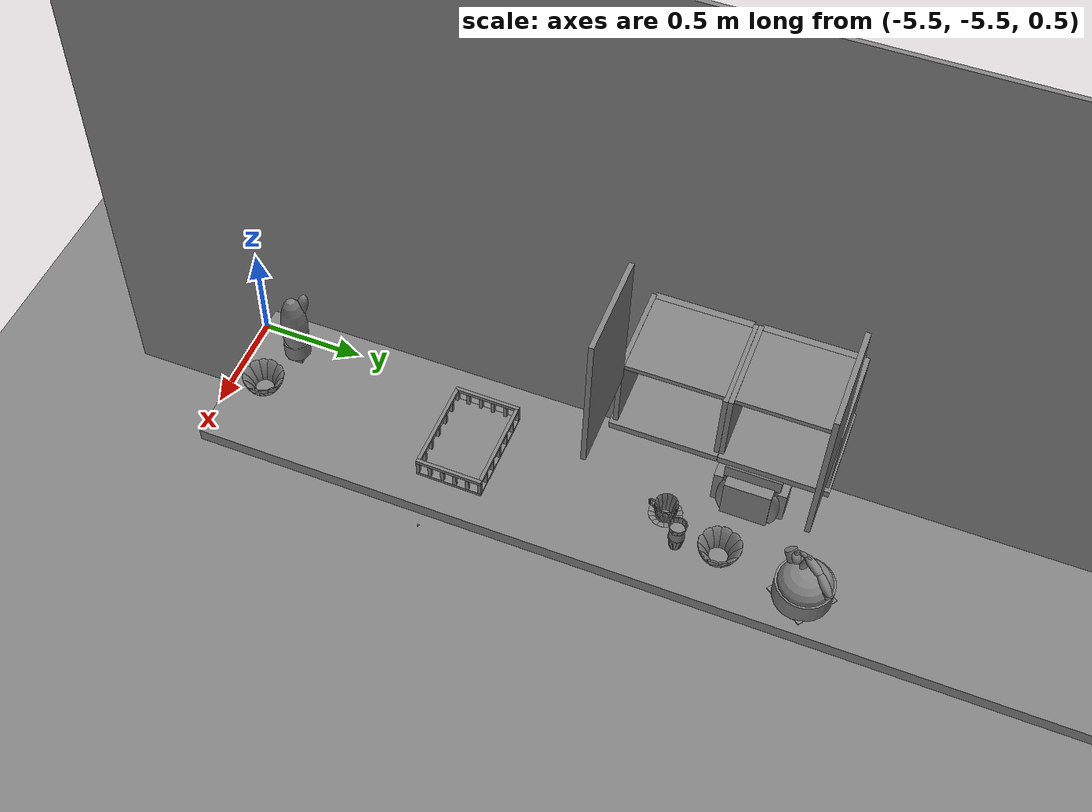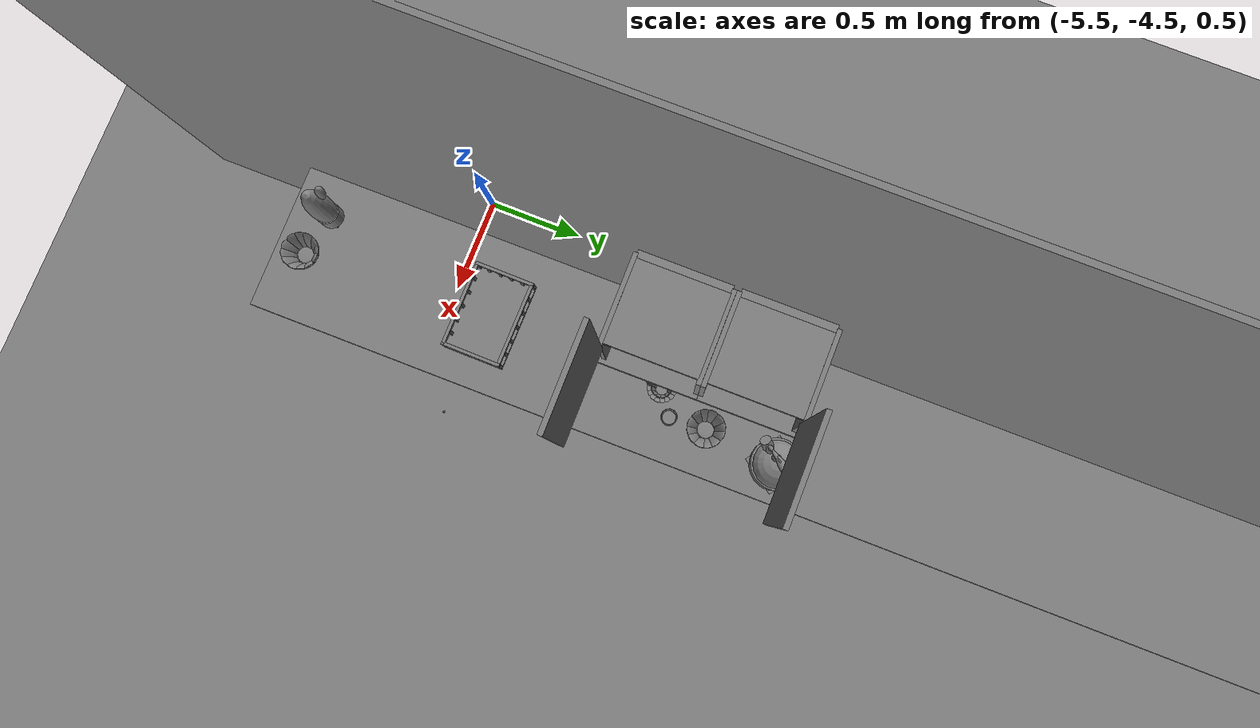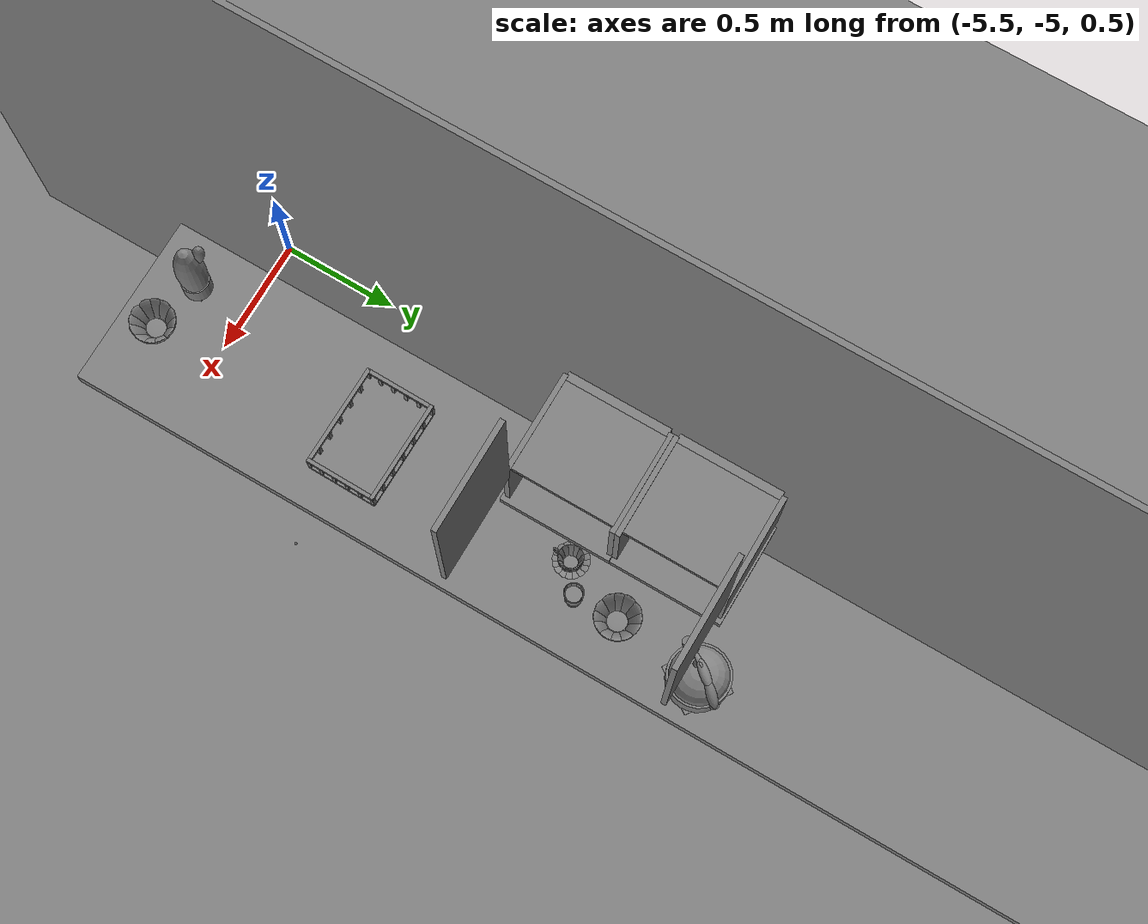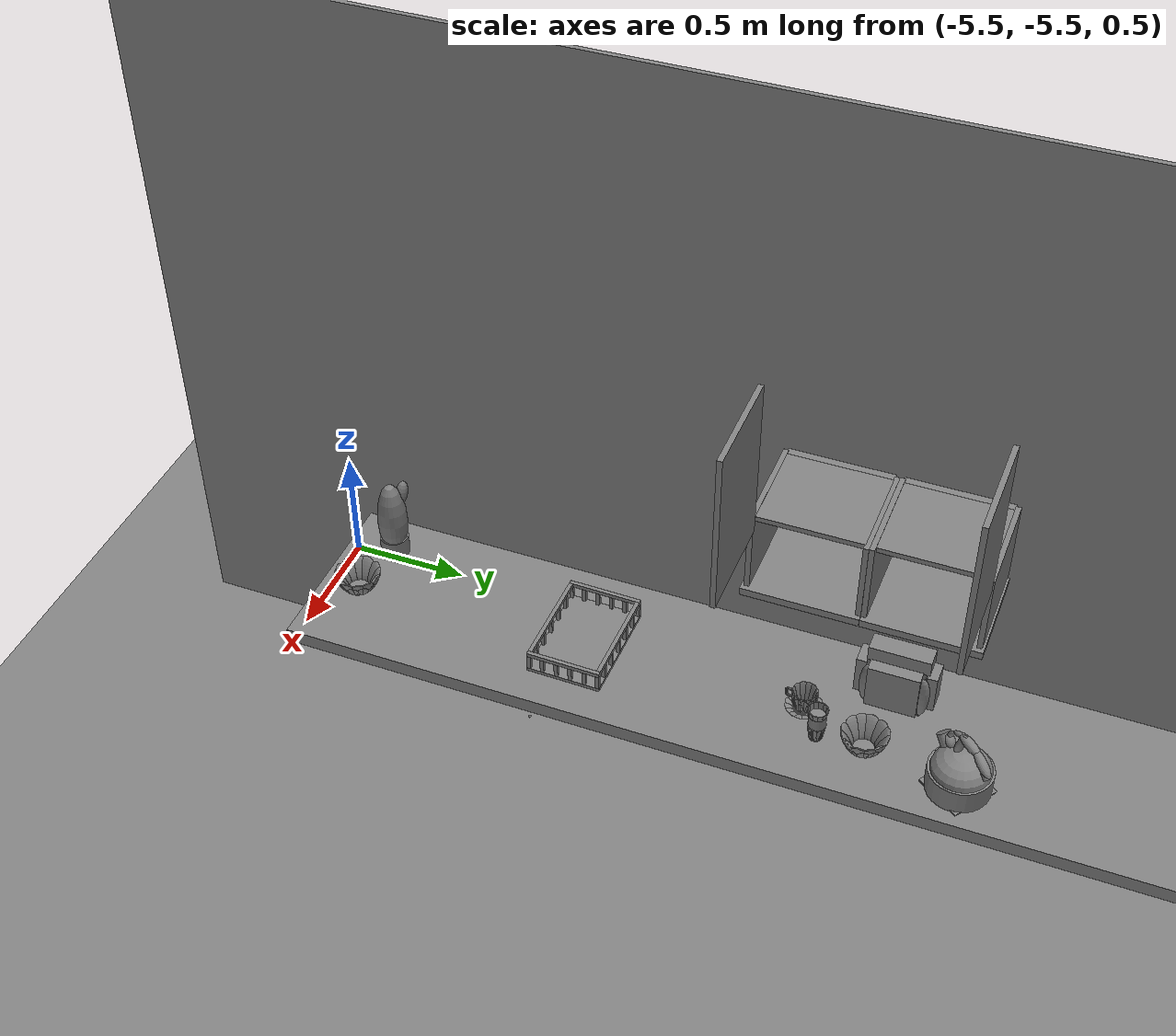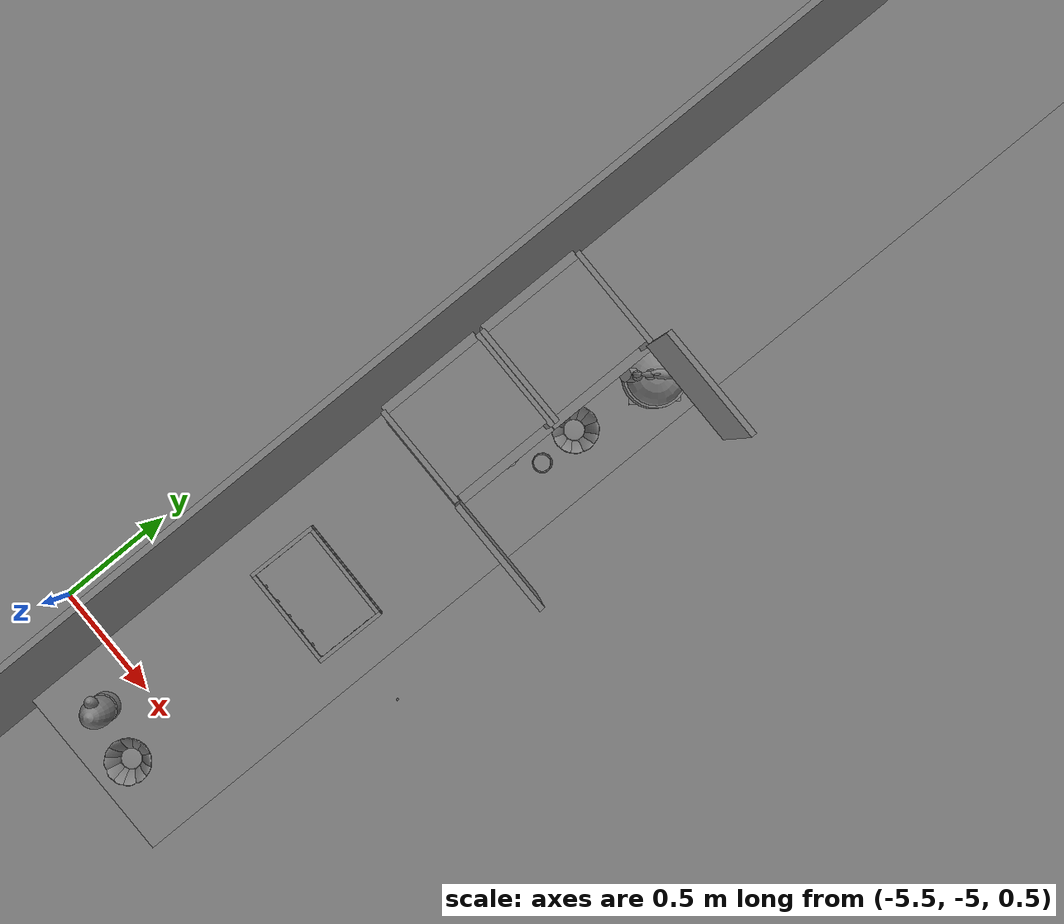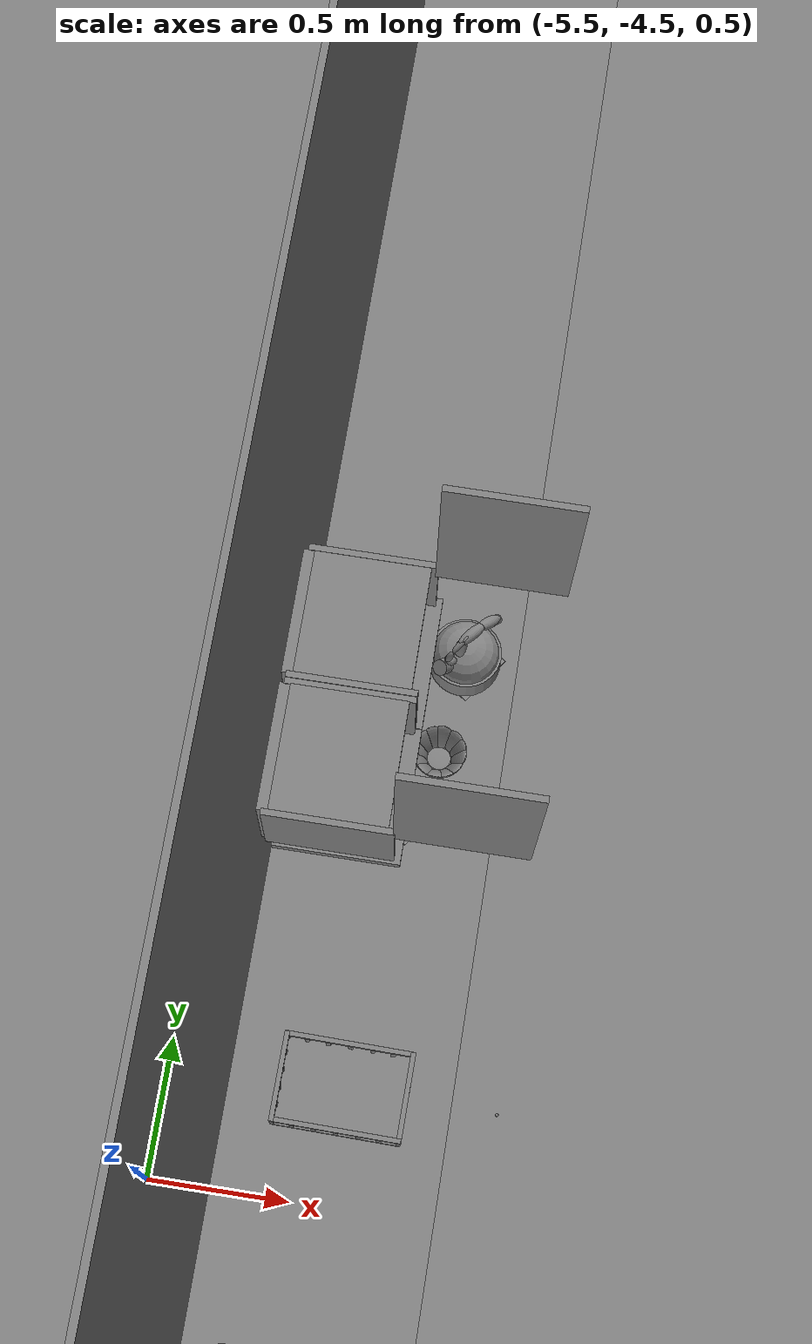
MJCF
<mujoco>
    <option gravity="0.000000000 0.000000000 -9.810000420" timestep="0.0049999999" integrator="implicitfast" density="9.8000002" viscosity="1.8000001e-05" noslip_iterations="10" iterations="100" sdf_iterations="50">
        <flag multiccd="disable"/>
    </option>
    <size memory="1000M"/>
    <compiler coordinate="local"/>
    <worldbody>
        <light cutoff="30" pos="0 1 1" dir="0 -1 -2"/>
        <light cutoff="30" pos="0 -1 1" dir="0 1 -2"/>
        <body pos="-5.046103477 -5.051773071 1.001502514" euler="0.000000000 0.000000000 0.000000000" name="Interactive Objcets_huapen">
            <geom contype="1" conaffinity="1" density="1000" type="ellipsoid" material="" rgba="0.500000000 0.500000000 0.500000000 1.000000000" solimp="0.899999976 0.949999988 0.001000000" friction="1.000000000 0.005000000 0.000100000" solref="0.020000000 1.000000000" margin="0" condim="3" group="0" pos="0.008062840 0.004346371 0.205056787" quat="1.000000000 0.000000000 0.000000000 0.000000000" size="0.059999999 0.059999999 0.180000007" name="Interactive Objcets_huapen_hua_D1C791A8_ED4C_4049_876B_F8B3CBD05289"/>
            <geom contype="1" conaffinity="1" density="1000" type="cylinder" material="" rgba="0.500000000 0.500000000 0.500000000 1.000000000" solimp="0.899999976 0.949999988 0.001000000" friction="1.000000000 0.005000000 0.000100000" solref="0.020000000 1.000000000" margin="0" condim="3" group="0" pos="0.008062840 0.003952026 0.080107450" quat="1.000000000 0.000000000 0.000000000 0.000000000" size="0.057999998 0.039999999 1.000000000" name="Interactive Objcets_huapen_hua_BD965553_92BF_494C_B701_EBC170F9B111"/>
            <geom contype="1" conaffinity="1" density="1000" type="box" material="" rgba="0.500000000 0.500000000 0.500000000 1.000000000" solimp="0.899999976 0.949999988 0.001000000" friction="1.000000000 0.005000000 0.000100000" solref="0.020000000 1.000000000" margin="0" condim="3" group="0" pos="0.008062840 0.003952503 0.020566106" quat="1.000000000 0.000000000 0.000000000 0.000000000" size="0.035000000 0.035000000 0.020000000" name="Interactive Objcets_huapen_hua_8EFEE669_8356_4E3C_8820_1010E56E6257"/>
            <geom contype="1" conaffinity="1" density="1000" type="ellipsoid" material="" rgba="0.500000000 0.500000000 0.500000000 1.000000000" solimp="0.899999976 0.949999988 0.001000000" friction="1.000000000 0.005000000 0.000100000" solref="0.020000000 1.000000000" margin="0" condim="3" group="0" pos="-0.029900074 0.033599377 0.321917295" quat="0.992658079 -0.083605267 -0.087364964 0.002748166" size="0.025000000 0.025000000 0.059999999" name="Interactive Objcets_huapen_hua_8A56F814_7B30_4B45_A069_0CCA52577752"/>
            <freejoint name="Interactive Objcets_huapen"/>
        </body>
        <body pos="-4.326462746 -3.713677645 1.808423638" euler="5.505054951 -47.163360596 -62.648868561" mocap="true" name="spotlight2_SpotLight"/>
        <body pos="1000.000000000 1000.000000000 1.000000000" euler="0.000000000 0.000000000 0.000000000" name="openloong_gripper_2f85_fix_base_usda_bow_yellow_kps">
            <geom contype="1" conaffinity="1" density="1000" type="ellipsoid" material="" rgba="0.500000000 0.500000000 0.500000000 1.000000000" solimp="0.899999976 0.949999988 0.001000000" friction="1.000000000 0.005000000 0.000100000" solref="0.020000000 1.000000000" margin="0" condim="3" group="0" pos="-0.052185059 0.040283203 0.044118762" quat="0.919264615 -0.076883033 -0.225593656 -0.313287765" size="0.010000000 0.039999999 0.052000001" name="openloong_gripper_2f85_fix_base_usda_geom_F15922C8_62F8_4DC7_A02C_ABF01A30C872"/>
            <geom contype="1" conaffinity="1" density="1000" type="ellipsoid" material="" rgba="0.500000000 0.500000000 0.500000000 1.000000000" solimp="0.899999976 0.949999988 0.001000000" friction="1.000000000 0.005000000 0.000100000" solref="0.020000000 1.000000000" margin="0" condim="3" group="0" pos="-0.000061035 0.065979004 0.044118762" quat="0.687598765 -0.168314874 -0.168741167 -0.685860336" size="0.010000000 0.039999999 0.052000001" name="openloong_gripper_2f85_fix_base_usda_geom_ED76D589_31C1_4007_AFB7_9D9A16190694"/>
            <geom contype="1" conaffinity="1" density="1000" type="box" material="" rgba="0.500000000 0.500000000 0.500000000 1.000000000" solimp="0.899999976 0.949999988 0.001000000" friction="1.000000000 0.005000000 0.000100000" solref="0.020000000 1.000000000" margin="0" condim="3" group="0" pos="0.000061035 0.000000000 -0.002001643" quat="1.000000000 0.000000000 0.000000000 0.000000000" size="0.029999999 0.029999999 0.002000000" name="openloong_gripper_2f85_fix_base_usda_geom_3E266D4B_7FD5_4217_AEEF_D8D498A128CB"/>
            <geom contype="1" conaffinity="1" density="1000" type="ellipsoid" material="" rgba="0.500000000 0.500000000 0.500000000 1.000000000" solimp="0.899999976 0.949999988 0.001000000" friction="1.000000000 0.005000000 0.000100000" solref="0.020000000 1.000000000" margin="0" condim="3" group="0" pos="0.029418945 -0.059082031 0.044118762" quat="0.825555861 0.125530601 0.202597082 -0.511521280" size="0.010000000 0.039999999 0.052000001" name="openloong_gripper_2f85_fix_base_usda_geom_EA8A78EC_CE11_4AB6_8777_27C9DEB5F1E4"/>
            <geom contype="1" conaffinity="1" density="1000" type="ellipsoid" material="" rgba="0.500000000 0.500000000 0.500000000 1.000000000" solimp="0.899999976 0.949999988 0.001000000" friction="1.000000000 0.005000000 0.000100000" solref="0.020000000 1.000000000" margin="0" condim="3" group="0" pos="0.000244141 -0.065979004 0.044118762" quat="0.687598765 0.168314651 0.168741375 -0.685860336" size="0.010000000 0.039999999 0.052000001" name="openloong_gripper_2f85_fix_base_usda_geom_B26D3E35_053A_4E0A_8A59_06E3786508FB"/>
            <geom contype="1" conaffinity="1" density="1000" type="ellipsoid" material="" rgba="0.500000000 0.500000000 0.500000000 1.000000000" solimp="0.899999976 0.949999988 0.001000000" friction="1.000000000 0.005000000 0.000100000" solref="0.020000000 1.000000000" margin="0" condim="3" group="0" pos="0.000061035 0.000000000 0.000446677" quat="1.000000000 0.000000000 0.000000000 0.000000000" size="0.039999999 0.039999999 0.002000000" name="openloong_gripper_2f85_fix_base_usda_geom_C10F0E11_8DD5_4924_AF72_B7C712B37A62"/>
            <geom contype="1" conaffinity="1" density="1000" type="ellipsoid" material="" rgba="0.500000000 0.500000000 0.500000000 1.000000000" solimp="0.899999976 0.949999988 0.001000000" friction="1.000000000 0.005000000 0.000100000" solref="0.020000000 1.000000000" margin="0" condim="3" group="0" pos="0.059082031 0.029541016 0.044118762" quat="0.223252773 -0.231952220 -0.054787423 -0.945174456" size="0.010000000 0.039999999 0.052000001" name="openloong_gripper_2f85_fix_base_usda_geom_677E02C4_1EED_4986_875B_FCB0A9F670B3"/>
            <geom contype="1" conaffinity="1" density="1000" type="ellipsoid" material="" rgba="0.500000000 0.500000000 0.500000000 1.000000000" solimp="0.899999976 0.949999988 0.001000000" friction="1.000000000 0.005000000 0.000100000" solref="0.020000000 1.000000000" margin="0" condim="3" group="0" pos="0.000061035 0.000000000 0.007335305" quat="1.000000000 0.000000000 0.000000000 0.000000000" size="0.039999999 0.039999999 0.002000000" name="openloong_gripper_2f85_fix_base_usda_geom_403DDA03_91BD_4681_9F17_BD8C2EE6DF3E"/>
            <geom contype="1" conaffinity="1" density="1000" type="ellipsoid" material="" rgba="0.500000000 0.500000000 0.500000000 1.000000000" solimp="0.899999976 0.949999988 0.001000000" friction="1.000000000 0.005000000 0.000100000" solref="0.020000000 1.000000000" margin="0" condim="3" group="0" pos="-0.029296875 0.059082031 0.044118762" quat="0.825555861 -0.125530809 -0.202596918 -0.511521280" size="0.010000000 0.039999999 0.052000001" name="openloong_gripper_2f85_fix_base_usda_geom_C8A403B9_EE24_4A66_BEA4_EE284AE722B6"/>
            <geom contype="1" conaffinity="1" density="1000" type="ellipsoid" material="" rgba="0.500000000 0.500000000 0.500000000 1.000000000" solimp="0.899999976 0.949999988 0.001000000" friction="1.000000000 0.005000000 0.000100000" solref="0.020000000 1.000000000" margin="0" condim="3" group="0" pos="0.040222168 0.052368164 0.044118762" quat="0.429593176 -0.213750049 -0.105424821 -0.871002972" size="0.010000000 0.039999999 0.052000001" name="openloong_gripper_2f85_fix_base_usda_geom_19E5A8A2_14A8_4D9A_9E45_CEBC075E7678"/>
            <geom contype="1" conaffinity="1" density="1000" type="ellipsoid" material="" rgba="0.500000000 0.500000000 0.500000000 1.000000000" solimp="0.899999976 0.949999988 0.001000000" friction="1.000000000 0.005000000 0.000100000" solref="0.020000000 1.000000000" margin="0" condim="3" group="0" pos="0.066040039 0.000000000 0.044118762" quat="0.971183062 -0.000000156 0.238334835 0.000000030" size="0.010000000 0.039999999 0.052000001" name="openloong_gripper_2f85_fix_base_usda_geom_231D3B83_099C_4DB2_9854_03B3F55F5EBB"/>
            <geom contype="1" conaffinity="1" density="1000" type="ellipsoid" material="" rgba="0.500000000 0.500000000 0.500000000 1.000000000" solimp="0.899999976 0.949999988 0.001000000" friction="1.000000000 0.005000000 0.000100000" solref="0.020000000 1.000000000" margin="0" condim="3" group="0" pos="0.052307129 -0.040283203 0.044118762" quat="0.919264674 0.076882750 0.225593731 -0.313287705" size="0.010000000 0.039999999 0.052000001" name="openloong_gripper_2f85_fix_base_usda_geom_9F325366_C612_4360_9799_9D390A0FDCE7"/>
            <geom contype="1" conaffinity="1" density="1000" type="ellipsoid" material="" rgba="0.500000000 0.500000000 0.500000000 1.000000000" solimp="0.899999976 0.949999988 0.001000000" friction="1.000000000 0.005000000 0.000100000" solref="0.020000000 1.000000000" margin="0" condim="3" group="0" pos="-0.065917969 0.000000000 0.044118762" quat="0.971183062 -0.000000142 -0.238334835 0.000000030" size="0.010000000 0.039999999 0.052000001" name="openloong_gripper_2f85_fix_base_usda_geom_4F7294D8_1CE4_4CCD_8F4C_BFE531B79D6A"/>
            <geom contype="1" conaffinity="1" density="1000" type="ellipsoid" material="" rgba="0.500000000 0.500000000 0.500000000 1.000000000" solimp="0.899999976 0.949999988 0.001000000" friction="1.000000000 0.005000000 0.000100000" solref="0.020000000 1.000000000" margin="0" condim="3" group="0" pos="-0.058898926 -0.029541016 0.044118762" quat="0.223252758 0.231952101 0.054787733 -0.945174575" size="0.010000000 0.039999999 0.052000001" name="openloong_gripper_2f85_fix_base_usda_geom_6B02DE08_4143_4D03_B782_5CBB1AC52705"/>
            <geom contype="1" conaffinity="1" density="1000" type="ellipsoid" material="" rgba="0.500000000 0.500000000 0.500000000 1.000000000" solimp="0.899999976 0.949999988 0.001000000" friction="1.000000000 0.005000000 0.000100000" solref="0.020000000 1.000000000" margin="0" condim="3" group="0" pos="-0.040100098 -0.052368164 0.044118762" quat="0.429593235 0.213749886 0.105425082 -0.871003032" size="0.010000000 0.039999999 0.052000001" name="openloong_gripper_2f85_fix_base_usda_geom_073183B1_8CE9_4E39_B58D_E5CD0D203E83"/>
            <freejoint name="openloong_gripper_2f85_fix_base_usda_bow_yellow_kps_joint"/>
            <site size="0.005000000 0.005000000 0.005000000" rgba="0.500000000 0.500000000 0.500000000 1.000000000" pos="0.000000000 0.000000000 0.000000000" quat="0.999961913 0.008726534 0.000000000 0.000000000" group="0" type="sphere" name="openloong_gripper_2f85_fix_base_usda_bow_yellow_kps"/>
        </body>
        <body pos="-4.026199818 -4.326996803 1.721047044" euler="144.800003052 -66.558494568 109.250900269" mocap="true" name="spotlight6_SpotLight"/>
        <body pos="1000.000000000 1000.000000000 1.000000000" euler="0.000000000 0.000000000 0.000000000" name="openloong_gripper_2f85_fix_base_usda_salt">
            <geom contype="1" conaffinity="1" density="1000" type="box" material="" rgba="0.500000000 0.500000000 0.500000000 1.000000000" solimp="0.899999976 0.949999988 0.001000000" friction="1.000000000 0.005000000 0.000100000" solref="0.020000000 1.000000000" margin="0" condim="3" group="0" pos="0.000305176 0.000000000 0.084862232" quat="1.000000000 0.000000000 0.000000000 0.000000000" size="0.048999999 0.018999999 0.005000000" name="openloong_gripper_2f85_fix_base_usda_geom_74D0AD52_8028_4553_8A24_C56F2D213516"/>
            <geom contype="1" conaffinity="1" density="1000" type="box" material="" rgba="0.500000000 0.500000000 0.500000000 1.000000000" solimp="0.899999976 0.949999988 0.001000000" friction="1.000000000 0.005000000 0.000100000" solref="0.020000000 1.000000000" margin="0" condim="3" group="0" pos="0.000305176 0.000000000 0.104564309" quat="1.000000000 0.000000000 0.000000000 0.000000000" size="0.052000001 0.014000000 0.005000000" name="openloong_gripper_2f85_fix_base_usda_geom_B3D1FD03_EF7B_452E_B33E_DEFD35EF97D7"/>
            <geom contype="1" conaffinity="1" density="1000" type="box" material="" rgba="0.500000000 0.500000000 0.500000000 1.000000000" solimp="0.899999976 0.949999988 0.001000000" friction="1.000000000 0.005000000 0.000100000" solref="0.020000000 1.000000000" margin="0" condim="3" group="0" pos="0.000305176 0.000000000 0.114487171" quat="1.000000000 0.000000000 0.000000000 0.000000000" size="0.054000001 0.011500000 0.005000000" name="openloong_gripper_2f85_fix_base_usda_geom_BCCB61C7_7B8A_4118_96DA_D3A5C7269B8F"/>
            <geom contype="1" conaffinity="1" density="1000" type="box" material="" rgba="0.500000000 0.500000000 0.500000000 1.000000000" solimp="0.899999976 0.949999988 0.001000000" friction="1.000000000 0.005000000 0.000100000" solref="0.020000000 1.000000000" margin="0" condim="3" group="0" pos="0.000305176 0.000000000 0.075103164" quat="1.000000000 0.000000000 0.000000000 0.000000000" size="0.048000000 0.020000000 0.005000000" name="openloong_gripper_2f85_fix_base_usda_geom_FC41992D_3A8C_4F1D_9A41_F3A946CBCC91"/>
            <geom contype="1" conaffinity="1" density="1000" type="box" material="" rgba="0.500000000 0.500000000 0.500000000 1.000000000" solimp="0.899999976 0.949999988 0.001000000" friction="1.000000000 0.005000000 0.000100000" solref="0.020000000 1.000000000" margin="0" condim="3" group="0" pos="0.000305176 0.000000000 0.134892464" quat="1.000000000 0.000000000 0.000000000 0.000000000" size="0.057000000 0.007000000 0.005000000" name="openloong_gripper_2f85_fix_base_usda_geom_B7B5C5B5_3F11_4CB6_AC4A_19E66242B984"/>
            <geom contype="1" conaffinity="1" density="1000" type="box" material="" rgba="0.500000000 0.500000000 0.500000000 1.000000000" solimp="0.899999976 0.949999988 0.001000000" friction="1.000000000 0.005000000 0.000100000" solref="0.020000000 1.000000000" margin="0" condim="3" group="0" pos="0.000305176 0.000000000 0.094920278" quat="1.000000000 0.000000000 0.000000000 0.000000000" size="0.050000001 0.017000001 0.005000000" name="openloong_gripper_2f85_fix_base_usda_geom_3E540DC6_634D_4176_9859_65451189DEA2"/>
            <geom contype="1" conaffinity="1" density="1000" type="box" material="" rgba="0.500000000 0.500000000 0.500000000 1.000000000" solimp="0.899999976 0.949999988 0.001000000" friction="1.000000000 0.005000000 0.000100000" solref="0.020000000 1.000000000" margin="0" condim="3" group="0" pos="0.000305176 0.000000000 0.065204859" quat="1.000000000 0.000000000 0.000000000 0.000000000" size="0.045000002 0.021000000 0.005000000" name="openloong_gripper_2f85_fix_base_usda_geom_A0F05884_50F6_4FEB_A35E_3EC5FCB3E381"/>
            <geom contype="1" conaffinity="1" density="1000" type="box" material="" rgba="0.500000000 0.500000000 0.500000000 1.000000000" solimp="0.899999976 0.949999988 0.001000000" friction="1.000000000 0.005000000 0.000100000" solref="0.020000000 1.000000000" margin="0" condim="3" group="0" pos="0.000305176 0.000000000 0.144135714" quat="1.000000000 0.000000000 0.000000000 0.000000000" size="0.059000000 0.005000000 0.004000000" name="openloong_gripper_2f85_fix_base_usda_geom_61A2E961_42E0_4686_922B_C8D1C61C12F3"/>
            <geom contype="1" conaffinity="1" density="1000" type="box" material="" rgba="0.500000000 0.500000000 0.500000000 1.000000000" solimp="0.899999976 0.949999988 0.001000000" friction="1.000000000 0.005000000 0.000100000" solref="0.020000000 1.000000000" margin="0" condim="3" group="0" pos="0.000000000 0.000000000 0.031593561" quat="1.000000000 0.000000000 0.000000000 0.000000000" size="0.041999999 0.024000000 0.029999999" name="openloong_gripper_2f85_fix_base_usda_geom_2A76A1CA_99FC_410F_AB01_12580466FFB3"/>
            <geom contype="1" conaffinity="1" density="1000" type="box" material="" rgba="0.500000000 0.500000000 0.500000000 1.000000000" solimp="0.899999976 0.949999988 0.001000000" friction="1.000000000 0.005000000 0.000100000" solref="0.020000000 1.000000000" margin="0" condim="3" group="0" pos="0.000305176 0.000000000 0.124608755" quat="1.000000000 0.000000000 0.000000000 0.000000000" size="0.055000000 0.008000000 0.005000000" name="openloong_gripper_2f85_fix_base_usda_geom_10CE8CC9_C022_4D63_AB00_C676D4A31561"/>
            <freejoint name="openloong_gripper_2f85_fix_base_usda_salt_joint"/>
            <site size="0.005000000 0.005000000 0.005000000" rgba="0.500000000 0.500000000 0.500000000 1.000000000" pos="0.000000000 0.000000000 0.000000000" quat="1.000000000 0.000000000 0.000000000 0.000000000" group="0" type="sphere" name="openloong_gripper_2f85_fix_base_usda_saltsite"/>
        </body>
        <body pos="-4.289083004 -4.496354103 1.830863357" euler="-170.092102051 39.895824432 160.975967407" mocap="true" name="spotlight1_SpotLight"/>
        <body pos="1000.000000000 1000.000000000 1.000000000" euler="0.000000000 0.000000000 0.000000000" name="openloong_gripper_2f85_fix_base_usda_jar_01">
            <geom contype="1" conaffinity="1" density="1000" type="box" material="" rgba="0.500000000 0.500000000 0.500000000 1.000000000" solimp="0.899999976 0.949999988 0.001000000" friction="1.000000000 0.005000000 0.000100000" solref="0.020000000 1.000000000" margin="0" condim="3" group="0" pos="0.000000000 0.000000000 0.006158113" quat="1.000000000 0.000000000 0.000000000 0.000000000" size="0.020000000 0.020000000 0.005000000" name="openloong_gripper_2f85_fix_base_usda_geom_4E7821B1_6EFC_48EF_8A1A_A27D9B37648C"/>
            <geom contype="1" conaffinity="1" density="1000" type="cylinder" material="" rgba="0.500000000 0.500000000 0.500000000 1.000000000" solimp="0.899999976 0.949999988 0.001000000" friction="1.000000000 0.005000000 0.000100000" solref="0.020000000 1.000000000" margin="0" condim="3" group="0" pos="0.000000000 0.000000000 0.062744498" quat="1.000000000 0.000000000 0.000000000 0.000000000" size="0.041000001 0.052999999 1.000000000" name="openloong_gripper_2f85_fix_base_usda_geom_A9B94D14_4B29_4FF7_82BC_D605C2609427"/>
            <geom contype="1" conaffinity="1" density="1000" type="ellipsoid" material="" rgba="0.500000000 0.500000000 0.500000000 1.000000000" solimp="0.899999976 0.949999988 0.001000000" friction="1.000000000 0.005000000 0.000100000" solref="0.020000000 1.000000000" margin="0" condim="3" group="0" pos="0.000000000 0.000000000 0.122252703" quat="1.000000000 0.000000000 0.000000000 0.000000000" size="0.035999998 0.035999998 0.010000000" name="openloong_gripper_2f85_fix_base_usda_geom_C02BAC86_4AC3_4080_B931_7EDF7077B627"/>
            <geom contype="1" conaffinity="1" density="1000" type="cylinder" material="" rgba="0.500000000 0.500000000 0.500000000 1.000000000" solimp="0.899999976 0.949999988 0.001000000" friction="1.000000000 0.005000000 0.000100000" solref="0.020000000 1.000000000" margin="0" condim="3" group="0" pos="0.000000000 0.000000000 0.015747190" quat="1.000000000 0.000000000 0.000000000 0.000000000" size="0.035000000 0.010000000 1.000000000" name="openloong_gripper_2f85_fix_base_usda_geom_977AFE12_B031_45E9_A0B4_BD860F4B8734"/>
            <geom contype="1" conaffinity="1" density="1000" type="ellipsoid" material="" rgba="0.500000000 0.500000000 0.500000000 1.000000000" solimp="0.899999976 0.949999988 0.001000000" friction="1.000000000 0.005000000 0.000100000" solref="0.020000000 1.000000000" margin="0" condim="3" group="0" pos="0.000000000 0.000000000 0.115815401" quat="1.000000000 0.000000000 0.000000000 0.000000000" size="0.039999999 0.039999999 0.010000000" name="openloong_gripper_2f85_fix_base_usda_geom_1EF1FC16_7257_4AC5_83A5_7E3CEE4541B3"/>
            <geom contype="1" conaffinity="1" density="1000" type="cylinder" material="" rgba="0.500000000 0.500000000 0.500000000 1.000000000" solimp="0.899999976 0.949999988 0.001000000" friction="1.000000000 0.005000000 0.000100000" solref="0.020000000 1.000000000" margin="0" condim="3" group="0" pos="0.000000000 0.000000000 0.133183479" quat="1.000000000 0.000000000 0.000000000 0.000000000" size="0.037999999 0.006500000 1.000000000" name="openloong_gripper_2f85_fix_base_usda_geom_2BF1043E_5936_44D9_92E6_08868D9B5E4C"/>
            <freejoint name="openloong_gripper_2f85_fix_base_usda_jar_01_joint"/>
            <site size="0.005000000 0.005000000 0.005000000" rgba="0.500000000 0.500000000 0.500000000 1.000000000" pos="0.000000000 0.000000000 0.000000000" quat="1.000000000 0.000000000 0.000000000 0.000000000" group="0" type="sphere" name="openloong_gripper_2f85_fix_base_usda_jar_01site"/>
        </body>
        <body pos="1000.000000000 1000.000000000 1.000000000" euler="0.000000000 0.000000000 0.000000000" name="openloong_gripper_2f85_fix_base_usda_coffeecup_white_kps">
            <geom contype="1" conaffinity="1" density="1000" type="capsule" material="" rgba="0.500000000 0.500000000 0.500000000 1.000000000" solimp="0.899999976 0.949999988 0.001000000" friction="1.000000000 0.005000000 0.000100000" solref="0.020000000 1.000000000" margin="0" condim="3" group="0" pos="-0.000854492 -0.065795898 0.050029993" quat="0.343559504 -0.613204718 0.626912475 0.336047262" size="0.004000000 0.005000000 1.000000000" name="openloong_gripper_2f85_fix_base_usda_geom_44CC0882_98D4_4852_ACBA_D0227CF5929A"/>
            <geom contype="1" conaffinity="1" density="1000" type="ellipsoid" material="" rgba="0.500000000 0.500000000 0.500000000 1.000000000" solimp="0.899999976 0.949999988 0.001000000" friction="1.000000000 0.005000000 0.000100000" solref="0.020000000 1.000000000" margin="0" condim="3" group="0" pos="-0.000793457 -0.038452148 0.048040152" quat="0.711656272 0.066323131 -0.067805752 0.696095467" size="0.005000000 0.029999999 0.048999999" name="openloong_gripper_2f85_fix_base_usda_geom_C5140048_CB9C_4BA0_8D79_2BB90260E4AD"/>
            <geom contype="1" conaffinity="1" density="1000" type="ellipsoid" material="" rgba="0.500000000 0.500000000 0.500000000 1.000000000" solimp="0.899999976 0.949999988 0.001000000" friction="1.000000000 0.005000000 0.000100000" solref="0.020000000 1.000000000" margin="0" condim="3" group="0" pos="0.037719727 -0.001892090 0.048040152" quat="0.995387912 0.001371633 0.094835162 -0.014391154" size="0.005000000 0.029999999 0.048999999" name="openloong_gripper_2f85_fix_base_usda_geom_48EB6ABA_6875_4156_9ED0_339EFD7911FB"/>
            <geom contype="1" conaffinity="1" density="1000" type="ellipsoid" material="" rgba="0.500000000 0.500000000 0.500000000 1.000000000" solimp="0.899999976 0.949999988 0.001000000" friction="1.000000000 0.005000000 0.000100000" solref="0.020000000 1.000000000" margin="0" condim="3" group="0" pos="0.033996582 0.015502930 0.048040152" quat="0.970659733 -0.021051638 0.092478797 0.220962167" size="0.005000000 0.029999999 0.048999999" name="openloong_gripper_2f85_fix_base_usda_geom_8C49F842_BE3D_4075_B70D_0CF1F90560F9"/>
            <geom contype="1" conaffinity="1" density="1000" type="box" material="" rgba="0.500000000 0.500000000 0.500000000 1.000000000" solimp="0.899999976 0.949999988 0.001000000" friction="1.000000000 0.005000000 0.000100000" solref="0.020000000 1.000000000" margin="0" condim="3" group="0" pos="0.000793457 -0.000183105 0.000156164" quat="0.714879215 0.000000000 0.000000000 0.699247897" size="0.020000000 0.020000000 0.002000000" name="openloong_gripper_2f85_fix_base_usda_geom_80CFB0B8_332E_457D_B434_DEDAF1E97924"/>
            <geom contype="1" conaffinity="1" density="1000" type="ellipsoid" material="" rgba="0.500000000 0.500000000 0.500000000 1.000000000" solimp="0.899999976 0.949999988 0.001000000" friction="1.000000000 0.005000000 0.000100000" solref="0.020000000 1.000000000" margin="0" condim="3" group="0" pos="-0.019409180 -0.033081055 0.048040152" quat="0.866879702 0.046630561 -0.082595348 0.489411235" size="0.005000000 0.029999999 0.048999999" name="openloong_gripper_2f85_fix_base_usda_geom_D61BDE91_534C_4C9B_BC14_E981D6FBC5C6"/>
            <geom contype="1" conaffinity="1" density="1000" type="ellipsoid" material="" rgba="0.500000000 0.500000000 0.500000000 1.000000000" solimp="0.899999976 0.949999988 0.001000000" friction="1.000000000 0.005000000 0.000100000" solref="0.020000000 1.000000000" margin="0" condim="3" group="0" pos="-0.016052246 0.033264160 0.048040152" quat="0.840792537 -0.050782297 -0.080109790 -0.532983541" size="0.005000000 0.029999999 0.048999999" name="openloong_gripper_2f85_fix_base_usda_geom_6F2472A6_B633_4FE5_9B3C_6604927E58D2"/>
            <geom contype="1" conaffinity="1" density="1000" type="capsule" material="" rgba="0.500000000 0.500000000 0.500000000 1.000000000" solimp="0.899999976 0.949999988 0.001000000" friction="1.000000000 0.005000000 0.000100000" solref="0.020000000 1.000000000" margin="0" condim="3" group="0" pos="-0.000549316 -0.053527832 0.046825886" quat="0.505496025 -0.494442940 0.505495846 0.494442940" size="0.004000000 0.005000000 1.000000000" name="openloong_gripper_2f85_fix_base_usda_geom_6FFE4365_E64F_48CD_AD6D_B3CBB5767455"/>
            <geom contype="1" conaffinity="1" density="1000" type="ellipsoid" material="" rgba="0.500000000 0.500000000 0.500000000 1.000000000" solimp="0.899999976 0.949999988 0.001000000" friction="1.000000000 0.005000000 0.000100000" solref="0.020000000 1.000000000" margin="0" condim="3" group="0" pos="-0.032104492 0.018920898 0.048040152" quat="0.958129764 -0.025742561 -0.091288343 -0.270168930" size="0.005000000 0.029999999 0.048999999" name="openloong_gripper_2f85_fix_base_usda_geom_EBB0F9A5_3E05_4D9E_9303_5C0AFC6E3DD2"/>
            <geom contype="1" conaffinity="1" density="1000" type="ellipsoid" material="" rgba="0.500000000 0.500000000 0.500000000 1.000000000" solimp="0.899999976 0.949999988 0.001000000" friction="1.000000000 0.005000000 0.000100000" solref="0.020000000 1.000000000" margin="0" condim="3" group="0" pos="-0.037597656 0.000305176 0.048040152" quat="0.995387554 -0.001371440 -0.094839431 -0.014389008" size="0.005000000 0.029999999 0.048999999" name="openloong_gripper_2f85_fix_base_usda_geom_C546AB39_1AC0_4216_97F8_734665A9D881"/>
            <geom contype="1" conaffinity="1" density="1000" type="capsule" material="" rgba="0.500000000 0.500000000 0.500000000 1.000000000" solimp="0.899999976 0.949999988 0.001000000" friction="1.000000000 0.005000000 0.000100000" solref="0.020000000 1.000000000" margin="0" condim="3" group="0" pos="-0.000366211 -0.043762207 0.044118762" quat="0.260488123 -0.651174724 0.665731549 0.254792154" size="0.004000000 0.003000000 1.000000000" name="openloong_gripper_2f85_fix_base_usda_geom_CE6F7E26_D332_4C9F_B523_307D2BC7139D"/>
            <geom contype="1" conaffinity="1" density="1000" type="capsule" material="" rgba="0.500000000 0.500000000 0.500000000 1.000000000" solimp="0.899999976 0.949999988 0.001000000" friction="1.000000000 0.005000000 0.000100000" solref="0.020000000 1.000000000" margin="0" condim="3" group="0" pos="-0.000915527 -0.068542480 0.082936406" quat="0.624995589 -0.339446366 0.347034454 0.611329615" size="0.004000000 0.004000000 1.000000000" name="openloong_gripper_2f85_fix_base_usda_geom_04BFEDBB_94C1_4971_ACCB_41B66007FCB9"/>
            <geom contype="1" conaffinity="1" density="1000" type="ellipsoid" material="" rgba="0.500000000 0.500000000 0.500000000 1.000000000" solimp="0.899999976 0.949999988 0.001000000" friction="1.000000000 0.005000000 0.000100000" solref="0.020000000 1.000000000" margin="0" condim="3" group="0" pos="0.016113281 -0.034851074 0.048040152" quat="0.840793252 0.050779939 0.080106191 -0.532983422" size="0.005000000 0.029999999 0.048999999" name="openloong_gripper_2f85_fix_base_usda_geom_D1083B8D_9F95_463C_857A_700D66C3F2FC"/>
            <geom contype="1" conaffinity="1" density="1000" type="ellipsoid" material="" rgba="0.500000000 0.500000000 0.500000000 1.000000000" solimp="0.899999976 0.949999988 0.001000000" friction="1.000000000 0.005000000 0.000100000" solref="0.020000000 1.000000000" margin="0" condim="3" group="0" pos="0.000854492 0.036865234 0.048040152" quat="0.711656570 -0.066320375 0.067802906 0.696095705" size="0.005000000 0.029999999 0.048999999" name="openloong_gripper_2f85_fix_base_usda_geom_FAE2AE12_3DB0_4E6A_8B4B_0299D58E0DBB"/>
            <geom contype="1" conaffinity="1" density="1000" type="ellipsoid" material="" rgba="0.500000000 0.500000000 0.500000000 1.000000000" solimp="0.899999976 0.949999988 0.001000000" friction="1.000000000 0.005000000 0.000100000" solref="0.020000000 1.000000000" margin="0" condim="3" group="0" pos="-0.033935547 -0.017089844 0.048040152" quat="0.970659137 0.021052625 -0.092483103 0.220962465" size="0.005000000 0.029999999 0.048999999" name="openloong_gripper_2f85_fix_base_usda_geom_E2FAE247_F407_453F_A254_5E09131A7A5E"/>
            <geom contype="1" conaffinity="1" density="1000" type="ellipsoid" material="" rgba="0.500000000 0.500000000 0.500000000 1.000000000" solimp="0.899999976 0.949999988 0.001000000" friction="1.000000000 0.005000000 0.000100000" solref="0.020000000 1.000000000" margin="0" condim="3" group="0" pos="0.019531250 0.031494141 0.048040152" quat="0.866880119 -0.046628602 0.082591817 0.489411235" size="0.005000000 0.029999999 0.048999999" name="openloong_gripper_2f85_fix_base_usda_geom_72BADAE6_6B5F_4273_9CF9_4D9011546425"/>
            <geom contype="1" conaffinity="1" density="1000" type="ellipsoid" material="" rgba="0.500000000 0.500000000 0.500000000 1.000000000" solimp="0.899999976 0.949999988 0.001000000" friction="1.000000000 0.005000000 0.000100000" solref="0.020000000 1.000000000" margin="0" condim="3" group="0" pos="0.032165527 -0.020507812 0.048040152" quat="0.958128154 0.025740955 0.091285400 -0.270175666" size="0.005000000 0.029999999 0.048999999" name="openloong_gripper_2f85_fix_base_usda_geom_3E02B55D_0CC7_41FA_8A34_84B32231A207"/>
            <geom contype="1" conaffinity="1" density="1000" type="capsule" material="" rgba="0.500000000 0.500000000 0.500000000 1.000000000" solimp="0.899999976 0.949999988 0.001000000" friction="1.000000000 0.005000000 0.000100000" solref="0.020000000 1.000000000" margin="0" condim="3" group="0" pos="-0.000610352 -0.056823730 0.083572865" quat="0.452654332 -0.541215360 0.553313971 0.442756712" size="0.004000000 0.009000000 1.000000000" name="openloong_gripper_2f85_fix_base_usda_geom_27B00D94_7110_4D19_BA31_5FC47DE3435E"/>
            <geom contype="1" conaffinity="1" density="1000" type="ellipsoid" material="" rgba="0.500000000 0.500000000 0.500000000 1.000000000" solimp="0.899999976 0.949999988 0.001000000" friction="1.000000000 0.005000000 0.000100000" solref="0.020000000 1.000000000" margin="0" condim="3" group="0" pos="0.000061035 -0.000183105 0.001848221" quat="0.714879215 0.000000000 0.000000000 0.699247897" size="0.029999999 0.029999999 0.001000000" name="openloong_gripper_2f85_fix_base_usda_geom_20C76D84_409A_47B1_80CA_0F8301FAE87D"/>
            <geom contype="1" conaffinity="1" density="1000" type="capsule" material="" rgba="0.500000000 0.500000000 0.500000000 1.000000000" solimp="0.899999976 0.949999988 0.001000000" friction="1.000000000 0.005000000 0.000100000" solref="0.020000000 1.000000000" margin="0" condim="3" group="0" pos="-0.000976562 -0.071838379 0.066101432" quat="0.031849027 -0.698553741 0.714169443 0.031152546" size="0.004000000 0.012000000 1.000000000" name="openloong_gripper_2f85_fix_base_usda_geom_77D7487D_DBA7_4098_BFD9_BD2EF6DD7202"/>
            <freejoint name="openloong_gripper_2f85_fix_base_usda_coffeecup_white_kps_joint"/>
            <site size="0.005000000 0.005000000 0.005000000" rgba="0.500000000 0.500000000 0.500000000 1.000000000" pos="0.000000000 0.000000000 0.000000000" quat="0.999961913 0.008726534 0.000000000 0.000000000" group="0" type="sphere" name="openloong_gripper_2f85_fix_base_usda_coffeecup_white_kps"/>
        </body>
        <body pos="1000.000000000 1000.000000000 1.000000000" euler="0.000000000 0.000000000 0.000000000" name="openloong_gripper_2f85_fix_base_usda_bottle_red">
            <geom contype="1" conaffinity="1" density="1000" type="ellipsoid" material="" rgba="0.500000000 0.500000000 0.500000000 1.000000000" solimp="0.899999976 0.949999988 0.001000000" friction="1.000000000 0.005000000 0.000100000" solref="0.020000000 1.000000000" margin="0" condim="3" group="0" pos="0.000000000 0.000000000 0.144284487" quat="1.000000000 0.000000000 0.000000000 0.000000000" size="0.021000000 0.021000000 0.079999998" name="openloong_gripper_2f85_fix_base_usda_geom_F22FAA6C_41A8_4C83_AFD3_C248AD5D146C"/>
            <geom contype="1" conaffinity="1" density="1000" type="cylinder" material="" rgba="0.500000000 0.500000000 0.500000000 1.000000000" solimp="0.899999976 0.949999988 0.001000000" friction="1.000000000 0.005000000 0.000100000" solref="0.020000000 1.000000000" margin="0" condim="3" group="0" pos="0.000000000 0.000000000 0.220618963" quat="1.000000000 0.000000000 0.000000000 0.000000000" size="0.016000001 0.010000000 1.000000000" name="openloong_gripper_2f85_fix_base_usda_geom_80D24EFA_6647_46B3_9F6F_2D2EC533AE09"/>
            <geom contype="1" conaffinity="1" density="1000" type="ellipsoid" material="" rgba="0.500000000 0.500000000 0.500000000 1.000000000" solimp="0.899999976 0.949999988 0.001000000" friction="1.000000000 0.005000000 0.000100000" solref="0.020000000 1.000000000" margin="0" condim="3" group="0" pos="0.000000000 0.000000000 0.118945479" quat="1.000000000 0.000000000 0.000000000 0.000000000" size="0.030999999 0.030999999 0.029999999" name="openloong_gripper_2f85_fix_base_usda_geom_9188B09E_8D1A_43F5_AD36_BFC38914BEEA"/>
            <geom contype="1" conaffinity="1" density="1000" type="box" material="" rgba="0.500000000 0.500000000 0.500000000 1.000000000" solimp="0.899999976 0.949999988 0.001000000" friction="1.000000000 0.005000000 0.000100000" solref="0.020000000 1.000000000" margin="0" condim="3" group="0" pos="0.000000000 0.000000000 0.002189159" quat="1.000000000 0.000000000 0.000000000 0.000000000" size="0.020000000 0.020000000 0.003000000" name="openloong_gripper_2f85_fix_base_usda_geom_F5F6BD98_FCA3_4EF9_AA0A_C5FB8464B515"/>
            <geom contype="1" conaffinity="1" density="1000" type="cylinder" material="" rgba="0.500000000 0.500000000 0.500000000 1.000000000" solimp="0.899999976 0.949999988 0.001000000" friction="1.000000000 0.005000000 0.000100000" solref="0.020000000 1.000000000" margin="0" condim="3" group="0" pos="0.000000000 -0.000366211 0.060884237" quat="1.000000000 0.000000000 0.000000000 0.000000000" size="0.030999999 0.057999998 1.000000000" name="openloong_gripper_2f85_fix_base_usda_geom_4A35E9C3_566A_4665_8881_820CDC55D48C"/>
            <freejoint name="openloong_gripper_2f85_fix_base_usda_bottle_red_joint"/>
            <site size="0.005000000 0.005000000 0.005000000" rgba="0.500000000 0.500000000 0.500000000 1.000000000" pos="0.000000000 0.000000000 0.000000000" quat="0.999961913 0.008726535 0.000000000 0.000000000" group="0" type="sphere" name="openloong_gripper_2f85_fix_base_usda_bottle_redsite"/>
        </body>
        <body pos="0.000000000 0.000000000 0.000000000" euler="0.000000000 0.000000000 0.000000000" name="Static Objcets_Static Objcets">
            <geom contype="1" conaffinity="1" density="1000" type="box" material="" rgba="0.500000000 0.500000000 0.500000000 1.000000000" solimp="0.899999976 0.949999988 0.001000000" friction="1.000000000 0.005000000 0.000100000" solref="0.020000000 1.000000000" margin="0" condim="3" group="0" pos="-4.999745846 -3.497932911 1.764780521" quat="0.707107067 0.707106471 0.000000000 0.000000000" size="0.200000003 0.159999996 0.010000000" name="Static Objcets_geom_1746A900_92DA_4AAE_B617_600C4732CE77"/>
            <geom contype="1" conaffinity="1" density="1000" type="box" material="" rgba="0.500000000 0.500000000 0.500000000 1.000000000" solimp="0.899999976 0.949999988 0.001000000" friction="1.000000000 0.005000000 0.000100000" solref="0.020000000 1.000000000" margin="0" condim="3" group="0" pos="-4.979488373 -3.297635794 1.591412544" quat="0.707106829 0.707106709 0.000000000 0.000000000" size="0.200000003 0.015000000 0.219999999" name="Static Objcets_geom_64EED0E2_ACDD_4ED2_A80E_96147A493052"/>
            <geom contype="1" conaffinity="1" density="1000" type="box" material="" rgba="0.500000000 0.500000000 0.500000000 1.000000000" solimp="0.899999976 0.949999988 0.001000000" friction="1.000000000 0.005000000 0.000100000" solref="0.020000000 1.000000000" margin="0" condim="3" group="0" pos="-4.999745846 -3.087441683 1.763863802" quat="0.707107067 0.707106471 0.000000000 0.000000000" size="0.200000003 0.159999996 0.010000000" name="Static Objcets_geom_89FF4C33_8E3C_4DA9_B14D_E8C25128C948"/>
            <geom contype="1" conaffinity="1" density="1000" type="box" material="" rgba="0.500000000 0.500000000 0.500000000 1.000000000" solimp="0.899999976 0.949999988 0.001000000" friction="1.000000000 0.005000000 0.000100000" solref="0.020000000 1.000000000" margin="0" condim="3" group="0" pos="-5.189302921 -3.293644905 1.760152459" quat="0.707107067 0.707106471 0.000000000 0.000000000" size="0.025000000 0.159999996 0.200000003" name="Static Objcets_geom_DA3E331D_7326_496A_AA3F_8073B2D10B0D"/>
            <geom contype="1" conaffinity="1" density="1000" type="box" material="" rgba="0.500000000 0.500000000 0.500000000 1.000000000" solimp="0.899999976 0.949999988 0.001000000" friction="1.000000000 0.005000000 0.000100000" solref="0.020000000 1.000000000" margin="0" condim="3" group="0" pos="-5.000125408 -3.294431210 1.913951039" quat="0.707107067 0.707106471 0.000000000 0.000000000" size="0.180000007 0.010000000 0.200000003" name="Static Objcets_geom_44909932_B47A_46B6_BAE4_7FF6DCE7C1C3"/>
            <geom contype="1" conaffinity="1" density="1000" type="box" material="" rgba="0.500000000 0.500000000 0.500000000 1.000000000" solimp="0.899999976 0.949999988 0.001000000" friction="1.000000000 0.005000000 0.000100000" solref="0.020000000 1.000000000" margin="0" condim="3" group="0" pos="-5.000125408 -2.861802340 1.913950682" quat="0.707107067 0.707106471 0.000000000 0.000000000" size="0.180000007 0.010000000 0.200000003" name="Static Objcets_geom_2C9CBF38_B230_4067_A34D_7D707975D8F4"/>
            <geom contype="1" conaffinity="1" density="1000" type="box" material="" rgba="0.500000000 0.500000000 0.500000000 1.000000000" solimp="0.899999976 0.949999988 0.001000000" friction="1.000000000 0.005000000 0.000100000" solref="0.020000000 1.000000000" margin="0" condim="3" group="0" pos="-4.979488373 -2.855390549 1.591412187" quat="0.707106709 0.707106769 0.000000000 0.000000000" size="0.200000003 0.015000000 0.219999999" name="Static Objcets_geom_0659AA0D_003E_4010_B97C_32D592426858"/>
            <geom contype="1" conaffinity="1" density="1000" type="box" material="" rgba="0.500000000 0.500000000 0.500000000 1.000000000" solimp="0.899999976 0.949999988 0.001000000" friction="1.000000000 0.005000000 0.000100000" solref="0.020000000 1.000000000" margin="0" condim="3" group="0" pos="-4.999745846 -3.066934109 1.765979409" quat="0.707107067 0.707106471 0.000000000 0.000000000" size="0.200000003 0.159999996 0.010000000" name="Static Objcets_geom_798EFF00_FC2F_4FE3_8EA9_3D5EBD1467C0"/>
            <geom contype="1" conaffinity="1" density="1000" type="box" material="" rgba="0.500000000 0.500000000 0.500000000 1.000000000" solimp="0.899999976 0.949999988 0.001000000" friction="1.000000000 0.005000000 0.000100000" solref="0.020000000 1.000000000" margin="0" condim="3" group="0" pos="-4.999745846 -2.653569937 1.764779806" quat="0.707107067 0.707106471 0.000000000 0.000000000" size="0.200000003 0.159999996 0.010000000" name="Static Objcets_geom_557EF946_4871_40FA_BA90_DDDFEC4BB444"/>
            <geom contype="1" conaffinity="1" density="1000" type="box" material="" rgba="0.500000000 0.500000000 0.500000000 1.000000000" solimp="0.899999976 0.949999988 0.001000000" friction="1.000000000 0.005000000 0.000100000" solref="0.020000000 1.000000000" margin="0" condim="3" group="0" pos="-5.189302921 -2.861564636 1.760152102" quat="0.707107067 0.707106471 0.000000000 0.000000000" size="0.025000000 0.159999996 0.200000003" name="Static Objcets_geom_1F8F053F_4246_45CB_AAF3_8680D46E9B2E"/>
            <geom contype="1" conaffinity="1" density="1000" type="box" material="" rgba="0.500000000 0.500000000 0.500000000 1.000000000" solimp="0.899999976 0.949999988 0.001000000" friction="1.000000000 0.005000000 0.000100000" solref="0.020000000 1.000000000" margin="0" condim="3" group="0" pos="-4.873187065 -2.461376429 0.977675021" quat="0.707107067 0.707106471 0.000000000 0.000000000" size="0.370000005 0.029999999 2.799999952" name="Static Objcets_geom_FE116539_97A7_4B9B_9BB3_235B960CAFF0"/>
            <geom contype="1" conaffinity="1" density="1000" type="box" material="" rgba="0.500000000 0.500000000 0.500000000 1.000000000" solimp="0.899999976 0.949999988 0.001000000" friction="1.000000000 0.005000000 0.000100000" solref="0.020000000 1.000000000" margin="0" condim="3" group="0" pos="-5.244853973 -2.375543594 1.820221663" quat="0.707107008 0.707106531 0.000000000 0.000000000" size="0.010000000 1.500000000 3.700000048" name="Static Objcets_geom_0ADE47D3_C39A_4D9B_BB82_2EBCC6820136"/>
            <geom contype="1" conaffinity="1" density="1000" type="box" material="" rgba="0.500000000 0.500000000 0.500000000 1.000000000" solimp="0.899999976 0.949999988 0.001000000" friction="1.000000000 0.005000000 0.000100000" solref="0.020000000 1.000000000" margin="0" condim="3" group="0" pos="-0.720102787 0.222944975 -1.102830648" quat="0.000000954 1.000000000 0.000000000 0.000000000" size="8.000000000 8.000000000 0.010000000" name="Static Objcets_geom_42E57278_B9B2_4C03_B8E6_F30D2A912D5A"/>
        </body>
        <body pos="-4.685121059 -2.618872881 1.139834642" euler="-89.999885559 -75.046211243 -179.999633789" name="Interactive Objcets_shuihu">
            <geom contype="1" conaffinity="1" density="1000" type="ellipsoid" material="" rgba="0.500000000 0.500000000 0.500000000 1.000000000" solimp="0.899999976 0.949999988 0.001000000" friction="1.000000000 0.005000000 0.000100000" solref="0.020000000 1.000000000" margin="0" condim="3" group="0" pos="0.031587839 0.066336274 0.011863232" quat="0.813834965 -0.098448642 0.568551302 0.068776846" size="0.020000000 0.059999999 0.015000000" name="Interactive Objcets_geom_CF9194E6_013C_4BE6_94F8_D6BC0B3F555F"/>
            <geom contype="1" conaffinity="1" density="1000" type="cylinder" material="" rgba="0.500000000 0.500000000 0.500000000 1.000000000" solimp="0.899999976 0.949999988 0.001000000" friction="1.000000000 0.005000000 0.000100000" solref="0.020000000 1.000000000" margin="0" condim="3" group="0" pos="0.097564876 0.019223809 0.042538166" quat="0.757945418 -0.330064029 0.507527351 0.242883876" size="0.027000001 0.032499999 1.000000000" name="Interactive Objcets_geom_C97F076D_81F3_4DC1_B7FB_C1784AAD9354"/>
            <geom contype="1" conaffinity="1" density="1000" type="ellipsoid" material="" rgba="0.500000000 0.500000000 0.500000000 1.000000000" solimp="0.899999976 0.949999988 0.001000000" friction="1.000000000 0.005000000 0.000100000" solref="0.020000000 1.000000000" margin="0" condim="3" group="0" pos="0.079775751 0.074323297 0.032407284" quat="0.807211578 -0.212389767 0.536951303 0.122406662" size="0.011000000 0.029999999 0.010000000" name="Interactive Objcets_geom_42A158B2_9E82_4CCA_8BA7_D26237EE6D95"/>
            <geom contype="1" conaffinity="1" density="1000" type="cylinder" material="" rgba="0.500000000 0.500000000 0.500000000 1.000000000" solimp="0.899999976 0.949999988 0.001000000" friction="1.000000000 0.005000000 0.000100000" solref="0.020000000 1.000000000" margin="0" condim="3" group="0" pos="0.006719470 -0.083229184 -0.000185013" quat="0.579664290 -0.579662681 0.404957741 0.404956520" size="0.123000003 0.050000001 1.000000000" name="Interactive Objcets_geom_26EDE5A9_9D90_4169_8693_6F9E49BDB3DF"/>
            <geom contype="1" conaffinity="1" density="1000" type="cylinder" material="" rgba="0.500000000 0.500000000 0.500000000 1.000000000" solimp="0.899999976 0.949999988 0.001000000" friction="1.000000000 0.005000000 0.000100000" solref="0.020000000 1.000000000" margin="0" condim="3" group="0" pos="-0.109747589 0.061178923 -0.054180622" quat="0.791120291 -0.252390862 0.522301614 0.193980843" size="0.017000001 0.015000000 1.000000000" name="Interactive Objcets_geom_BF36DD33_5BFD_4332_85A5_60DE8871E336"/>
            <geom contype="1" conaffinity="1" density="1000" type="ellipsoid" material="" rgba="0.500000000 0.500000000 0.500000000 1.000000000" solimp="0.899999976 0.949999988 0.001000000" friction="1.000000000 0.005000000 0.000100000" solref="0.020000000 1.000000000" margin="0" condim="3" group="0" pos="-0.012925148 0.115441918 -0.008463383" quat="0.573223114 -0.617213011 0.363985062 0.397464871" size="0.020000000 0.059999999 0.017999999" name="Interactive Objcets_geom_56C7AAD4_FE38_4EA2_A78A_CE2E54E1B3F6"/>
            <geom contype="1" conaffinity="1" density="1000" type="ellipsoid" material="" rgba="0.500000000 0.500000000 0.500000000 1.000000000" solimp="0.899999976 0.949999988 0.001000000" friction="1.000000000 0.005000000 0.000100000" solref="0.020000000 1.000000000" margin="0" condim="3" group="0" pos="0.076839805 0.041928887 0.028444767" quat="0.777403057 0.260122687 0.543099582 -0.181723833" size="0.020000000 0.029999999 0.015000000" name="Interactive Objcets_geom_60C493F0_5A22_428A_A026_F65D80D15F9E"/>
            <geom contype="1" conaffinity="1" density="1000" type="ellipsoid" material="" rgba="0.500000000 0.500000000 0.500000000 1.000000000" solimp="0.899999976 0.949999988 0.001000000" friction="1.000000000 0.005000000 0.000100000" solref="0.020000000 1.000000000" margin="0" condim="3" group="0" pos="-0.081469536 0.090929627 -0.040654182" quat="0.423473954 -0.728255510 0.250199795 0.477193654" size="0.020000000 0.059999999 0.017999999" name="Interactive Objcets_geom_BA770C69_972C_4066_A2F8_8F6C2F3A5D37"/>
            <geom contype="1" conaffinity="1" density="1000" type="ellipsoid" material="" rgba="0.500000000 0.500000000 0.500000000 1.000000000" solimp="0.899999976 0.949999988 0.001000000" friction="1.000000000 0.005000000 0.000100000" solref="0.020000000 1.000000000" margin="0" condim="3" group="0" pos="0.036164403 0.116219044 0.012343884" quat="0.691036344 -0.468154669 0.465933800 0.293608427" size="0.011000000 0.039999999 0.010000000" name="Interactive Objcets_geom_3FA3ABBF_BEA9_4440_A128_4A1FAFC56404"/>
            <geom contype="1" conaffinity="1" density="1000" type="box" material="" rgba="0.500000000 0.500000000 0.500000000 1.000000000" solimp="0.899999976 0.949999988 0.001000000" friction="1.000000000 0.005000000 0.000100000" solref="0.020000000 1.000000000" margin="0" condim="3" group="0" pos="0.006720424 -0.132364750 -0.000183582" quat="0.579664230 -0.579662681 0.404957652 0.404956520" size="0.100000001 0.100000001 0.005000000" name="Interactive Objcets_geom_181EE573_4DA7_4F17_8A80_F6B16D3B02B2"/>
            <geom contype="1" conaffinity="1" density="1000" type="ellipsoid" material="" rgba="0.500000000 0.500000000 0.500000000 1.000000000" solimp="0.899999976 0.949999988 0.001000000" friction="1.000000000 0.005000000 0.000100000" solref="0.020000000 1.000000000" margin="0" condim="3" group="0" pos="0.006307602 -0.038442492 -0.000561237" quat="0.579664290 -0.579662681 0.404957741 0.404956520" size="0.115000002 0.115000002 0.079999998" name="Interactive Objcets_geom_461C96D5_A534_446D_AFDC_B00264B21E1C"/>
            <freejoint name="Interactive Objcets_shuihu"/>
        </body>
        <body pos="-4.821335316 -5.105734825 1.007418752" euler="0.000000000 0.000000000 89.999946594" name="Interactive Objcets_bow_04">
            <geom contype="1" conaffinity="1" density="1000" type="ellipsoid" material="" rgba="0.500000000 0.500000000 0.500000000 1.000000000" solimp="0.899999976 0.949999988 0.001000000" friction="1.000000000 0.005000000 0.000100000" solref="0.020000000 1.000000000" margin="0" condim="3" group="0" pos="-0.000090122 0.065967083 0.044118762" quat="0.687598825 -0.168314755 -0.168741047 -0.685860395" size="0.010000000 0.039999999 0.052000001" name="Interactive Objcets_geom_D0AE84FD_9A00_4972_BBDB_2DB2663ABA8C"/>
            <geom contype="1" conaffinity="1" density="1000" type="ellipsoid" material="" rgba="0.500000000 0.500000000 0.500000000 1.000000000" solimp="0.899999976 0.949999988 0.001000000" friction="1.000000000 0.005000000 0.000100000" solref="0.020000000 1.000000000" margin="0" condim="3" group="0" pos="-0.040080309 -0.052354813 0.044118762" quat="0.429593146 0.213749856 0.105425127 -0.871003032" size="0.010000000 0.039999999 0.052000001" name="Interactive Objcets_geom_9864BEB1_CEAB_421F_B412_33E0F56706B7"/>
            <geom contype="1" conaffinity="1" density="1000" type="ellipsoid" material="" rgba="0.500000000 0.500000000 0.500000000 1.000000000" solimp="0.899999976 0.949999988 0.001000000" friction="1.000000000 0.005000000 0.000100000" solref="0.020000000 1.000000000" margin="0" condim="3" group="0" pos="-0.029293537 0.059069157 0.044118762" quat="0.825556040 -0.125530839 -0.202596709 -0.511521041" size="0.010000000 0.039999999 0.052000001" name="Interactive Objcets_geom_551D8DE5_FB45_4838_A418_047562C498BA"/>
            <geom contype="1" conaffinity="1" density="1000" type="ellipsoid" material="" rgba="0.500000000 0.500000000 0.500000000 1.000000000" solimp="0.899999976 0.949999988 0.001000000" friction="1.000000000 0.005000000 0.000100000" solref="0.020000000 1.000000000" margin="0" condim="3" group="0" pos="-0.065898657 -0.000007629 0.044118762" quat="0.971183062 -0.000000142 -0.238334835 0.000000030" size="0.010000000 0.039999999 0.052000001" name="Interactive Objcets_geom_0A315A12_E496_4252_A447_A1FCB7678BE1"/>
            <geom contype="1" conaffinity="1" density="1000" type="ellipsoid" material="" rgba="0.500000000 0.500000000 0.500000000 1.000000000" solimp="0.899999976 0.949999988 0.001000000" friction="1.000000000 0.005000000 0.000100000" solref="0.020000000 1.000000000" margin="0" condim="3" group="0" pos="0.000082970 0.000000000 0.000446677" quat="1.000000000 0.000000000 0.000000000 0.000000000" size="0.039999999 0.039999999 0.002000000" name="Interactive Objcets_geom_02DBFF15_3A10_430A_93C2_B49F5007AE95"/>
            <geom contype="1" conaffinity="1" density="1000" type="ellipsoid" material="" rgba="0.500000000 0.500000000 0.500000000 1.000000000" solimp="0.899999976 0.949999988 0.001000000" friction="1.000000000 0.005000000 0.000100000" solref="0.020000000 1.000000000" margin="0" condim="3" group="0" pos="0.000243664 -0.065983295 0.044118762" quat="0.687598884 0.168314576 0.168741226 -0.685860336" size="0.010000000 0.039999999 0.052000001" name="Interactive Objcets_geom_BCBDB92B_77BA_493E_9B95_8B81786D9C1D"/>
            <geom contype="1" conaffinity="1" density="1000" type="ellipsoid" material="" rgba="0.500000000 0.500000000 0.500000000 1.000000000" solimp="0.899999976 0.949999988 0.001000000" friction="1.000000000 0.005000000 0.000100000" solref="0.020000000 1.000000000" margin="0" condim="3" group="0" pos="0.000082970 0.000000000 0.003118873" quat="1.000000000 0.000000000 0.000000000 0.000000000" size="0.039999999 0.039999999 0.002000000" name="Interactive Objcets_geom_433DE4C5_4D9E_457D_9185_93A859D88DB0"/>
            <geom contype="1" conaffinity="1" density="1000" type="ellipsoid" material="" rgba="0.500000000 0.500000000 0.500000000 1.000000000" solimp="0.899999976 0.949999988 0.001000000" friction="1.000000000 0.005000000 0.000100000" solref="0.020000000 1.000000000" margin="0" condim="3" group="0" pos="0.040234327 0.052339077 0.044118762" quat="0.429593533 -0.213750005 -0.105424747 -0.871002972" size="0.010000000 0.039999999 0.052000001" name="Interactive Objcets_geom_D6205CAD_116C_43EB_9E4C_DD45E3CA6D60"/>
            <geom contype="1" conaffinity="1" density="1000" type="ellipsoid" material="" rgba="0.500000000 0.500000000 0.500000000 1.000000000" solimp="0.899999976 0.949999988 0.001000000" friction="1.000000000 0.005000000 0.000100000" solref="0.020000000 1.000000000" margin="0" condim="3" group="0" pos="0.066051960 -0.000007629 0.044118762" quat="0.971183062 -0.000000156 0.238334835 0.000000030" size="0.010000000 0.039999999 0.052000001" name="Interactive Objcets_geom_6CEC5055_3CB2_4BB6_88B6_9096F06DF50F"/>
            <geom contype="1" conaffinity="1" density="1000" type="ellipsoid" material="" rgba="0.500000000 0.500000000 0.500000000 1.000000000" solimp="0.899999976 0.949999988 0.001000000" friction="1.000000000 0.005000000 0.000100000" solref="0.020000000 1.000000000" margin="0" condim="3" group="0" pos="-0.058925867 -0.029528618 0.044118762" quat="0.223252863 0.231952116 0.054787725 -0.945174456" size="0.010000000 0.039999999 0.052000001" name="Interactive Objcets_geom_281C1858_9B74_47C1_BB95_F37DCF6CA75D"/>
            <geom contype="1" conaffinity="1" density="1000" type="ellipsoid" material="" rgba="0.500000000 0.500000000 0.500000000 1.000000000" solimp="0.899999976 0.949999988 0.001000000" friction="1.000000000 0.005000000 0.000100000" solref="0.020000000 1.000000000" margin="0" condim="3" group="0" pos="0.029448032 -0.059085369 0.044118762" quat="0.825555801 0.125530601 0.202597082 -0.511521280" size="0.010000000 0.039999999 0.052000001" name="Interactive Objcets_geom_636EB3BB_2E18_4D71_8862_A331E04E733E"/>
            <geom contype="1" conaffinity="1" density="1000" type="ellipsoid" material="" rgba="0.500000000 0.500000000 0.500000000 1.000000000" solimp="0.899999976 0.949999988 0.001000000" friction="1.000000000 0.005000000 0.000100000" solref="0.020000000 1.000000000" margin="0" condim="3" group="0" pos="0.059080124 0.029511929 0.044118762" quat="0.223252952 -0.231952190 -0.054787360 -0.945174456" size="0.010000000 0.039999999 0.052000001" name="Interactive Objcets_geom_C0071A38_8B0D_44F9_B98C_B9191C91EACE"/>
            <geom contype="1" conaffinity="1" density="1000" type="ellipsoid" material="" rgba="0.500000000 0.500000000 0.500000000 1.000000000" solimp="0.899999976 0.949999988 0.001000000" friction="1.000000000 0.005000000 0.000100000" solref="0.020000000 1.000000000" margin="0" condim="3" group="0" pos="-0.052167892 0.040281773 0.044118762" quat="0.919264615 -0.076883025 -0.225593626 -0.313287735" size="0.010000000 0.039999999 0.052000001" name="Interactive Objcets_geom_BEEA65BD_A3E7_4AE0_8BE8_8118CBF158E6"/>
            <geom contype="1" conaffinity="1" density="1000" type="ellipsoid" material="" rgba="0.500000000 0.500000000 0.500000000 1.000000000" solimp="0.899999976 0.949999988 0.001000000" friction="1.000000000 0.005000000 0.000100000" solref="0.020000000 1.000000000" margin="0" condim="3" group="0" pos="0.052321672 -0.040297985 0.044118762" quat="0.919264674 0.076882720 0.225593746 -0.313287675" size="0.010000000 0.039999999 0.052000001" name="Interactive Objcets_geom_40D28438_F054_4452_B477_C960743C3AA2"/>
            <freejoint name="Interactive Objcets_bow_04"/>
        </body>
        <body pos="-4.835184574 -3.254794121 1.033557892" euler="0.000000000 0.000000000 0.000000000" name="Interactive Objcets_cupplate_01">
            <geom contype="1" conaffinity="1" density="1000" type="ellipsoid" material="" rgba="0.500000000 0.500000000 0.500000000 1.000000000" solimp="0.899999976 0.949999988 0.001000000" friction="1.000000000 0.005000000 0.000100000" solref="0.020000000 1.000000000" margin="0" condim="3" group="0" pos="0.052457333 0.022318602 0.000154614" quat="0.165263638 -0.548659503 -0.111679509 -0.811904132" size="0.002000000 0.020000000 0.017000001" name="Interactive Objcets_geom_4366270B_64BE_471B_8FFF_3E9D29E71F4E"/>
            <geom contype="1" conaffinity="1" density="1000" type="ellipsoid" material="" rgba="0.500000000 0.500000000 0.500000000 1.000000000" solimp="0.899999976 0.949999988 0.001000000" friction="1.000000000 0.005000000 0.000100000" solref="0.020000000 1.000000000" margin="0" condim="3" group="0" pos="0.000000000 0.000000000 -0.007192612" quat="1.000000000 0.000000000 0.000000000 0.000000000" size="0.039999999 0.039999999 0.001000000" name="Interactive Objcets_geom_D9637439_B2B1_4B88_AB19_BAF2B4718D9D"/>
            <geom contype="1" conaffinity="1" density="1000" type="ellipsoid" material="" rgba="0.500000000 0.500000000 0.500000000 1.000000000" solimp="0.899999976 0.949999988 0.001000000" friction="1.000000000 0.005000000 0.000100000" solref="0.020000000 1.000000000" margin="0" condim="3" group="0" pos="0.022432804 0.052464008 0.000154614" quat="0.455865860 -0.467545629 -0.308059722 -0.691871881" size="0.002000000 0.020000000 0.017000001" name="Interactive Objcets_geom_952B5B55_7565_4C3E_B160_5C49C8A007B5"/>
            <geom contype="1" conaffinity="1" density="1000" type="ellipsoid" material="" rgba="0.500000000 0.500000000 0.500000000 1.000000000" solimp="0.899999976 0.949999988 0.001000000" friction="1.000000000 0.005000000 0.000100000" solref="0.020000000 1.000000000" margin="0" condim="3" group="0" pos="-0.052522659 0.022613287 0.000154614" quat="0.811438143 -0.113215551 -0.548344791 -0.167535841" size="0.002000000 0.020000000 0.017000001" name="Interactive Objcets_geom_A23FE994_3EE2_43E0_87E4_DA9225D75976"/>
            <geom contype="1" conaffinity="1" density="1000" type="ellipsoid" material="" rgba="0.500000000 0.500000000 0.500000000 1.000000000" solimp="0.899999976 0.949999988 0.001000000" friction="1.000000000 0.005000000 0.000100000" solref="0.020000000 1.000000000" margin="0" condim="3" group="0" pos="0.057000160 0.000000477 0.000000000" quat="0.828553081 0.000000000 0.559910476 0.000000000" size="0.002000000 0.020000000 0.017000001" name="Interactive Objcets_geom_865B0652_E8BE_4AB9_8D90_1F5B1CDEB12D"/>
            <geom contype="1" conaffinity="1" density="1000" type="ellipsoid" material="" rgba="0.500000000 0.500000000 0.500000000 1.000000000" solimp="0.899999976 0.949999988 0.001000000" friction="1.000000000 0.005000000 0.000100000" solref="0.020000000 1.000000000" margin="0" condim="3" group="0" pos="-0.039110661 0.041686535 0.000154614" quat="0.760133922 -0.222795680 -0.513674736 -0.329691947" size="0.002000000 0.020000000 0.017000001" name="Interactive Objcets_geom_D8E45E47_0851_4675_9EC8_4D42FFFF0B25"/>
            <geom contype="1" conaffinity="1" density="1000" type="ellipsoid" material="" rgba="0.500000000 0.500000000 0.500000000 1.000000000" solimp="0.899999976 0.949999988 0.001000000" friction="1.000000000 0.005000000 0.000100000" solref="0.020000000 1.000000000" margin="0" condim="3" group="0" pos="-0.041719437 -0.039082766 0.000000000" quat="0.304989874 0.520597219 0.206102297 -0.770377457" size="0.002000000 0.020000000 0.017000001" name="Interactive Objcets_geom_3A1B1BAC_2F1F_4579_B040_1C5770DEC020"/>
            <geom contype="1" conaffinity="1" density="1000" type="ellipsoid" material="" rgba="0.500000000 0.500000000 0.500000000 1.000000000" solimp="0.899999976 0.949999988 0.001000000" friction="1.000000000 0.005000000 0.000100000" solref="0.020000000 1.000000000" margin="0" condim="3" group="0" pos="-0.000003815 -0.057095528 0.000000000" quat="0.586347640 0.395597160 0.396235406 -0.585402966" size="0.002000000 0.020000000 0.017000001" name="Interactive Objcets_geom_99C0F071_19DF_4C4F_B3E7_A965E40AF652"/>
            <geom contype="1" conaffinity="1" density="1000" type="ellipsoid" material="" rgba="0.500000000 0.500000000 0.500000000 1.000000000" solimp="0.899999976 0.949999988 0.001000000" friction="1.000000000 0.005000000 0.000100000" solref="0.020000000 1.000000000" margin="0" condim="3" group="0" pos="0.041527748 0.039082766 0.000154614" quat="0.304989874 -0.520597219 -0.206102297 -0.770377457" size="0.002000000 0.020000000 0.017000001" name="Interactive Objcets_geom_D6996221_FBF6_4114_9A4A_B59CE5B6A39F"/>
            <geom contype="1" conaffinity="1" density="1000" type="ellipsoid" material="" rgba="0.500000000 0.500000000 0.500000000 1.000000000" solimp="0.899999976 0.949999988 0.001000000" friction="1.000000000 0.005000000 0.000100000" solref="0.020000000 1.000000000" margin="0" condim="3" group="0" pos="0.022139072 -0.052588940 0.000000119" quat="0.690592766 0.309367865 0.466681093 -0.457801163" size="0.002000000 0.020000000 0.017000001" name="Interactive Objcets_geom_6A8F4446_2903_417A_A75A_73ED13915108"/>
            <geom contype="1" conaffinity="1" density="1000" type="ellipsoid" material="" rgba="0.500000000 0.500000000 0.500000000 1.000000000" solimp="0.899999976 0.949999988 0.001000000" friction="1.000000000 0.005000000 0.000100000" solref="0.020000000 1.000000000" margin="0" condim="3" group="0" pos="-0.057191849 0.000000477 0.000154614" quat="0.828553081 0.000000000 -0.559910476 0.000000000" size="0.002000000 0.020000000 0.017000001" name="Interactive Objcets_geom_13FF9C6B_8870_4875_9D52_402B59C1914F"/>
            <geom contype="1" conaffinity="1" density="1000" type="ellipsoid" material="" rgba="0.500000000 0.500000000 0.500000000 1.000000000" solimp="0.899999976 0.949999988 0.001000000" friction="1.000000000 0.005000000 0.000100000" solref="0.020000000 1.000000000" margin="0" condim="3" group="0" pos="-0.052649021 -0.022319317 0.000000119" quat="0.165263638 0.548659503 0.111679509 -0.811904132" size="0.002000000 0.020000000 0.017000001" name="Interactive Objcets_geom_84C54D29_753A_48FA_BB3E_60AFA4B3F762"/>
            <geom contype="1" conaffinity="1" density="1000" type="ellipsoid" material="" rgba="0.500000000 0.500000000 0.500000000 1.000000000" solimp="0.899999976 0.949999988 0.001000000" friction="1.000000000 0.005000000 0.000100000" solref="0.020000000 1.000000000" margin="0" condim="3" group="0" pos="0.038919926 -0.041685820 0.000000000" quat="0.760133922 0.222795680 0.513674736 -0.329691947" size="0.002000000 0.020000000 0.017000001" name="Interactive Objcets_geom_3397F93E_91CF_4BBF_8520_73A82CC8CE38"/>
            <geom contype="1" conaffinity="1" density="1000" type="ellipsoid" material="" rgba="0.500000000 0.500000000 0.500000000 1.000000000" solimp="0.899999976 0.949999988 0.001000000" friction="1.000000000 0.005000000 0.000100000" solref="0.020000000 1.000000000" margin="0" condim="3" group="0" pos="-0.000187874 0.057096481 0.000154614" quat="0.586347640 -0.395597160 -0.396235406 -0.585402966" size="0.002000000 0.020000000 0.017000001" name="Interactive Objcets_geom_59430B8C_9E15_4594_8F1F_5E08ACDE4AB7"/>
            <geom contype="1" conaffinity="1" density="1000" type="ellipsoid" material="" rgba="0.500000000 0.500000000 0.500000000 1.000000000" solimp="0.899999976 0.949999988 0.001000000" friction="1.000000000 0.005000000 0.000100000" solref="0.020000000 1.000000000" margin="0" condim="3" group="0" pos="0.052331448 -0.022612572 0.000000000" quat="0.811438143 0.113215551 0.548344791 -0.167535841" size="0.002000000 0.020000000 0.017000001" name="Interactive Objcets_geom_5B92E6CC_980E_48B9_AA2E_E1903ADB9D64"/>
            <geom contype="1" conaffinity="1" density="1000" type="ellipsoid" material="" rgba="0.500000000 0.500000000 0.500000000 1.000000000" solimp="0.899999976 0.949999988 0.001000000" friction="1.000000000 0.005000000 0.000100000" solref="0.020000000 1.000000000" margin="0" condim="3" group="0" pos="0.000000000 0.000000000 -0.006308794" quat="1.000000000 0.000000000 0.000000000 0.000000000" size="0.035000000 0.035000000 0.001000000" name="Interactive Objcets_geom_EE68BF50_0D32_4115_B912_5E966C123251"/>
            <geom contype="1" conaffinity="1" density="1000" type="ellipsoid" material="" rgba="0.500000000 0.500000000 0.500000000 1.000000000" solimp="0.899999976 0.949999988 0.001000000" friction="1.000000000 0.005000000 0.000100000" solref="0.020000000 1.000000000" margin="0" condim="3" group="0" pos="-0.022624493 -0.052463770 0.000000000" quat="0.455865860 0.467545629 0.308059722 -0.691871881" size="0.002000000 0.020000000 0.017000001" name="Interactive Objcets_geom_4C1AB300_EB53_476D_B3C7_40CF969E718E"/>
            <geom contype="1" conaffinity="1" density="1000" type="ellipsoid" material="" rgba="0.500000000 0.500000000 0.500000000 1.000000000" solimp="0.899999976 0.949999988 0.001000000" friction="1.000000000 0.005000000 0.000100000" solref="0.020000000 1.000000000" margin="0" condim="3" group="0" pos="-0.022329807 0.052588463 0.000154614" quat="0.690592766 -0.309367865 -0.466681093 -0.457801163" size="0.002000000 0.020000000 0.017000001" name="Interactive Objcets_geom_B627B0D0_EEB2_4D8D_8BFE_582E85BA05FD"/>
            <freejoint name="Interactive Objcets_cupplate_01"/>
        </body>
        <body pos="-5.020127296 -2.953741550 1.135127425" euler="89.999946594 0.000000000 0.000000000" name="Interactive Objcets_Bread">
            <geom contype="1" conaffinity="1" density="1000" type="ellipsoid" material="" rgba="0.500000000 0.500000000 0.500000000 1.000000000" solimp="0.899999976 0.949999988 0.001000000" friction="1.000000000 0.005000000 0.000100000" solref="0.020000000 1.000000000" margin="0" condim="3" group="0" pos="-0.069190502 -0.026057363 0.101458766" quat="0.707107067 -0.707106471 0.000000021 -0.000000021" size="0.020000000 0.029999999 0.094999999" name="Interactive Objcets_geom_080B160B_97FA_4E49_BDAD_0BEC69731508"/>
            <geom contype="1" conaffinity="1" density="1000" type="box" material="" rgba="0.500000000 0.500000000 0.500000000 1.000000000" solimp="0.899999976 0.949999988 0.001000000" friction="1.000000000 0.005000000 0.000100000" solref="0.020000000 1.000000000" margin="0" condim="3" group="0" pos="-0.008702755 -0.017670274 -0.135069147" quat="0.707107067 -0.707106471 0.000000021 -0.000000021" size="0.045000002 0.020000000 0.079999998" name="Interactive Objcets_geom_BE7257DA_BAFE_4667_81B6_F093444A0415"/>
            <geom contype="1" conaffinity="1" density="1000" type="box" material="" rgba="0.500000000 0.500000000 0.500000000 1.000000000" solimp="0.899999976 0.949999988 0.001000000" friction="1.000000000 0.005000000 0.000100000" solref="0.020000000 1.000000000" margin="0" condim="3" group="0" pos="0.033925056 -0.123201847 0.086778767" quat="0.707107067 -0.707106471 0.000000021 -0.000000021" size="0.020000000 0.020000000 0.005000000" name="Interactive Objcets_geom_4A5222A2_E493_4336_B6DC_1A1C6EC35A42"/>
            <geom contype="1" conaffinity="1" density="1000" type="box" material="" rgba="0.500000000 0.500000000 0.500000000 1.000000000" solimp="0.899999976 0.949999988 0.001000000" friction="1.000000000 0.005000000 0.000100000" solref="0.020000000 1.000000000" margin="0" condim="3" group="0" pos="-0.008702755 0.104617000 -0.003706597" quat="0.707107067 -0.707106471 0.000000021 -0.000000021" size="0.039999999 0.119999997 0.030999999" name="Interactive Objcets_geom_8A83461C_5633_4AE5_9960_1812829E77A9"/>
            <geom contype="1" conaffinity="1" density="1000" type="ellipsoid" material="" rgba="0.500000000 0.500000000 0.500000000 1.000000000" solimp="0.899999976 0.949999988 0.001000000" friction="1.000000000 0.005000000 0.000100000" solref="0.020000000 1.000000000" margin="0" condim="3" group="0" pos="0.052222252 -0.026057363 0.101459242" quat="0.707107067 -0.707106471 0.000000021 -0.000000021" size="0.020000000 0.029999999 0.094999999" name="Interactive Objcets_geom_C75B55CC_8E53_4D8F_A4ED_B232660678BE"/>
            <geom contype="1" conaffinity="1" density="1000" type="ellipsoid" material="" rgba="0.500000000 0.500000000 0.500000000 1.000000000" solimp="0.899999976 0.949999988 0.001000000" friction="1.000000000 0.005000000 0.000100000" solref="0.020000000 1.000000000" margin="0" condim="3" group="0" pos="0.052222252 -0.026057243 -0.106481344" quat="0.707107067 -0.707106471 0.000000021 -0.000000021" size="0.020000000 0.029999999 0.094999999" name="Interactive Objcets_geom_042DA6E3_A8B2_4868_8278_FD346C87AD93"/>
            <geom contype="1" conaffinity="1" density="1000" type="box" material="" rgba="0.500000000 0.500000000 0.500000000 1.000000000" solimp="0.899999976 0.949999988 0.001000000" friction="1.000000000 0.005000000 0.000100000" solref="0.020000000 1.000000000" margin="0" condim="3" group="0" pos="-0.050020695 -0.123201847 0.086778767" quat="0.707107067 -0.707106471 0.000000021 -0.000000021" size="0.020000000 0.020000000 0.005000000" name="Interactive Objcets_geom_3E435C6D_1301_4540_9D96_5849793DB776"/>
            <geom contype="1" conaffinity="1" density="1000" type="box" material="" rgba="0.500000000 0.500000000 0.500000000 1.000000000" solimp="0.899999976 0.949999988 0.001000000" friction="1.000000000 0.005000000 0.000100000" solref="0.020000000 1.000000000" margin="0" condim="3" group="0" pos="0.033925056 -0.123201728 -0.092369899" quat="0.707107067 -0.707106471 0.000000021 -0.000000021" size="0.020000000 0.020000000 0.005000000" name="Interactive Objcets_geom_761694D3_6FF6_45F4_8DBC_A4461ADAAD3A"/>
            <geom contype="1" conaffinity="1" density="1000" type="box" material="" rgba="0.500000000 0.500000000 0.500000000 1.000000000" solimp="0.899999976 0.949999988 0.001000000" friction="1.000000000 0.005000000 0.000100000" solref="0.020000000 1.000000000" margin="0" condim="3" group="0" pos="-0.050020695 -0.123201728 -0.092370376" quat="0.707107067 -0.707106471 0.000000021 -0.000000021" size="0.020000000 0.020000000 0.005000000" name="Interactive Objcets_geom_EC972D45_19DC_43D4_987F_52520190A56E"/>
            <geom contype="1" conaffinity="1" density="1000" type="box" material="" rgba="0.500000000 0.500000000 0.500000000 1.000000000" solimp="0.899999976 0.949999988 0.001000000" friction="1.000000000 0.005000000 0.000100000" solref="0.020000000 1.000000000" margin="0" condim="3" group="0" pos="-0.008702755 -0.017670155 0.134585604" quat="0.707107067 -0.707106471 0.000000021 -0.000000021" size="0.045000002 0.020000000 0.079999998" name="Interactive Objcets_geom_2EEDDB52_A142_4A26_86CE_CED16C612ED8"/>
            <geom contype="1" conaffinity="1" density="1000" type="box" material="" rgba="0.500000000 0.500000000 0.500000000 1.000000000" solimp="0.899999976 0.949999988 0.001000000" friction="1.000000000 0.005000000 0.000100000" solref="0.020000000 1.000000000" margin="0" condim="3" group="0" pos="-0.008702755 -0.016588926 0.000174277" quat="0.707107067 -0.707106471 0.000000021 -0.000000021" size="0.090000004 0.100000001 0.094999999" name="Interactive Objcets_geom_83AE3E49_15EC_464C_8040_3D280F319341"/>
            <geom contype="1" conaffinity="1" density="1000" type="ellipsoid" material="" rgba="0.500000000 0.500000000 0.500000000 1.000000000" solimp="0.899999976 0.949999988 0.001000000" friction="1.000000000 0.005000000 0.000100000" solref="0.020000000 1.000000000" margin="0" condim="3" group="0" pos="-0.067312241 -0.026057482 -0.101716787" quat="0.707107067 -0.707106471 0.000000021 -0.000000021" size="0.020000000 0.029999999 0.094999999" name="Interactive Objcets_geom_8642B1C5_574B_4325_83C3_AFAE351B6EB4"/>
            <freejoint name="Interactive Objcets_Bread"/>
        </body>
        <body pos="-4.705342293 -3.169416904 1.103703976" euler="0.000000000 0.000000000 0.000000000" name="Interactive Objcets_cup_02">
            <geom contype="1" conaffinity="1" density="1000" type="box" material="" rgba="0.500000000 0.500000000 0.500000000 1.000000000" solimp="0.899999976 0.949999988 0.001000000" friction="1.000000000 0.005000000 0.000100000" solref="0.020000000 1.000000000" margin="0" condim="3" group="0" pos="-0.016875744 0.022189617 -0.037281752" quat="0.944716334 -0.074092269 -0.024973858 0.318430305" size="0.010000000 0.001000000 0.035000000" name="Interactive Objcets_geom_C89DE6C2_1723_44CA_8ADF_56007C071634"/>
            <geom contype="1" conaffinity="1" density="1000" type="box" material="" rgba="0.500000000 0.500000000 0.500000000 1.000000000" solimp="0.899999976 0.949999988 0.001000000" friction="1.000000000 0.005000000 0.000100000" solref="0.020000000 1.000000000" margin="0" condim="3" group="0" pos="0.029378891 -0.018181801 0.062637210" quat="0.870895982 0.068302706 0.038053915 0.485208035" size="0.010000000 0.001000000 0.015000000" name="Interactive Objcets_geom_311A7071_8C8E_42D4_97E4_232FE3049756"/>
            <geom contype="1" conaffinity="1" density="1000" type="box" material="" rgba="0.500000000 0.500000000 0.500000000 1.000000000" solimp="0.899999976 0.949999988 0.001000000" friction="1.000000000 0.005000000 0.000100000" solref="0.020000000 1.000000000" margin="0" condim="3" group="0" pos="0.027999878 0.000000000 -0.037281752" quat="0.704941988 -0.055288255 0.055288251 -0.704942048" size="0.010000000 0.001000000 0.035000000" name="Interactive Objcets_geom_4BBC9DE3_71AC_4B50_BEFD_F2625589397A"/>
            <geom contype="1" conaffinity="1" density="1000" type="box" material="" rgba="0.500000000 0.500000000 0.500000000 1.000000000" solimp="0.899999976 0.949999988 0.001000000" friction="1.000000000 0.005000000 0.000100000" solref="0.020000000 1.000000000" margin="0" condim="3" group="0" pos="0.022285938 0.016949892 -0.037281752" quat="0.893179297 -0.070051625 0.034732576 -0.442851186" size="0.010000000 0.001000000 0.035000000" name="Interactive Objcets_geom_9D903E48_98B5_47F3_96EC_3453C5563076"/>
            <geom contype="1" conaffinity="1" density="1000" type="cylinder" material="" rgba="0.500000000 0.500000000 0.500000000 1.000000000" solimp="0.899999976 0.949999988 0.001000000" friction="1.000000000 0.005000000 0.000100000" solref="0.020000000 1.000000000" margin="0" condim="3" group="0" pos="0.000000000 0.000000000 0.022491097" quat="1.000000000 0.000000030 0.000000000 0.000000000" size="0.033000000 0.025000000 1.000000000" name="Interactive Objcets_geom_61671547_AA08_4369_B3E2_55D1EF16B343"/>
            <geom contype="1" conaffinity="1" density="1000" type="box" material="" rgba="0.500000000 0.500000000 0.500000000 1.000000000" solimp="0.899999976 0.949999988 0.001000000" friction="1.000000000 0.005000000 0.000100000" solref="0.020000000 1.000000000" margin="0" condim="3" group="0" pos="0.000000000 0.034549713 0.062637210" quat="0.996938646 -0.078187965 0.000000000 0.000000000" size="0.010000000 0.001000000 0.015000000" name="Interactive Objcets_geom_08C67D8F_F006_4DD6_9AD8_085A65CA9CAF"/>
            <geom contype="1" conaffinity="1" density="1000" type="box" material="" rgba="0.500000000 0.500000000 0.500000000 1.000000000" solimp="0.899999976 0.949999988 0.001000000" friction="1.000000000 0.005000000 0.000100000" solref="0.020000000 1.000000000" margin="0" condim="3" group="0" pos="-0.018181324 -0.029377937 0.062637210" quat="0.958910167 0.075206861 -0.021389510 -0.272722572" size="0.010000000 0.001000000 0.015000000" name="Interactive Objcets_geom_C34E3206_DC6D_4B5B_B048_CBBAEAD3A1B5"/>
            <geom contype="1" conaffinity="1" density="1000" type="box" material="" rgba="0.500000000 0.500000000 0.500000000 1.000000000" solimp="0.899999976 0.949999988 0.001000000" friction="1.000000000 0.005000000 0.000100000" solref="0.020000000 1.000000000" margin="0" condim="3" group="0" pos="-0.034549713 0.000000000 0.062637210" quat="0.704941988 0.055288255 -0.055288251 -0.704942048" size="0.010000000 0.001000000 0.015000000" name="Interactive Objcets_geom_94B83D91_E3AA_4E71_B249_E978866361AC"/>
            <geom contype="1" conaffinity="1" density="1000" type="box" material="" rgba="0.500000000 0.500000000 0.500000000 1.000000000" solimp="0.899999976 0.949999988 0.001000000" friction="1.000000000 0.005000000 0.000100000" solref="0.020000000 1.000000000" margin="0" condim="3" group="0" pos="0.011943817 0.025323629 -0.037281752" quat="0.972834349 -0.076298930 0.017089661 -0.217898533" size="0.010000000 0.001000000 0.035000000" name="Interactive Objcets_geom_C9223021_325C_4E80_8096_D2589BED3DAA"/>
            <geom contype="1" conaffinity="1" density="1000" type="box" material="" rgba="0.500000000 0.500000000 0.500000000 1.000000000" solimp="0.899999976 0.949999988 0.001000000" friction="1.000000000 0.005000000 0.000100000" solref="0.020000000 1.000000000" margin="0" condim="3" group="0" pos="0.017436981 -0.029826880 0.062637210" quat="0.962265730 0.075468659 0.020441191 0.260636479" size="0.010000000 0.001000000 0.015000000" name="Interactive Objcets_geom_9EF6BB86_DD39_4516_A82F_8B8A0A2085AB"/>
            <geom contype="1" conaffinity="1" density="1000" type="box" material="" rgba="0.500000000 0.500000000 0.500000000 1.000000000" solimp="0.899999976 0.949999988 0.001000000" friction="1.000000000 0.005000000 0.000100000" solref="0.020000000 1.000000000" margin="0" condim="3" group="0" pos="0.000000000 -0.034549713 0.062637210" quat="0.996938646 0.078187965 0.000000000 0.000000000" size="0.010000000 0.001000000 0.015000000" name="Interactive Objcets_geom_C5D6AB56_D2D5_4056_9C0E_97ACD4F431DA"/>
            <geom contype="1" conaffinity="1" density="1000" type="box" material="" rgba="0.500000000 0.500000000 0.500000000 1.000000000" solimp="0.899999976 0.949999988 0.001000000" friction="1.000000000 0.005000000 0.000100000" solref="0.020000000 1.000000000" margin="0" condim="3" group="0" pos="0.016875744 -0.022189379 -0.037281752" quat="0.944716334 0.074092269 0.024973858 0.318430305" size="0.010000000 0.001000000 0.035000000" name="Interactive Objcets_geom_7C0AA3C3_8AAF_4418_B9B8_F350650BD56C"/>
            <geom contype="1" conaffinity="1" density="1000" type="box" material="" rgba="0.500000000 0.500000000 0.500000000 1.000000000" solimp="0.899999976 0.949999988 0.001000000" friction="1.000000000 0.005000000 0.000100000" solref="0.020000000 1.000000000" margin="0" condim="3" group="0" pos="-0.025214195 0.011891127 -0.037281752" quat="0.841975451 -0.066034243 -0.041866414 0.533820212" size="0.010000000 0.001000000 0.035000000" name="Interactive Objcets_geom_9AD8DA11_1326_460F_B7C1_143D9F948FE7"/>
            <geom contype="1" conaffinity="1" density="1000" type="box" material="" rgba="0.500000000 0.500000000 0.500000000 1.000000000" solimp="0.899999976 0.949999988 0.001000000" friction="1.000000000 0.005000000 0.000100000" solref="0.020000000 1.000000000" margin="0" condim="3" group="0" pos="0.000000000 0.027877331 -0.037281752" quat="0.996938646 -0.078187965 0.000000000 0.000000000" size="0.010000000 0.001000000 0.035000000" name="Interactive Objcets_geom_88E0DB9E_06BD_48F9_B5A9_49D1ED66AECB"/>
            <geom contype="1" conaffinity="1" density="1000" type="box" material="" rgba="0.500000000 0.500000000 0.500000000 1.000000000" solimp="0.899999976 0.949999988 0.001000000" friction="1.000000000 0.005000000 0.000100000" solref="0.020000000 1.000000000" margin="0" condim="3" group="0" pos="0.000000000 0.000000000 -0.075536966" quat="1.000000000 0.000000000 0.000000000 0.000000000" size="0.015000000 0.015000000 0.002000000" name="Interactive Objcets_geom_F2815675_EBAF_4752_ADD1_AB0C38CA0053"/>
            <geom contype="1" conaffinity="1" density="1000" type="box" material="" rgba="0.500000000 0.500000000 0.500000000 1.000000000" solimp="0.899999976 0.949999988 0.001000000" friction="1.000000000 0.005000000 0.000100000" solref="0.020000000 1.000000000" margin="0" condim="3" group="0" pos="-0.022286415 -0.016949654 -0.037281752" quat="0.893179297 0.070051625 -0.034732576 -0.442851186" size="0.010000000 0.001000000 0.035000000" name="Interactive Objcets_geom_381570B2_EE4D_4B59_BD17_BD9F5AF78AB7"/>
            <geom contype="1" conaffinity="1" density="1000" type="box" material="" rgba="0.500000000 0.500000000 0.500000000 1.000000000" solimp="0.899999976 0.949999988 0.001000000" friction="1.000000000 0.005000000 0.000100000" solref="0.020000000 1.000000000" margin="0" condim="3" group="0" pos="-0.017436504 0.029826880 0.062637210" quat="0.962265730 -0.075468659 -0.020441191 0.260636479" size="0.010000000 0.001000000 0.015000000" name="Interactive Objcets_geom_A6E902A1_5E12_4053_9711_EFD7E767C266"/>
            <geom contype="1" conaffinity="1" density="1000" type="box" material="" rgba="0.500000000 0.500000000 0.500000000 1.000000000" solimp="0.899999976 0.949999988 0.001000000" friction="1.000000000 0.005000000 0.000100000" solref="0.020000000 1.000000000" margin="0" condim="3" group="0" pos="0.034549713 0.000000000 0.062637210" quat="0.704941988 -0.055288255 0.055288251 -0.704942048" size="0.010000000 0.001000000 0.015000000" name="Interactive Objcets_geom_CF9C9EBA_A638_459D_B418_015ED70857EE"/>
            <geom contype="1" conaffinity="1" density="1000" type="box" material="" rgba="0.500000000 0.500000000 0.500000000 1.000000000" solimp="0.899999976 0.949999988 0.001000000" friction="1.000000000 0.005000000 0.000100000" solref="0.020000000 1.000000000" margin="0" condim="3" group="0" pos="0.029827118 0.017437220 0.062637210" quat="0.864722252 -0.067819774 0.038910985 -0.496126890" size="0.010000000 0.001000000 0.015000000" name="Interactive Objcets_geom_33B1A0D9_FACE_4DD0_ABC8_A07E89A049EA"/>
            <geom contype="1" conaffinity="1" density="1000" type="box" material="" rgba="0.500000000 0.500000000 0.500000000 1.000000000" solimp="0.899999976 0.949999988 0.001000000" friction="1.000000000 0.005000000 0.000100000" solref="0.020000000 1.000000000" margin="0" condim="3" group="0" pos="0.018182278 0.029379368 0.062637210" quat="0.958910167 -0.075206861 0.021389510 -0.272722572" size="0.010000000 0.001000000 0.015000000" name="Interactive Objcets_geom_3E0B2BC5_E363_4F92_8122_59D90A27D3E4"/>
            <geom contype="1" conaffinity="1" density="1000" type="box" material="" rgba="0.500000000 0.500000000 0.500000000 1.000000000" solimp="0.899999976 0.949999988 0.001000000" friction="1.000000000 0.005000000 0.000100000" solref="0.020000000 1.000000000" margin="0" condim="3" group="0" pos="-0.027999878 0.000000000 -0.037281752" quat="0.704941988 0.055288255 -0.055288251 -0.704942048" size="0.010000000 0.001000000 0.035000000" name="Interactive Objcets_geom_A84BB7DD_4EC2_4E7D_9145_9C13E11B5768"/>
            <geom contype="1" conaffinity="1" density="1000" type="box" material="" rgba="0.500000000 0.500000000 0.500000000 1.000000000" solimp="0.899999976 0.949999988 0.001000000" friction="1.000000000 0.005000000 0.000100000" solref="0.020000000 1.000000000" margin="0" condim="3" group="0" pos="0.000000000 -0.027877331 -0.037281752" quat="0.996938646 0.078187965 0.000000000 0.000000000" size="0.010000000 0.001000000 0.035000000" name="Interactive Objcets_geom_2E464F17_09B1_4DA0_8718_63AF955D1092"/>
            <geom contype="1" conaffinity="1" density="1000" type="box" material="" rgba="0.500000000 0.500000000 0.500000000 1.000000000" solimp="0.899999976 0.949999988 0.001000000" friction="1.000000000 0.005000000 0.000100000" solref="0.020000000 1.000000000" margin="0" condim="3" group="0" pos="-0.029377937 0.018182278 0.062637210" quat="0.870895982 -0.068302706 -0.038053915 0.485208035" size="0.010000000 0.001000000 0.015000000" name="Interactive Objcets_geom_DC1F2C7B_3512_48AA_8075_2ED0D51C4D6B"/>
            <geom contype="1" conaffinity="1" density="1000" type="box" material="" rgba="0.500000000 0.500000000 0.500000000 1.000000000" solimp="0.899999976 0.949999988 0.001000000" friction="1.000000000 0.005000000 0.000100000" solref="0.020000000 1.000000000" margin="0" condim="3" group="0" pos="0.025214195 -0.011892319 -0.037281752" quat="0.841975451 0.066034243 0.041866414 0.533820212" size="0.010000000 0.001000000 0.035000000" name="Interactive Objcets_geom_779872A9_B054_45F8_9CC1_3474D0634D9D"/>
            <geom contype="1" conaffinity="1" density="1000" type="box" material="" rgba="0.500000000 0.500000000 0.500000000 1.000000000" solimp="0.899999976 0.949999988 0.001000000" friction="1.000000000 0.005000000 0.000100000" solref="0.020000000 1.000000000" margin="0" condim="3" group="0" pos="-0.029826641 -0.017436504 0.062637210" quat="0.864722252 0.067819774 -0.038910985 -0.496126890" size="0.010000000 0.001000000 0.015000000" name="Interactive Objcets_geom_A3F2E21A_1CA3_4F0B_A374_BE7D4230D316"/>
            <freejoint name="Interactive Objcets_cup_02"/>
        </body>
        <body pos="-4.805274963 -2.665403366 1.876015186" euler="89.999877930 89.999969482 0.000000000" name="Interactive Objcets_guimen_02">
            <geom contype="1" conaffinity="1" density="1000" type="box" material="" rgba="0.500000000 0.500000000 0.500000000 1.000000000" solimp="0.899999976 0.949999988 0.001000000" friction="1.000000000 0.005000000 0.000100000" solref="0.020000000 1.000000000" margin="0" condim="3" group="0" pos="0.006727815 0.314709663 0.203009367" quat="0.999999940 0.000000000 0.000000000 0.000000000" size="0.010000000 0.317999989 0.204999998" name="Interactive Objcets_geom_95AA85CE_CAC8_402A_A631_57763ED74494"/>
            <joint armature="0" stiffness="0" damping="1" axis="0.000000 1.000000 0.000000" type="hinge" name="Interactive Objcets_guimen_02"/>
        </body>
        <body pos="-4.827295780 -3.287638187 1.074643731" euler="0.000000000 0.000000000 89.999992371" name="Interactive Objcets_coffeecup_01">
            <geom contype="1" conaffinity="1" density="1000" type="ellipsoid" material="" rgba="0.500000000 0.500000000 0.500000000 1.000000000" solimp="0.899999976 0.949999988 0.001000000" friction="1.000000000 0.005000000 0.000100000" solref="0.020000000 1.000000000" margin="0" condim="3" group="0" pos="0.053700209 0.033117294 0.002976775" quat="0.496025741 -0.082236379 -0.047260769 -0.863111615" size="0.005000000 0.029999999 0.048999999" name="Interactive Objcets_geom_E7269A3C_9358_4DD9_B3AE_F600DAE16FFB"/>
            <geom contype="1" conaffinity="1" density="1000" type="ellipsoid" material="" rgba="0.500000000 0.500000000 0.500000000 1.000000000" solimp="0.899999976 0.949999988 0.001000000" friction="1.000000000 0.005000000 0.000100000" solref="0.020000000 1.000000000" margin="0" condim="3" group="0" pos="0.068445444 0.017385960 0.002976775" quat="0.228377223 -0.092319682 -0.021759447 -0.968941331" size="0.005000000 0.029999999 0.048999999" name="Interactive Objcets_geom_60A06A1E_E97D_4D21_B341_299C21DC6891"/>
            <geom contype="1" conaffinity="1" density="1000" type="capsule" material="" rgba="0.500000000 0.500000000 0.500000000 1.000000000" solimp="0.899999976 0.949999988 0.001000000" friction="1.000000000 0.005000000 0.000100000" solref="0.020000000 1.000000000" margin="0" condim="3" group="0" pos="-0.030251026 0.000000000 0.004966617" quat="0.480583906 -0.000000000 0.876948774 -0.000000126" size="0.004000000 0.005000000 1.000000000" name="Interactive Objcets_geom_7727E72B_BD2A_496D_B211_57967EA2F3AB"/>
            <geom contype="1" conaffinity="1" density="1000" type="ellipsoid" material="" rgba="0.500000000 0.500000000 0.500000000 1.000000000" solimp="0.899999976 0.949999988 0.001000000" friction="1.000000000 0.005000000 0.000100000" solref="0.020000000 1.000000000" margin="0" condim="3" group="0" pos="0.034471050 -0.037125111 0.002976775" quat="0.701517045 0.067293778 0.066836871 -0.706313014" size="0.005000000 0.029999999 0.048999999" name="Interactive Objcets_geom_9F331B72_0288_49AC_AD5F_B64EC6B42629"/>
            <geom contype="1" conaffinity="1" density="1000" type="ellipsoid" material="" rgba="0.500000000 0.500000000 0.500000000 1.000000000" solimp="0.899999976 0.949999988 0.001000000" friction="1.000000000 0.005000000 0.000100000" solref="0.020000000 1.000000000" margin="0" condim="3" group="0" pos="0.035336256 0.000558376 -0.045152068" quat="0.999999881 0.000000000 0.000000000 0.000000000" size="0.029999999 0.029999999 0.001000000" name="Interactive Objcets_geom_1B3247FC_BBD6_47E0_AA75_1800F5ACB2E6"/>
            <geom contype="1" conaffinity="1" density="1000" type="capsule" material="" rgba="0.500000000 0.500000000 0.500000000 1.000000000" solimp="0.899999976 0.949999988 0.001000000" friction="1.000000000 0.005000000 0.000100000" solref="0.020000000 1.000000000" margin="0" condim="3" group="0" pos="-0.021276474 0.000000000 0.038509369" quat="0.633189917 0.000000000 0.773996413 0.000000000" size="0.004000000 0.009000000 1.000000000" name="Interactive Objcets_geom_CD9CBA26_AF59_4BA9_A3B6_99D4E026C696"/>
            <geom contype="1" conaffinity="1" density="1000" type="capsule" material="" rgba="0.500000000 0.500000000 0.500000000 1.000000000" solimp="0.899999976 0.949999988 0.001000000" friction="1.000000000 0.005000000 0.000100000" solref="0.020000000 1.000000000" margin="0" condim="3" group="0" pos="-0.018014431 0.000000000 0.001762271" quat="0.707106769 -0.000000004 0.707106709 -0.000000088" size="0.004000000 0.005000000 1.000000000" name="Interactive Objcets_geom_17C8BA22_A1B1_4156_BA97_0F7620AA9621"/>
            <geom contype="1" conaffinity="1" density="1000" type="ellipsoid" material="" rgba="0.500000000 0.500000000 0.500000000 1.000000000" solimp="0.899999976 0.949999988 0.001000000" friction="1.000000000 0.005000000 0.000100000" solref="0.020000000 1.000000000" margin="0" condim="3" group="0" pos="0.001010895 -0.016271591 0.002976775" quat="0.228377163 0.092315644 0.021758538 -0.968941689" size="0.005000000 0.029999999 0.048999999" name="Interactive Objcets_geom_5197C1D3_882B_4C42_A600_02BB69441F3A"/>
            <geom contype="1" conaffinity="1" density="1000" type="capsule" material="" rgba="0.500000000 0.500000000 0.500000000 1.000000000" solimp="0.899999976 0.949999988 0.001000000" friction="1.000000000 0.005000000 0.000100000" solref="0.020000000 1.000000000" margin="0" condim="3" group="0" pos="-0.008219719 0.000000000 -0.000944734" quat="0.364379913 0.000000063 0.931250274 -0.000000063" size="0.004000000 0.003000000 1.000000000" name="Interactive Objcets_geom_24FE35DA_0187_49E1_B544_D92C262D0AF2"/>
            <geom contype="1" conaffinity="1" density="1000" type="ellipsoid" material="" rgba="0.500000000 0.500000000 0.500000000 1.000000000" solimp="0.899999976 0.949999988 0.001000000" friction="1.000000000 0.005000000 0.000100000" solref="0.020000000 1.000000000" margin="0" condim="3" group="0" pos="0.002039194 0.019308567 0.002976775" quat="0.961933970 -0.024419386 -0.091652036 -0.256293654" size="0.005000000 0.029999999 0.048999999" name="Interactive Objcets_geom_7F8FBFE4_5801_47A6_8DB2_3B96B3A6ECA1"/>
            <geom contype="1" conaffinity="1" density="1000" type="capsule" material="" rgba="0.500000000 0.500000000 0.500000000 1.000000000" solimp="0.899999976 0.949999988 0.001000000" friction="1.000000000 0.005000000 0.000100000" solref="0.020000000 1.000000000" margin="0" condim="3" group="0" pos="-0.033022881 0.000000000 0.037873149" quat="0.874267220 0.000000042 0.485444903 -0.000000084" size="0.004000000 0.004000000 1.000000000" name="Interactive Objcets_geom_FA996937_C2FD_4F44_9BC0_4B0897505C69"/>
            <geom contype="1" conaffinity="1" density="1000" type="ellipsoid" material="" rgba="0.500000000 0.500000000 0.500000000 1.000000000" solimp="0.899999976 0.949999988 0.001000000" friction="1.000000000 0.005000000 0.000100000" solref="0.020000000 1.000000000" margin="0" condim="3" group="0" pos="0.034984604 0.038240910 0.002976775" quat="0.701516926 -0.067296736 -0.066839755 -0.706312656" size="0.005000000 0.029999999 0.048999999" name="Interactive Objcets_geom_9C760420_6B5D_48C7_A424_35C3798B3A5A"/>
            <geom contype="1" conaffinity="1" density="1000" type="ellipsoid" material="" rgba="0.500000000 0.500000000 0.500000000 1.000000000" solimp="0.899999976 0.949999988 0.001000000" friction="1.000000000 0.005000000 0.000100000" solref="0.020000000 1.000000000" margin="0" condim="3" group="0" pos="-0.002956629 0.000558376 0.002976775" quat="0.995491505 0.000000004 -0.094849378 -0.000000089" size="0.005000000 0.029999999 0.048999999" name="Interactive Objcets_geom_5A9233DE_465E_44C1_BD1D_25492B7503EE"/>
            <geom contype="1" conaffinity="1" density="1000" type="ellipsoid" material="" rgba="0.500000000 0.500000000 0.500000000 1.000000000" solimp="0.899999976 0.949999988 0.001000000" friction="1.000000000 0.005000000 0.000100000" solref="0.020000000 1.000000000" margin="0" condim="3" group="0" pos="0.017669693 0.034160614 0.002976775" quat="0.848410904 -0.049618516 -0.080835648 -0.520770907" size="0.005000000 0.029999999 0.048999999" name="Interactive Objcets_geom_8696BEFB_6F41_4E6A_A1FC_973DA001DA35"/>
            <geom contype="1" conaffinity="1" density="1000" type="ellipsoid" material="" rgba="0.500000000 0.500000000 0.500000000 1.000000000" solimp="0.899999976 0.949999988 0.001000000" friction="1.000000000 0.005000000 0.000100000" solref="0.020000000 1.000000000" margin="0" condim="3" group="0" pos="0.051787138 -0.033043861 0.002976775" quat="0.848411202 0.049616337 0.080832161 -0.520771146" size="0.005000000 0.029999999 0.048999999" name="Interactive Objcets_geom_1A9961A6_6499_4974_ACF6_911D3D1ABD92"/>
            <geom contype="1" conaffinity="1" density="1000" type="ellipsoid" material="" rgba="0.500000000 0.500000000 0.500000000 1.000000000" solimp="0.899999976 0.949999988 0.001000000" friction="1.000000000 0.005000000 0.000100000" solref="0.020000000 1.000000000" margin="0" condim="3" group="0" pos="0.035336256 0.000558376 -0.043215394" quat="0.999999881 0.000000000 0.000000000 0.000000000" size="0.029999999 0.029999999 0.001000000" name="Interactive Objcets_geom_3965CC01_22DD_45F3_9105_080A960FFC66"/>
            <geom contype="1" conaffinity="1" density="1000" type="capsule" material="" rgba="0.500000000 0.500000000 0.500000000 1.000000000" solimp="0.899999976 0.949999988 0.001000000" friction="1.000000000 0.005000000 0.000100000" solref="0.020000000 1.000000000" margin="0" condim="3" group="0" pos="-0.036300898 0.000000000 0.021037936" quat="0.044551343 -0.000000000 0.999007046 -0.000000126" size="0.004000000 0.012000000 1.000000000" name="Interactive Objcets_geom_BE796048_D8A9_4DF7_8E97_049BF150DEDB"/>
            <geom contype="1" conaffinity="1" density="1000" type="ellipsoid" material="" rgba="0.500000000 0.500000000 0.500000000 1.000000000" solimp="0.899999976 0.949999988 0.001000000" friction="1.000000000 0.005000000 0.000100000" solref="0.020000000 1.000000000" margin="0" condim="3" group="0" pos="0.067416430 -0.018191338 0.002976775" quat="0.961934388 0.024418317 0.091648072 -0.256293803" size="0.005000000 0.029999999 0.048999999" name="Interactive Objcets_geom_8CB688F1_DA7D_4075_97C7_266F98896478"/>
            <geom contype="1" conaffinity="1" density="1000" type="ellipsoid" material="" rgba="0.500000000 0.500000000 0.500000000 1.000000000" solimp="0.899999976 0.949999988 0.001000000" friction="1.000000000 0.005000000 0.000100000" solref="0.020000000 1.000000000" margin="0" condim="3" group="0" pos="0.015755907 -0.032001972 0.002976775" quat="0.496025920 0.082232773 0.047258731 -0.863112032" size="0.005000000 0.029999999 0.048999999" name="Interactive Objcets_geom_4488944E_7753_4D38_B445_20B7AA1E8AD1"/>
            <geom contype="1" conaffinity="1" density="1000" type="ellipsoid" material="" rgba="0.500000000 0.500000000 0.500000000 1.000000000" solimp="0.899999976 0.949999988 0.001000000" friction="1.000000000 0.005000000 0.000100000" solref="0.020000000 1.000000000" margin="0" condim="3" group="0" pos="0.072411790 0.000558376 0.002976775" quat="0.995491922 -0.000000019 0.094845265 -0.000000089" size="0.005000000 0.029999999 0.048999999" name="Interactive Objcets_geom_BD95252D_A1BE_4514_8499_6B6989213F58"/>
            <freejoint name="Interactive Objcets_coffeecup_01"/>
        </body>
        <body pos="-4.802892208 -3.488179445 1.876015186" euler="89.999992371 -89.999946594 0.000000000" name="Interactive Objcets_guimen_01">
            <geom contype="1" conaffinity="1" density="1000" type="box" material="" rgba="0.500000000 0.500000000 0.500000000 1.000000000" solimp="0.899999976 0.949999988 0.001000000" friction="1.000000000 0.005000000 0.000100000" solref="0.020000000 1.000000000" margin="0" condim="3" group="0" pos="0.006727934 0.314709902 -0.203009605" quat="1.000000000 0.000000119 -0.000000119 0.000000000" size="0.010000000 0.317999989 0.204999998" name="Interactive Objcets_geom_DD990A13_AAAA_4B89_915A_C9E43C56F73B"/>
            <joint armature="0" stiffness="0" damping="1" axis="0.000000 1.000000 0.000000" type="hinge" name="Interactive Objcets_guimen_01"/>
        </body>
        <body pos="-4.721817970 -2.990536690 1.027358174" euler="0.000000000 0.000000000 89.999946594" name="Interactive Objcets_bow_02">
            <geom contype="1" conaffinity="1" density="1000" type="ellipsoid" material="" rgba="0.500000000 0.500000000 0.500000000 1.000000000" solimp="0.899999976 0.949999988 0.001000000" friction="1.000000000 0.005000000 0.000100000" solref="0.020000000 1.000000000" margin="0" condim="3" group="0" pos="-0.058925860 -0.029528141 0.044118762" quat="0.223252773 0.231952101 0.054787740 -0.945174515" size="0.010000000 0.039999999 0.052000001" name="Interactive Objcets_geom_955A3739_7B24_4B58_B58C_D64BAF46A57B"/>
            <geom contype="1" conaffinity="1" density="1000" type="ellipsoid" material="" rgba="0.500000000 0.500000000 0.500000000 1.000000000" solimp="0.899999976 0.949999988 0.001000000" friction="1.000000000 0.005000000 0.000100000" solref="0.020000000 1.000000000" margin="0" condim="3" group="0" pos="0.000082973 0.000000000 0.000446677" quat="1.000000000 0.000000000 0.000000000 0.000000000" size="0.039999999 0.039999999 0.002000000" name="Interactive Objcets_geom_FAC2653E_B363_417B_BDC5_D02F974DF55A"/>
            <geom contype="1" conaffinity="1" density="1000" type="ellipsoid" material="" rgba="0.500000000 0.500000000 0.500000000 1.000000000" solimp="0.899999976 0.949999988 0.001000000" friction="1.000000000 0.005000000 0.000100000" solref="0.020000000 1.000000000" margin="0" condim="3" group="0" pos="0.029448029 -0.059084892 0.044118762" quat="0.825555801 0.125530601 0.202597082 -0.511521280" size="0.010000000 0.039999999 0.052000001" name="Interactive Objcets_geom_E40E6DD6_F167_4592_A099_A4CF6AB58C22"/>
            <geom contype="1" conaffinity="1" density="1000" type="ellipsoid" material="" rgba="0.500000000 0.500000000 0.500000000 1.000000000" solimp="0.899999976 0.949999988 0.001000000" friction="1.000000000 0.005000000 0.000100000" solref="0.020000000 1.000000000" margin="0" condim="3" group="0" pos="0.000082973 0.000000000 0.005656481" quat="1.000000000 0.000000000 0.000000000 0.000000000" size="0.039999999 0.039999999 0.002000000" name="Interactive Objcets_geom_6AF8623C_761B_46D0_A0C2_07AAEEA0F988"/>
            <geom contype="1" conaffinity="1" density="1000" type="ellipsoid" material="" rgba="0.500000000 0.500000000 0.500000000 1.000000000" solimp="0.899999976 0.949999988 0.001000000" friction="1.000000000 0.005000000 0.000100000" solref="0.020000000 1.000000000" margin="0" condim="3" group="0" pos="-0.040080305 -0.052354336 0.044118762" quat="0.429593205 0.213749886 0.105425082 -0.871003032" size="0.010000000 0.039999999 0.052000001" name="Interactive Objcets_geom_6B3C1960_4AAB_45E7_A042_169DD0667CBE"/>
            <geom contype="1" conaffinity="1" density="1000" type="ellipsoid" material="" rgba="0.500000000 0.500000000 0.500000000 1.000000000" solimp="0.899999976 0.949999988 0.001000000" friction="1.000000000 0.005000000 0.000100000" solref="0.020000000 1.000000000" margin="0" condim="3" group="0" pos="-0.065898418 -0.000007629 0.044118762" quat="0.971183062 -0.000000142 -0.238334835 0.000000030" size="0.010000000 0.039999999 0.052000001" name="Interactive Objcets_geom_D03CD24C_07FD_4E4A_B546_18C7D02882E7"/>
            <geom contype="1" conaffinity="1" density="1000" type="ellipsoid" material="" rgba="0.500000000 0.500000000 0.500000000 1.000000000" solimp="0.899999976 0.949999988 0.001000000" friction="1.000000000 0.005000000 0.000100000" solref="0.020000000 1.000000000" margin="0" condim="3" group="0" pos="0.059080135 0.029512405 0.044118762" quat="0.223252743 -0.231952220 -0.054787420 -0.945174456" size="0.010000000 0.039999999 0.052000001" name="Interactive Objcets_geom_FCEC9065_937E_4020_AE20_33323BA9B2C1"/>
            <geom contype="1" conaffinity="1" density="1000" type="ellipsoid" material="" rgba="0.500000000 0.500000000 0.500000000 1.000000000" solimp="0.899999976 0.949999988 0.001000000" friction="1.000000000 0.005000000 0.000100000" solref="0.020000000 1.000000000" margin="0" condim="3" group="0" pos="0.066052437 -0.000007629 0.044118762" quat="0.971183062 -0.000000156 0.238334835 0.000000030" size="0.010000000 0.039999999 0.052000001" name="Interactive Objcets_geom_BDA7EC3C_0609_4A7F_9A62_9E4ADC520845"/>
            <geom contype="1" conaffinity="1" density="1000" type="ellipsoid" material="" rgba="0.500000000 0.500000000 0.500000000 1.000000000" solimp="0.899999976 0.949999988 0.001000000" friction="1.000000000 0.005000000 0.000100000" solref="0.020000000 1.000000000" margin="0" condim="3" group="0" pos="0.000243668 -0.065982819 0.044118762" quat="0.687598705 0.168314636 0.168741375 -0.685860336" size="0.010000000 0.039999999 0.052000001" name="Interactive Objcets_geom_26254466_9B2C_45C4_A7D1_5DFAFE923A07"/>
            <geom contype="1" conaffinity="1" density="1000" type="ellipsoid" material="" rgba="0.500000000 0.500000000 0.500000000 1.000000000" solimp="0.899999976 0.949999988 0.001000000" friction="1.000000000 0.005000000 0.000100000" solref="0.020000000 1.000000000" margin="0" condim="3" group="0" pos="-0.000090118 0.065967560 0.044118762" quat="0.687598705 -0.168314859 -0.168741152 -0.685860336" size="0.010000000 0.039999999 0.052000001" name="Interactive Objcets_geom_3557E9D7_022B_4C06_A474_0A295316063F"/>
            <geom contype="1" conaffinity="1" density="1000" type="ellipsoid" material="" rgba="0.500000000 0.500000000 0.500000000 1.000000000" solimp="0.899999976 0.949999988 0.001000000" friction="1.000000000 0.005000000 0.000100000" solref="0.020000000 1.000000000" margin="0" condim="3" group="0" pos="0.052321676 -0.040297508 0.044118762" quat="0.919264674 0.076882742 0.225593731 -0.313287675" size="0.010000000 0.039999999 0.052000001" name="Interactive Objcets_geom_395CFE57_595D_429C_ACCF_DCF3D83F0BB1"/>
            <geom contype="1" conaffinity="1" density="1000" type="ellipsoid" material="" rgba="0.500000000 0.500000000 0.500000000 1.000000000" solimp="0.899999976 0.949999988 0.001000000" friction="1.000000000 0.005000000 0.000100000" solref="0.020000000 1.000000000" margin="0" condim="3" group="0" pos="0.040234569 0.052338600 0.044118762" quat="0.429593176 -0.213750035 -0.105424814 -0.871002913" size="0.010000000 0.039999999 0.052000001" name="Interactive Objcets_geom_A8A5C42B_8039_4429_8FF7_FDBCB77EA94C"/>
            <geom contype="1" conaffinity="1" density="1000" type="ellipsoid" material="" rgba="0.500000000 0.500000000 0.500000000 1.000000000" solimp="0.899999976 0.949999988 0.001000000" friction="1.000000000 0.005000000 0.000100000" solref="0.020000000 1.000000000" margin="0" condim="3" group="0" pos="-0.052167647 0.040282249 0.044118762" quat="0.919264615 -0.076883025 -0.225593641 -0.313287735" size="0.010000000 0.039999999 0.052000001" name="Interactive Objcets_geom_28C569E5_8841_4F2A_90DE_8EA51A84BE6B"/>
            <geom contype="1" conaffinity="1" density="1000" type="ellipsoid" material="" rgba="0.500000000 0.500000000 0.500000000 1.000000000" solimp="0.899999976 0.949999988 0.001000000" friction="1.000000000 0.005000000 0.000100000" solref="0.020000000 1.000000000" margin="0" condim="3" group="0" pos="-0.029293532 0.059069633 0.044118762" quat="0.825555801 -0.125530809 -0.202596903 -0.511521280" size="0.010000000 0.039999999 0.052000001" name="Interactive Objcets_geom_76BA0878_30F4_47A5_ABA3_F5F71B80F7A3"/>
            <freejoint name="Interactive Objcets_bow_02"/>
        </body>
        <body pos="-4.860558033 -4.149443150 1.004824400" euler="0.000000000 0.000000000 -90.691085815" name="openloong_gripper_2f85_fix_base_usda_Basket_Kitchen_01">
            <geom contype="1" conaffinity="1" density="1000" type="box" material="" rgba="0.500000000 0.500000000 0.500000000 1.000000000" solimp="0.899999976 0.949999988 0.001000000" friction="1.000000000 0.005000000 0.000100000" solref="0.020000000 1.000000000" margin="0" condim="3" group="0" pos="0.086542420 0.207580194 0.047888089" quat="0.707106888 0.000000000 0.000000000 0.707106292" size="0.007600000 0.007600000 0.032000002" name="openloong_gripper_2f85_fix_base_usda_geom_8F4B338B_8A3D_479F_B029_C0D65D3811F2"/>
            <geom contype="1" conaffinity="1" density="1000" type="box" material="" rgba="0.500000000 0.500000000 0.500000000 1.000000000" solimp="0.899999976 0.949999988 0.001000000" friction="1.000000000 0.005000000 0.000100000" solref="0.020000000 1.000000000" margin="0" condim="3" group="0" pos="-0.140816495 0.143604279 0.047889519" quat="0.707106888 0.000000000 0.000000000 0.707106292" size="0.007600000 0.007600000 0.032000002" name="openloong_gripper_2f85_fix_base_usda_geom_75AEB424_B6BB_4730_8A4B_CB33EF9F07F3"/>
            <geom contype="1" conaffinity="1" density="1000" type="box" material="" rgba="0.500000000 0.500000000 0.500000000 1.000000000" solimp="0.899999976 0.949999988 0.001000000" friction="1.000000000 0.005000000 0.000100000" solref="0.020000000 1.000000000" margin="0" condim="3" group="0" pos="-0.140816122 -0.070957564 0.047889043" quat="0.707106888 0.000000000 0.000000000 0.707106292" size="0.007600000 0.007600000 0.032000002" name="openloong_gripper_2f85_fix_base_usda_geom_69F895B9_1632_4BA4_9C54_9C81A0BC2C77"/>
            <geom contype="1" conaffinity="1" density="1000" type="box" material="" rgba="0.500000000 0.500000000 0.500000000 1.000000000" solimp="0.899999976 0.949999988 0.001000000" friction="1.000000000 0.005000000 0.000100000" solref="0.020000000 1.000000000" margin="0" condim="3" group="0" pos="0.140802577 0.207579806 0.047887992" quat="0.707106888 0.000000000 0.000000000 0.707106292" size="0.007600000 0.007600000 0.032000002" name="openloong_gripper_2f85_fix_base_usda_geom_8DED8B1F_C244_47F9_A8FC_112E61B3EBBB"/>
            <geom contype="1" conaffinity="1" density="1000" type="box" material="" rgba="0.500000000 0.500000000 0.500000000 1.000000000" solimp="0.899999976 0.949999988 0.001000000" friction="1.000000000 0.005000000 0.000100000" solref="0.020000000 1.000000000" margin="0" condim="3" group="0" pos="0.086541556 -0.207637027 0.047888376" quat="0.707106888 0.000000000 0.000000000 0.707106292" size="0.007600000 0.007600000 0.032000002" name="openloong_gripper_2f85_fix_base_usda_geom_E2E10870_8B1B_4838_AA51_D8FF1B708927"/>
            <geom contype="1" conaffinity="1" density="1000" type="box" material="" rgba="0.500000000 0.500000000 0.500000000 1.000000000" solimp="0.899999976 0.949999988 0.001000000" friction="1.000000000 0.005000000 0.000100000" solref="0.020000000 1.000000000" margin="0" condim="3" group="0" pos="0.140633583 -0.000002289 0.087263778" quat="0.707106888 0.000000000 0.000000000 0.707106292" size="0.215199992 0.008000000 0.008400000" name="openloong_gripper_2f85_fix_base_usda_geom_311922FF_8EBA_42F3_8C2A_89DA7E25B659"/>
            <geom contype="1" conaffinity="1" density="1000" type="box" material="" rgba="0.500000000 0.500000000 0.500000000 1.000000000" solimp="0.899999976 0.949999988 0.001000000" friction="1.000000000 0.005000000 0.000100000" solref="0.020000000 1.000000000" margin="0" condim="3" group="0" pos="-0.027960682 -0.207637414 0.047888566" quat="0.707106888 0.000000000 0.000000000 0.707106292" size="0.007600000 0.007600000 0.032000002" name="openloong_gripper_2f85_fix_base_usda_geom_533FD1E7_153C_43B8_9858_33B7B3D248C8"/>
            <geom contype="1" conaffinity="1" density="1000" type="box" material="" rgba="0.500000000 0.500000000 0.500000000 1.000000000" solimp="0.899999976 0.949999988 0.001000000" friction="1.000000000 0.005000000 0.000100000" solref="0.020000000 1.000000000" margin="0" condim="3" group="0" pos="-0.140816122 -0.141625986 0.047889043" quat="0.707106888 0.000000000 0.000000000 0.707106292" size="0.007600000 0.007600000 0.032000002" name="openloong_gripper_2f85_fix_base_usda_geom_79A96D3C_4886_4FDB_A56A_437437DAB549"/>
            <geom contype="1" conaffinity="1" density="1000" type="box" material="" rgba="0.500000000 0.500000000 0.500000000 1.000000000" solimp="0.899999976 0.949999988 0.001000000" friction="1.000000000 0.005000000 0.000100000" solref="0.020000000 1.000000000" margin="0" condim="3" group="0" pos="-0.140816122 0.207579806 0.047888756" quat="0.707106888 0.000000000 0.000000000 0.707106292" size="0.007600000 0.007600000 0.032000002" name="openloong_gripper_2f85_fix_base_usda_geom_A00D4964_CCEA_440B_9017_6B7AC09926E2"/>
            <geom contype="1" conaffinity="1" density="1000" type="box" material="" rgba="0.500000000 0.500000000 0.500000000 1.000000000" solimp="0.899999976 0.949999988 0.001000000" friction="1.000000000 0.005000000 0.000100000" solref="0.020000000 1.000000000" margin="0" condim="3" group="0" pos="0.140800670 -0.070957184 0.047888566" quat="0.707106888 0.000000000 0.000000000 0.707106292" size="0.007600000 0.007600000 0.032000002" name="openloong_gripper_2f85_fix_base_usda_geom_F4110758_FA77_44EB_B28A_EA132E5D4646"/>
            <geom contype="1" conaffinity="1" density="1000" type="box" material="" rgba="0.500000000 0.500000000 0.500000000 1.000000000" solimp="0.899999976 0.949999988 0.001000000" friction="1.000000000 0.005000000 0.000100000" solref="0.020000000 1.000000000" margin="0" condim="3" group="0" pos="0.140800476 0.002392578 0.047888566" quat="0.707106888 0.000000000 0.000000000 0.707106292" size="0.007600000 0.007600000 0.032000002" name="openloong_gripper_2f85_fix_base_usda_geom_6012F9D7_7A18_43BC_BE39_F5BF2EF3029B"/>
            <geom contype="1" conaffinity="1" density="1000" type="box" material="" rgba="0.500000000 0.500000000 0.500000000 1.000000000" solimp="0.899999976 0.949999988 0.001000000" friction="1.000000000 0.005000000 0.000100000" solref="0.020000000 1.000000000" margin="0" condim="3" group="0" pos="-0.140543744 -0.000001907 0.087263875" quat="0.707106888 0.000000000 0.000000000 0.707106292" size="0.215199992 0.008000000 0.008400000" name="openloong_gripper_2f85_fix_base_usda_geom_A6422E21_DF3A_49F7_A885_68FD104A9295"/>
            <geom contype="1" conaffinity="1" density="1000" type="box" material="" rgba="0.500000000 0.500000000 0.500000000 1.000000000" solimp="0.899999976 0.949999988 0.001000000" friction="1.000000000 0.005000000 0.000100000" solref="0.020000000 1.000000000" margin="0" condim="3" group="0" pos="-0.140816122 0.075379945 0.047889329" quat="0.707106888 0.000000000 0.000000000 0.707106292" size="0.007600000 0.007600000 0.032000002" name="openloong_gripper_2f85_fix_base_usda_geom_0E2F4128_25BB_4636_AC21_0A77E55509A6"/>
            <geom contype="1" conaffinity="1" density="1000" type="box" material="" rgba="0.500000000 0.500000000 0.500000000 1.000000000" solimp="0.899999976 0.949999988 0.001000000" friction="1.000000000 0.005000000 0.000100000" solref="0.020000000 1.000000000" margin="0" condim="3" group="0" pos="0.140801057 -0.141625986 0.047888376" quat="0.707106888 0.000000000 0.000000000 0.707106292" size="0.007600000 0.007600000 0.032000002" name="openloong_gripper_2f85_fix_base_usda_geom_74595F35_26FB_41DC_A64D_C5613FA2E812"/>
            <geom contype="1" conaffinity="1" density="1000" type="box" material="" rgba="0.500000000 0.500000000 0.500000000 1.000000000" solimp="0.899999976 0.949999988 0.001000000" friction="1.000000000 0.005000000 0.000100000" solref="0.020000000 1.000000000" margin="0" condim="3" group="0" pos="-0.000000095 -0.207718655 0.087264061" quat="0.707106888 0.000000000 0.000000000 0.707106292" size="0.008000000 0.148000002 0.008400000" name="openloong_gripper_2f85_fix_base_usda_geom_7AA1CBF6_1262_47EA_98B4_E5AEBF736786"/>
            <geom contype="1" conaffinity="1" density="1000" type="box" material="" rgba="0.500000000 0.500000000 0.500000000 1.000000000" solimp="0.899999976 0.949999988 0.001000000" friction="1.000000000 0.005000000 0.000100000" solref="0.020000000 1.000000000" margin="0" condim="3" group="0" pos="0.029044246 -0.207636639 0.047888566" quat="0.707106888 0.000000000 0.000000000 0.707106292" size="0.007600000 0.007600000 0.032000002" name="openloong_gripper_2f85_fix_base_usda_geom_A54B981F_61A1_40AA_BE05_5A7624C87678"/>
            <geom contype="1" conaffinity="1" density="1000" type="box" material="" rgba="0.500000000 0.500000000 0.500000000 1.000000000" solimp="0.899999976 0.949999988 0.001000000" friction="1.000000000 0.005000000 0.000100000" solref="0.020000000 1.000000000" margin="0" condim="3" group="0" pos="0.140800387 0.075379185 0.047888566" quat="0.707106888 0.000000000 0.000000000 0.707106292" size="0.007600000 0.007600000 0.032000002" name="openloong_gripper_2f85_fix_base_usda_geom_55E26499_DEF0_4657_B193_50FFE8627904"/>
            <geom contype="1" conaffinity="1" density="1000" type="box" material="" rgba="0.500000000 0.500000000 0.500000000 1.000000000" solimp="0.899999976 0.949999988 0.001000000" friction="1.000000000 0.005000000 0.000100000" solref="0.020000000 1.000000000" margin="0" condim="3" group="0" pos="-0.027959539 0.207579806 0.047888566" quat="0.707106888 0.000000000 0.000000000 0.707106292" size="0.007600000 0.007600000 0.032000002" name="openloong_gripper_2f85_fix_base_usda_geom_A98222D4_86E3_4D7C_A2BF_10B50A02F2CA"/>
            <geom contype="1" conaffinity="1" density="1000" type="box" material="" rgba="0.500000000 0.500000000 0.500000000 1.000000000" solimp="0.899999976 0.949999988 0.001000000" friction="1.000000000 0.005000000 0.000100000" solref="0.020000000 1.000000000" margin="0" condim="3" group="0" pos="0.140799999 0.143603906 0.047888756" quat="0.707106888 0.000000000 0.000000000 0.707106292" size="0.007600000 0.007600000 0.032000002" name="openloong_gripper_2f85_fix_base_usda_geom_6EFC8F3C_1649_4B44_9067_CB21176DB4AD"/>
            <geom contype="1" conaffinity="1" density="1000" type="box" material="" rgba="0.500000000 0.500000000 0.500000000 1.000000000" solimp="0.899999976 0.949999988 0.001000000" friction="1.000000000 0.005000000 0.000100000" solref="0.020000000 1.000000000" margin="0" condim="3" group="0" pos="-0.140816122 0.002392960 0.047889233" quat="0.707106888 0.000000000 0.000000000 0.707106292" size="0.007600000 0.007600000 0.032000002" name="openloong_gripper_2f85_fix_base_usda_geom_F7D4D3EE_73E9_4942_B7D2_870D511231A9"/>
            <geom contype="1" conaffinity="1" density="1000" type="box" material="" rgba="0.500000000 0.500000000 0.500000000 1.000000000" solimp="0.899999976 0.949999988 0.001000000" friction="1.000000000 0.005000000 0.000100000" solref="0.020000000 1.000000000" margin="0" condim="3" group="0" pos="-0.085476778 0.207579806 0.047888566" quat="0.707106888 0.000000000 0.000000000 0.707106292" size="0.007600000 0.007600000 0.032000002" name="openloong_gripper_2f85_fix_base_usda_geom_3E4E4DAC_E944_4F33_878B_30D0473BF4DC"/>
            <geom contype="1" conaffinity="1" density="1000" type="box" material="" rgba="0.500000000 0.500000000 0.500000000 1.000000000" solimp="0.899999976 0.949999988 0.001000000" friction="1.000000000 0.005000000 0.000100000" solref="0.020000000 1.000000000" margin="0" condim="3" group="0" pos="-0.000000191 0.207717896 0.087264061" quat="0.707106888 0.000000000 0.000000000 0.707106292" size="0.008000000 0.148000002 0.008400000" name="openloong_gripper_2f85_fix_base_usda_geom_13BF8E7E_63FD_4B0C_ADEB_71EF6344119D"/>
            <geom contype="1" conaffinity="1" density="1000" type="box" material="" rgba="0.500000000 0.500000000 0.500000000 1.000000000" solimp="0.899999976 0.949999988 0.001000000" friction="1.000000000 0.005000000 0.000100000" solref="0.020000000 1.000000000" margin="0" condim="3" group="0" pos="0.029045487 0.207580194 0.047888376" quat="0.707106888 0.000000000 0.000000000 0.707106292" size="0.007600000 0.007600000 0.032000002" name="openloong_gripper_2f85_fix_base_usda_geom_1C5D7FD3_C582_49BD_B40C_6D6158551D69"/>
            <geom contype="1" conaffinity="1" density="1000" type="box" material="" rgba="0.500000000 0.500000000 0.500000000 1.000000000" solimp="0.899999976 0.949999988 0.001000000" friction="1.000000000 0.005000000 0.000100000" solref="0.020000000 1.000000000" margin="0" condim="3" group="0" pos="-0.140816122 -0.207637027 0.047889043" quat="0.707106888 0.000000000 0.000000000 0.707106292" size="0.007600000 0.007600000 0.032000002" name="openloong_gripper_2f85_fix_base_usda_geom_695095A3_A200_43B3_BFC1_69508BF871F2"/>
            <geom contype="1" conaffinity="1" density="1000" type="box" material="" rgba="0.500000000 0.500000000 0.500000000 1.000000000" solimp="0.899999976 0.949999988 0.001000000" friction="1.000000000 0.005000000 0.000100000" solref="0.020000000 1.000000000" margin="0" condim="3" group="0" pos="-0.085477069 -0.207637414 0.047888853" quat="0.707106888 0.000000000 0.000000000 0.707106292" size="0.007600000 0.007600000 0.032000002" name="openloong_gripper_2f85_fix_base_usda_geom_EA6543AA_24EC_4420_9CF4_0622934FF8B6"/>
            <geom contype="1" conaffinity="1" density="1000" type="box" material="" rgba="0.500000000 0.500000000 0.500000000 1.000000000" solimp="0.899999976 0.949999988 0.001000000" friction="1.000000000 0.005000000 0.000100000" solref="0.020000000 1.000000000" margin="0" condim="3" group="0" pos="-0.000012207 -0.000000381 0.008534431" quat="0.707106888 0.000000000 0.000000000 0.707106292" size="0.215199992 0.148800001 0.008400000" name="openloong_gripper_2f85_fix_base_usda_geom_E30C4910_BB7F_4688_9A4A_F767C261739E"/>
            <geom contype="1" conaffinity="1" density="1000" type="box" material="" rgba="0.500000000 0.500000000 0.500000000 1.000000000" solimp="0.899999976 0.949999988 0.001000000" friction="1.000000000 0.005000000 0.000100000" solref="0.020000000 1.000000000" margin="0" condim="3" group="0" pos="0.140801430 -0.207637027 0.047888186" quat="0.707106888 0.000000000 0.000000000 0.707106292" size="0.007600000 0.007600000 0.032000002" name="openloong_gripper_2f85_fix_base_usda_geom_3B8EF63D_76E0_4011_BDCD_4F36DA4727DF"/>
            <freejoint name="openloong_gripper_2f85_fix_base_usda_Basket_Kitchen_01_joint"/>
            <site size="0.005000000 0.005000000 0.005000000" rgba="0.500000000 0.500000000 0.500000000 1.000000000" pos="0.000000000 0.000000000 0.000000000" quat="1.000000000 0.000000000 0.000000000 0.000000000" group="0" type="sphere" name="openloong_gripper_2f85_fix_base_usda_Basket_Kitchen_01site"/>
        </body>
        <body pos="-4.356668472 -4.161190033 -0.097664952" euler="0.000000000 0.000000000 180.000000000" mocap="true" name="openloong_gripper_2f85_fix_base_usda_leftHandMocap"/>
        <body pos="-4.356668472 -4.161190033 -0.097664952" euler="0.000000000 0.000000000 180.000000000" mocap="true" name="openloong_gripper_2f85_fix_base_usda_rightHandMocap"/>
        <body pos="-4.356668472 -4.161190033 1.102335095" euler="0.000000000 0.000000000 180.000000000" name="openloong_gripper_2f85_fix_base_usda_base_link">
            <geom contype="1" conaffinity="1" density="1000" type="mesh" material="" rgba="0.783999979 0.783999979 0.783999979 1.000000000" solimp="0.899999976 0.949999988 0.001000000" friction="1.000000000 0.005000000 0.000100000" solref="0.020000000 1.000000000" margin="0" condim="3" group="3" mesh="base_link" pos="0.000000000 0.000000000 0.000000000" quat="1.000000000 0.000000000 0.000000000 0.000000000" size="1.000000000 1.000000000 1.000000000" name="openloong_gripper_2f85_fix_base_usda__geom_7_87E0500B_5720_446C_84AC_5142E5991976"/>
            <site size="0.005000000 0.005000000 0.005000000" rgba="0.500000000 0.500000000 0.500000000 1.000000000" pos="0.000000000 0.000000000 0.000000000" quat="1.000000000 0.000000000 0.000000000 0.000000000" group="0" type="sphere" name="openloong_gripper_2f85_fix_base_usda_imu"/>
            <inertial mass="22.447001" pos="-0.005664100 -0.001336700 0.238289997" diaginertia="0.374352545 0.277180195 0.220617250" quat="0.999247074 0.035235517 -0.015086859 0.006023135"/>
            <body pos="0.000000000 0.000000000 0.300000072" euler="0.000000000 0.000000000 0.000000000" name="openloong_gripper_2f85_fix_base_usda_dummy_body">
                <geom contype="1" conaffinity="1" density="1000" type="sphere" material="" rgba="0.783999979 0.783999979 0.783999979 1.000000000" solimp="0.899999976 0.949999988 0.001000000" friction="1.000000000 0.005000000 0.000100000" solref="0.020000000 1.000000000" margin="0" condim="3" group="3" pos="0.000000000 0.000000000 0.000000000" quat="1.000000000 0.000000000 0.000000000 0.000000000" size="0.010000000 0.000000000 0.000000000" name="openloong_gripper_2f85_fix_base_usda__geom_8_21ED2CC7_D9CD_4F1F_8572_918C49DEC399"/>
                <joint armature="0.0099999998" stiffness="0" damping="0.1" axis="0.000000 0.000000 1.000000" type="hinge" name="openloong_gripper_2f85_fix_base_usda_dummy_joint"/>
                <site size="0.010000000 0.005000000 0.005000000" rgba="0.500000000 0.500000000 0.500000000 1.000000000" pos="0.000000000 0.000000000 0.000000000" quat="1.000000000 0.000000000 0.000000000 0.000000000" group="3" type="sphere" name="openloong_gripper_2f85_fix_base_usda_dummy_site"/>
            </body>
            <body pos="0.009000063 0.000000000 0.406399965" euler="0.000000000 0.000000000 0.000000000" name="openloong_gripper_2f85_fix_base_usda_Link_head_yaw">
                <geom contype="1" conaffinity="1" density="1000" type="mesh" material="" rgba="0.783999979 0.783999979 0.783999979 1.000000000" solimp="0.899999976 0.949999988 0.001000000" friction="1.000000000 0.005000000 0.000100000" solref="0.020000000 1.000000000" margin="0" condim="3" group="3" mesh="Link_head_yaw" pos="0.000000000 0.000000000 0.000000000" quat="1.000000000 0.000000000 0.000000000 0.000000000" size="1.000000000 1.000000000 1.000000000" name="openloong_gripper_2f85_fix_base_usda__geom_10_627AABEE_FFC2_43AF_B13B_0C9889801FCC"/>
                <inertial mass="0.84249002" pos="0.000000000 -0.002081400 0.044801001" diaginertia="0.000700588 0.000629000 0.000553812" quat="0.706933022 -0.015675601 0.015677100 0.706933022"/>
                <body pos="0.000000000 -0.034600019 0.048499942" euler="0.000000000 0.000000000 0.000000000" name="openloong_gripper_2f85_fix_base_usda_Link_head_pitch">
                    <geom contype="1" conaffinity="1" density="1000" type="mesh" material="" rgba="0.783999979 0.783999979 0.783999979 1.000000000" solimp="0.899999976 0.949999988 0.001000000" friction="1.000000000 0.005000000 0.000100000" solref="0.020000000 1.000000000" margin="0" condim="3" group="3" mesh="Link_head_pitch" pos="0.000000000 0.000000000 0.000000000" quat="1.000000000 0.000000000 0.000000000 0.000000000" size="1.000000000 1.000000000 1.000000000" name="openloong_gripper_2f85_fix_base_usda__geom_12_327B7478_B78A_4EED_A543_9771C784BADC"/>
                    <inertial mass="1.3943" pos="0.020569000 0.033004001 0.125000000" diaginertia="0.006381400 0.006289940 0.004481460" quat="0.973390222 0.008406822 0.228157058 0.019624906"/>
                    <body pos="0.000000000 0.029999971 0.000000000" euler="0.000000000 0.000000000 0.000000000" name="openloong_gripper_2f85_fix_base_usda_neck_center_body">
                        <site size="0.010000000 0.005000000 0.005000000" rgba="0.500000000 0.500000000 0.500000000 1.000000000" pos="0.000000000 0.000000000 0.000000000" quat="1.000000000 0.000000000 0.000000000 0.000000000" group="3" type="sphere" name="openloong_gripper_2f85_fix_base_usda_neck_center_site"/>
                        <body pos="0.019999981 0.000000000 0.149999976" euler="-0.000002229 39.998176575 -90.000205994" name="openloong_gripper_2f85_fix_base_usda_camera_head">
                            <site size="0.010000000 0.005000000 0.005000000" rgba="0.500000000 0.500000000 0.500000000 1.000000000" pos="0.000000000 0.000000000 0.000000000" quat="1.000000000 0.000000000 0.000000000 0.000000000" group="3" type="sphere" name="openloong_gripper_2f85_fix_base_usda_camera_head_site"/>
                        </body>
                    </body>
                </body>
            </body>
            <body pos="0.003999949 -0.161599994 0.392199993" euler="0.000000000 0.000000000 0.000000000" name="openloong_gripper_2f85_fix_base_usda_Link_arm_r_01">
                <geom contype="1" conaffinity="1" density="1000" type="mesh" material="" rgba="0.783999979 0.783999979 0.783999979 1.000000000" solimp="0.899999976 0.949999988 0.001000000" friction="1.000000000 0.005000000 0.000100000" solref="0.020000000 1.000000000" margin="0" condim="3" group="3" mesh="Link_arm_r_01" pos="0.000000000 0.000000000 0.000000000" quat="1.000000000 0.000000000 0.000000000 0.000000000" size="1.000000000 1.000000000 1.000000000" name="openloong_gripper_2f85_fix_base_usda__geom_14_9741734F_47DF_48D6_A7B0_5AB317A2C919"/>
                <joint armature="0.0099999998" stiffness="0" damping="1" axis="0.000000 -1.000000 0.000000" limited="true" range="-170.000015259 170.000015259" type="hinge" name="openloong_gripper_2f85_fix_base_usda_J_arm_r_01"/>
                <inertial mass="0.75641" pos="0.004494600 -0.038293999 -0.000001874" diaginertia="0.000842990 0.000803050 0.000587120" quat="-0.000163502 0.707098067 0.000812463 0.707115054"/>
                <body pos="-0.042000055 -0.041000009 0.000000000" euler="0.000000000 0.000000000 0.000000000" name="openloong_gripper_2f85_fix_base_usda_Link_arm_r_02">
                    <geom contype="1" conaffinity="1" density="1000" type="mesh" material="" rgba="0.783999979 0.783999979 0.783999979 1.000000000" solimp="0.899999976 0.949999988 0.001000000" friction="1.000000000 0.005000000 0.000100000" solref="0.020000000 1.000000000" margin="0" condim="3" group="3" mesh="Link_arm_r_02" pos="0.000000000 0.000000000 0.000000000" quat="1.000000000 0.000000000 0.000000000 0.000000000" size="1.000000000 1.000000000 1.000000000" name="openloong_gripper_2f85_fix_base_usda__geom_16_8B9054BE_0F80_4549_AD85_0D12778B993C"/>
                    <joint armature="0.0099999998" stiffness="0" damping="1" axis="-1.000000 0.000000 0.000000" limited="true" range="-105.000244141 105.000244141" type="hinge" name="openloong_gripper_2f85_fix_base_usda_J_arm_r_02"/>
                    <inertial mass="0.98500001" pos="0.041999999 -0.067430697 0.000000000" diaginertia="0.002262690 0.001730990 0.001154020" quat="0.500000000 0.500000000 -0.500000000 0.500000000"/>
                    <body pos="0.042000055 -0.122600019 0.000000000" euler="0.000000000 0.000000000 0.000000000" name="openloong_gripper_2f85_fix_base_usda_Link_arm_r_03">
                        <geom contype="1" conaffinity="1" density="1000" type="mesh" material="" rgba="0.783999979 0.783999979 0.783999979 1.000000000" solimp="0.899999976 0.949999988 0.001000000" friction="1.000000000 0.005000000 0.000100000" solref="0.020000000 1.000000000" margin="0" condim="3" group="3" mesh="Link_arm_r_03" pos="0.000000000 0.000000000 0.000000000" quat="1.000000000 0.000000000 0.000000000 0.000000000" size="1.000000000 1.000000000 1.000000000" name="openloong_gripper_2f85_fix_base_usda__geom_18_06E0C723_8D66_41E3_9029_F49DB89E4CE8"/>
                        <joint armature="0.0099999998" stiffness="0" damping="1" axis="0.000000 -1.000000 0.000000" limited="true" range="-170.000015259 170.000015259" type="hinge" name="openloong_gripper_2f85_fix_base_usda_J_arm_r_03"/>
                        <inertial mass="0.95899999" pos="-0.001413580 -0.164663002 0.020757901" diaginertia="0.002101340 0.002064590 0.000754802" quat="0.560480952 0.454391927 -0.443732947 0.531497955"/>
                        <body pos="0.035300016 -0.177399993 0.024000049" euler="0.000000000 0.000000000 0.000000000" name="openloong_gripper_2f85_fix_base_usda_Link_arm_r_04">
                            <geom contype="1" conaffinity="1" density="1000" type="mesh" material="" rgba="0.783999979 0.783999979 0.783999979 1.000000000" solimp="0.899999976 0.949999988 0.001000000" friction="1.000000000 0.005000000 0.000100000" solref="0.020000000 1.000000000" margin="0" condim="3" group="3" mesh="Link_arm_r_04" pos="0.000000000 0.000000000 0.000000000" quat="1.000000000 0.000000000 0.000000000 0.000000000" size="1.000000000 1.000000000 1.000000000" name="openloong_gripper_2f85_fix_base_usda__geom_20_B8A11E6A_A762_41CB_84E6_5677D904FD0C"/>
                            <joint armature="0.0099999998" stiffness="0" damping="1" axis="-1.000000 0.000000 0.000000" limited="true" range="0.000000000 170.000015259" type="hinge" name="openloong_gripper_2f85_fix_base_usda_J_arm_r_04"/>
                            <inertial mass="0.60000002" pos="-0.038727000 -0.060766999 -0.021003000" diaginertia="0.001092610 0.000712422 0.000645102" quat="0.327701002 0.632602990 -0.467366993 0.523443997"/>
                            <body pos="-0.035300016 -0.103500009 -0.024000049" euler="0.000000000 0.000000000 0.000000000" name="openloong_gripper_2f85_fix_base_usda_Link_arm_r_05">
                                <geom contype="1" conaffinity="1" density="1000" type="mesh" material="" rgba="0.783999979 0.783999979 0.783999979 1.000000000" solimp="0.899999976 0.949999988 0.001000000" friction="1.000000000 0.005000000 0.000100000" solref="0.020000000 1.000000000" margin="0" condim="3" group="3" mesh="Link_arm_r_05" pos="0.000000000 0.000000000 0.000000000" quat="1.000000000 0.000000000 0.000000000 0.000000000" size="1.000000000 1.000000000 1.000000000" name="openloong_gripper_2f85_fix_base_usda__geom_22_B9EB3E07_4881_4BFA_BB97_7F9311A52623"/>
                                <joint armature="0.0099999998" stiffness="0" damping="1" axis="0.000000 -1.000000 0.000000" limited="true" range="-170.000015259 170.000015259" type="hinge" name="openloong_gripper_2f85_fix_base_usda_J_arm_r_05"/>
                                <inertial mass="0.68976003" pos="0.000032712 -0.068658002 -0.000111780" diaginertia="0.002522510 0.002411100 0.000448695" quat="0.707660973 0.706543028 -0.002603360 0.002470550"/>
                                <body pos="-0.026499987 -0.196500003 0.000000000" euler="0.000000000 0.000000000 0.000000000" name="openloong_gripper_2f85_fix_base_usda_Link_arm_r_06">
                                    <geom contype="1" conaffinity="1" density="1000" type="mesh" material="" rgba="0.783999979 0.783999979 0.783999979 1.000000000" solimp="0.899999976 0.949999988 0.001000000" friction="1.000000000 0.005000000 0.000100000" solref="0.020000000 1.000000000" margin="0" condim="3" group="3" mesh="Link_arm_r_06" pos="0.000000000 0.000000000 0.000000000" quat="1.000000000 0.000000000 0.000000000 0.000000000" size="1.000000000 1.000000000 1.000000000" name="openloong_gripper_2f85_fix_base_usda__geom_24_1FF6B64F_0BC7_4810_931C_CD296E379B96"/>
                                    <joint armature="0.0099999998" stiffness="0" damping="1" axis="1.000000 0.000000 0.000000" limited="true" range="-105.000244141 105.000244141" type="hinge" name="openloong_gripper_2f85_fix_base_usda_J_arm_r_06"/>
                                    <inertial mass="0.28" pos="0.026078001 -0.000000896 0.001663700" diaginertia="0.000156930 0.000145601 0.000104979" quat="0.707080841 0.001851080 0.001883810 0.707127810"/>
                                    <body pos="0.026499987 0.000000000 0.031800032" euler="0.000000000 0.000000000 0.000000000" name="openloong_gripper_2f85_fix_base_usda_Link_arm_r_07">
                                        <geom contype="1" conaffinity="1" density="1000" type="mesh" material="" rgba="0.783999979 0.783999979 0.783999979 1.000000000" solimp="0.899999976 0.949999988 0.001000000" friction="1.000000000 0.005000000 0.000100000" solref="0.020000000 1.000000000" margin="0" condim="3" group="3" mesh="Link_arm_r_07" pos="0.000000000 0.000000000 0.000000000" quat="1.000000000 0.000000000 0.000000000 0.000000000" size="1.000000000 1.000000000 1.000000000" name="openloong_gripper_2f85_fix_base_usda__geom_26_E3D9045C_2524_4DCA_BBC3_8FCB11821EDC"/>
                                        <joint armature="0.0099999998" stiffness="0" damping="1" axis="0.000000 0.000000 1.000000" limited="true" range="-60.000133514 60.000133514" type="hinge" name="openloong_gripper_2f85_fix_base_usda_J_arm_r_07"/>
                                        <inertial mass="0.61353999" pos="-0.007859000 -0.158170000 -0.027736001" diaginertia="0.003037610 0.002570910 0.000729379" quat="0.427542925 0.443532884 -0.553093910 0.560867906"/>
                                        <body pos="0.000000000 0.287000000 -0.269999981" euler="150.000350952 0.000000000 0.000000000" name="openloong_gripper_2f85_fix_base_usda_camera_wrist_r">
                                            <site size="0.010000000 0.005000000 0.005000000" rgba="0.500000000 0.500000000 0.500000000 1.000000000" pos="0.000000000 0.000000000 0.000000000" quat="1.000000000 0.000000000 0.000000000 0.000000000" group="3" type="sphere" name="openloong_gripper_2f85_fix_base_usda_camera_wrist_r_site"/>
                                        </body>
                                        <body pos="0.000000000 -0.219999999 -0.032999992" euler="0.000000000 0.000000000 179.999969482" name="openloong_gripper_2f85_fix_base_usda_ee_center_body_r">
                                            <site size="0.010000000 0.005000000 0.005000000" rgba="0.500000000 0.500000000 0.500000000 1.000000000" pos="0.000000000 0.000000000 0.000000000" quat="1.000000000 0.000000000 0.000000000 0.000000000" group="3" type="sphere" name="openloong_gripper_2f85_fix_base_usda_ee_center_site_r"/>
                                        </body>
                                        <body pos="0.000000000 -0.065999985 -0.031000018" euler="89.999984741 0.000000000 180.000000000" name="openloong_gripper_2f85_fix_base_usda_zbr_base_link">
                                            <geom contype="1" conaffinity="1" density="1000" type="mesh" material="" rgba="0.783999979 0.783999979 0.783999979 1.000000000" solimp="0.899999976 0.949999988 0.001000000" friction="1.000000000 0.005000000 0.000100000" solref="0.020000000 1.000000000" margin="0" condim="3" group="3" mesh="base" pos="0.000000238 0.000000000 0.000000000" quat="1.000000000 0.000000000 0.000000000 0.000000000" size="1.000000238 1.000000238 1.000000238" name="openloong_gripper_2f85_fix_base_usda__geom_30_718CE7FE_12EE_456B_8589_D9FD73689262"/>
                                            <inertial mass="0.77744102" pos="0.000000000 -0.000027039 0.035467502" diaginertia="0.000260285 0.000225381 0.000152708" quat="0.999998808 -0.001528488 0.000000000 0.000000000"/>
                                            <body pos="-0.030600794 0.004750014 0.065704525" euler="-89.999977112 0.000000000 0.000000000" name="openloong_gripper_2f85_fix_base_usda_r_left_driver">
                                                <geom contype="1" conaffinity="1" density="1000" type="mesh" material="" rgba="0.783999979 0.783999979 0.783999979 1.000000000" solimp="0.899999976 0.949999988 0.001000000" friction="1.000000000 0.005000000 0.000100000" solref="0.020000000 1.000000000" margin="0" condim="3" group="3" mesh="driver" pos="0.030601032 0.054904506 -0.004699946" quat="0.707106709 0.707106590 0.000000000 0.000000000" size="1.000000238 1.000000238 1.000000238" name="openloong_gripper_2f85_fix_base_usda__geom_32_F3F22065_B84B_4038_BF01_D8B46F6E0A0A"/>
                                                <joint armature="0.0049999999" stiffness="0" damping="0.1" axis="0.000000 0.000000 1.000000" limited="true" range="0.000000000 51.566200256" type="hinge" name="openloong_gripper_2f85_fix_base_usda_r_left_driver_joint"/>
                                                <inertial mass="0.0089956298" pos="0.000000000 0.017754700 0.001073140" diaginertia="0.000001724 0.000001609 0.000000322" quat="0.681301236 0.732003212 0.000000000 0.000000000"/>
                                                <body pos="-0.031425007 0.004532234 -0.010199907" euler="0.000000000 0.000000000 180.000000000" name="openloong_gripper_2f85_fix_base_usda_r_left_coupler">
                                                    <geom contype="1" conaffinity="1" density="1000" type="mesh" material="" rgba="0.783999979 0.783999979 0.783999979 1.000000000" solimp="0.899999976 0.949999988 0.001000000" friction="1.000000000 0.005000000 0.000100000" solref="0.020000000 1.000000000" margin="0" condim="3" group="3" mesh="coupler" pos="-0.062026039 -0.050372269 0.005499841" quat="0.707106709 -0.707106590 0.000000000 0.000000000" size="1.000000238 1.000000238 1.000000238" name="openloong_gripper_2f85_fix_base_usda__geom_34_016FF52E_9735_4D04_BA3B_EF9FFB64BB77"/>
                                                    <inertial mass="0.0140974" pos="0.000000000 0.003012090 0.023217499" diaginertia="0.000004162 0.000003522 0.000000888" quat="0.705635548 -0.045590367 0.045590367 0.705635548"/>
                                                </body>
                                            </body>
                                            <body pos="-0.012699845 -0.011999848 0.072220027" euler="-89.999977112 0.000000000 0.000000000" name="openloong_gripper_2f85_fix_base_usda_r_left_spring_link">
                                                <geom contype="1" conaffinity="1" density="1000" type="mesh" material="" rgba="0.783999979 0.783999979 0.783999979 1.000000000" solimp="0.899999976 0.949999988 0.001000000" friction="1.000000000 0.005000000 0.000100000" solref="0.020000000 1.000000000" margin="0" condim="3" group="3" mesh="spring_link" pos="0.012700084 0.061420009 0.012049797" quat="0.707106709 0.707106590 0.000000000 0.000000000" size="1.000000238 1.000000238 1.000000238" name="openloong_gripper_2f85_fix_base_usda__geom_36_51C2C05C_ADB4_4A19_9CE1_5FE9C5BCCBB7"/>
                                                <joint armature="0.001" stiffness="0.050000001" damping="0.00125" axis="0.000000 0.000000 1.000000" limited="true" range="-17.000000000 51.566200256" type="hinge" name="openloong_gripper_2f85_fix_base_usda_r_left_spring_link_joint"/>
                                                <inertial mass="0.0221642" pos="-0.000000009 0.018162400 0.021265799" diaginertia="0.000008969 0.000006717 0.000002639" quat="0.663403213 -0.244737089 0.244737089 0.663403213"/>
                                                <body pos="-0.038208015 -0.042500284 0.002949954" euler="180.000000000 0.000000000 -0.002179886" name="openloong_gripper_2f85_fix_base_usda_r_left_follower">
                                                    <geom contype="1" conaffinity="1" density="1000" type="mesh" material="" rgba="0.783999979 0.783999979 0.783999979 1.000000000" solimp="0.899999976 0.949999988 0.001000000" friction="1.000000000 0.005000000 0.000100000" solref="0.020000000 1.000000000" margin="0" condim="3" group="3" mesh="tongue" pos="0.050908100 -0.103919990 -0.009099843" quat="0.707106709 -0.707106590 0.000000000 -0.000000000" size="1.000000238 1.000000238 1.000000238" name="openloong_gripper_2f85_fix_base_usda__geom_40_E0BC54B9_EDE9_4FBB_86FD_1617DA7F10BD"/>
                                                    <geom contype="1" conaffinity="1" density="1000" type="mesh" material="" rgba="0.783999979 0.783999979 0.783999979 1.000000000" solimp="0.899999976 0.949999988 0.001000000" friction="1.000000000 0.005000000 0.000100000" solref="0.020000000 1.000000000" margin="0" condim="3" group="3" mesh="follower" pos="0.050908100 -0.103919990 -0.009099843" quat="0.707106709 -0.707106590 0.000000000 -0.000000000" size="1.000000238 1.000000238 1.000000238" name="openloong_gripper_2f85_fix_base_usda__geom_39_D64407B7_2DD3_4D6F_940E_CBA3C99C6B4D"/>
                                                    <joint armature="0.001" stiffness="0" damping="0.1" axis="0.000000 0.000000 1.000000" limited="true" range="-49.999961853 51.566200256" type="hinge" name="openloong_gripper_2f85_fix_base_usda_r_left_follower"/>
                                                    <inertial mass="0.0125222" pos="0.000000000 -0.011046000 0.012478600" diaginertia="0.000002674 0.000002456 0.000000602" quat="0.986436546 0.164143041 0.000000000 0.000000000"/>
                                                    <body pos="-0.037789591 -0.103915967 -0.009099843" euler="-89.999961853 0.000000000 -0.000000000" name="openloong_gripper_2f85_fix_base_usda_r_left_pad">
                                                        <geom contype="1" conaffinity="1" density="1000" type="box" material="" rgba="0.550000012 0.550000012 0.550000012 1.000000000" solimp="0.949999988 0.990000010 0.001000000" friction="0.699999988 0.005000000 0.000100000" solref="0.020000000 1.000000000" margin="0" condim="3" group="3" mass="1e-06" pos="0.043258440 0.000000000 0.120000005" quat="0.999999821 0.000000000 0.000000000 0.000000000" size="0.002000001 0.011000003 0.009375002" name="openloong_gripper_2f85_fix_base_usda_r_left_pad1_0E922183_3F7B_4CA9_A175_77A823F90F5C"/>
                                                        <geom contype="1" conaffinity="1" density="1000" type="box" material="" rgba="0.449999988 0.449999988 0.449999988 1.000000000" solimp="0.949999988 0.990000010 0.001000000" friction="0.600000024 0.005000000 0.000100000" solref="0.020000000 1.000000000" margin="0" condim="3" group="3" mass="1e-06" pos="0.043258201 0.000000000 0.138750002" quat="0.999999821 0.000000000 0.000000000 0.000000000" size="0.002000001 0.011000003 0.009375002" name="openloong_gripper_2f85_fix_base_usda_r_left_pad2_563FCA31_90DE_452B_94D4_B859B091BD78"/>
                                                    </body>
                                                </body>
                                            </body>
                                            <body pos="0.030601032 -0.004749895 0.065704525" euler="89.999984741 0.000000000 180.000000000" name="openloong_gripper_2f85_fix_base_usda_r_right_driver">
                                                <geom contype="1" conaffinity="1" density="1000" type="mesh" material="" rgba="0.783999979 0.783999979 0.783999979 1.000000000" solimp="0.899999976 0.949999988 0.001000000" friction="1.000000000 0.005000000 0.000100000" solref="0.020000000 1.000000000" margin="0" condim="3" group="3" mesh="driver" pos="0.030601032 0.054904506 -0.004699946" quat="0.707106829 0.707106709 0.000000000 0.000000000" size="1.000000238 1.000000238 1.000000238" name="openloong_gripper_2f85_fix_base_usda__geom_42_036C8C07_F92B_4BA5_9283_7B7A92B2FDD2"/>
                                                <joint armature="0.0049999999" stiffness="0" damping="0.1" axis="0.000000 0.000000 1.000000" limited="true" range="0.000000000 51.566200256" type="hinge" name="openloong_gripper_2f85_fix_base_usda_r_right_driver_joint"/>
                                                <inertial mass="0.0089956298" pos="0.000000000 0.017754700 0.001073140" diaginertia="0.000001724 0.000001609 0.000000322" quat="0.681301236 0.732003212 0.000000000 0.000000000"/>
                                                <body pos="-0.031425007 0.004532234 -0.010200026" euler="0.000000000 0.000000000 180.000000000" name="openloong_gripper_2f85_fix_base_usda_r_right_coupler">
                                                    <geom contype="1" conaffinity="1" density="1000" type="mesh" material="" rgba="0.783999979 0.783999979 0.783999979 1.000000000" solimp="0.899999976 0.949999988 0.001000000" friction="1.000000000 0.005000000 0.000100000" solref="0.020000000 1.000000000" margin="0" condim="3" group="3" mesh="coupler" pos="-0.062026039 -0.050372299 0.005499960" quat="0.707106829 -0.707106709 0.000000000 0.000000000" size="1.000000238 1.000000238 1.000000238" name="openloong_gripper_2f85_fix_base_usda__geom_44_3CCD2F5D_20F3_463E_A5E9_C75B8B397C0F"/>
                                                    <inertial mass="0.0140974" pos="0.000000000 0.003012090 0.023217499" diaginertia="0.000004162 0.000003522 0.000000888" quat="0.705635548 -0.045590367 0.045590367 0.705635548"/>
                                                </body>
                                            </body>
                                            <body pos="0.012700084 0.012000087 0.072220027" euler="89.999984741 0.000000000 180.000000000" name="openloong_gripper_2f85_fix_base_usda_r_right_spring_link">
                                                <geom contype="1" conaffinity="1" density="1000" type="mesh" material="" rgba="0.783999979 0.783999979 0.783999979 1.000000000" solimp="0.899999976 0.949999988 0.001000000" friction="1.000000000 0.005000000 0.000100000" solref="0.020000000 1.000000000" margin="0" condim="3" group="3" mesh="spring_link" pos="0.012700084 0.061420009 0.012050035" quat="0.707106829 0.707106709 0.000000000 0.000000000" size="1.000000238 1.000000238 1.000000238" name="openloong_gripper_2f85_fix_base_usda__geom_46_73F84F41_320A_4D04_B350_CED2967381BF"/>
                                                <joint armature="0.001" stiffness="0.050000001" damping="0.00125" axis="0.000000 0.000000 1.000000" limited="true" range="-17.000000000 51.566200256" type="hinge" name="openloong_gripper_2f85_fix_base_usda_r_right_spring_link_joint"/>
                                                <inertial mass="0.0221642" pos="-0.000000009 0.018162400 0.021265799" diaginertia="0.000008969 0.000006717 0.000002639" quat="0.663403213 -0.244737089 0.244737089 0.663403213"/>
                                                <body pos="-0.038208015 -0.042500298 0.002949954" euler="180.000000000 0.000000000 0.000000000" name="openloong_gripper_2f85_fix_base_usda_r_right_follower">
                                                    <geom contype="1" conaffinity="1" density="1000" type="mesh" material="" rgba="0.783999979 0.783999979 0.783999979 1.000000000" solimp="0.899999976 0.949999988 0.001000000" friction="1.000000000 0.005000000 0.000100000" solref="0.020000000 1.000000000" margin="0" condim="3" group="3" mesh="tongue" pos="0.050907861 -0.103920005 -0.009099962" quat="0.707106829 -0.707106709 0.000000000 0.000000000" size="1.000000238 1.000000238 1.000000238" name="openloong_gripper_2f85_fix_base_usda__geom_49_F17080DE_3491_453D_994D_23B8811A881B"/>
                                                    <geom contype="1" conaffinity="1" density="1000" type="mesh" material="" rgba="0.783999979 0.783999979 0.783999979 1.000000000" solimp="0.899999976 0.949999988 0.001000000" friction="1.000000000 0.005000000 0.000100000" solref="0.020000000 1.000000000" margin="0" condim="3" group="3" mesh="follower" pos="0.050907861 -0.103920005 -0.009099962" quat="0.707106829 -0.707106709 0.000000000 0.000000000" size="1.000000238 1.000000238 1.000000238" name="openloong_gripper_2f85_fix_base_usda__geom_50_28063D66_E236_40FC_A1E5_ECF350318993"/>
                                                    <joint armature="0.001" stiffness="0" damping="0.1" axis="0.000000 0.000000 1.000000" limited="true" range="-49.999961853 51.566200256" type="hinge" name="openloong_gripper_2f85_fix_base_usda_r_right_follower_joint"/>
                                                    <inertial mass="0.0125222" pos="0.000000000 -0.011046000 0.012478600" diaginertia="0.000002674 0.000002456 0.000000602" quat="0.986436546 0.164143041 0.000000000 0.000000000"/>
                                                    <body pos="-0.037789829 -0.103916012 -0.009099962" euler="-89.999984741 0.000000000 0.000000000" name="openloong_gripper_2f85_fix_base_usda_r_right_pad">
                                                        <geom contype="1" conaffinity="1" density="1000" type="box" material="" rgba="0.550000012 0.550000012 0.550000012 1.000000000" solimp="0.949999988 0.990000010 0.001000000" friction="0.699999988 0.005000000 0.000100000" solref="0.020000000 1.000000000" margin="0" condim="3" group="3" mass="1e-06" pos="0.043257963 0.000000000 0.119999975" quat="1.000000000 0.000000000 0.000000000 0.000000000" size="0.002000001 0.011000003 0.009375002" name="openloong_gripper_2f85_fix_base_usda_r_right_pad1_8AD7A7C3_4586_4476_B808_78DFA3866CA6"/>
                                                        <geom contype="1" conaffinity="1" density="1000" type="box" material="" rgba="0.449999988 0.449999988 0.449999988 1.000000000" solimp="0.949999988 0.990000010 0.001000000" friction="0.600000024 0.005000000 0.000100000" solref="0.020000000 1.000000000" margin="0" condim="3" group="3" mass="1e-06" pos="0.043257963 0.000000000 0.138750046" quat="1.000000000 0.000000000 0.000000000 0.000000000" size="0.002000001 0.011000003 0.009375002" name="openloong_gripper_2f85_fix_base_usda_r_right_pad2_9E28EA0F_F1CE_4442_A7D2_9AFEC81EF1E5"/>
                                                    </body>
                                                </body>
                                            </body>
                                        </body>
                                    </body>
                                </body>
                            </body>
                        </body>
                    </body>
                </body>
            </body>
            <body pos="0.003999949 0.161599994 0.392199993" euler="0.000000000 0.000000000 0.000000000" name="openloong_gripper_2f85_fix_base_usda_Link_arm_l_01">
                <geom contype="1" conaffinity="1" density="1000" type="mesh" material="" rgba="0.783999979 0.783999979 0.783999979 1.000000000" solimp="0.899999976 0.949999988 0.001000000" friction="1.000000000 0.005000000 0.000100000" solref="0.020000000 1.000000000" margin="0" condim="3" group="3" mesh="Link_arm_l_01" pos="0.000000000 0.000000000 0.000000000" quat="1.000000000 0.000000000 0.000000000 0.000000000" size="1.000000000 1.000000000 1.000000000" name="openloong_gripper_2f85_fix_base_usda__geom_52_F40ED6F5_2218_4C88_94C1_F21A5F8F23E6"/>
                <joint armature="0.0099999998" stiffness="0" damping="1" axis="0.000000 1.000000 0.000000" limited="true" range="-170.000015259 170.000015259" type="hinge" name="openloong_gripper_2f85_fix_base_usda_J_arm_l_01"/>
                <inertial mass="0.75640601" pos="-0.004494650 0.038294200 -0.000001874" diaginertia="0.000842986 0.000803053 0.000587115" quat="-0.000812496 0.707115054 0.000163424 0.707098067"/>
                <body pos="0.042000055 0.041000009 0.000000000" euler="0.000000000 0.000000000 0.000000000" name="openloong_gripper_2f85_fix_base_usda_Link_arm_l_02">
                    <geom contype="1" conaffinity="1" density="1000" type="mesh" material="" rgba="0.783999979 0.783999979 0.783999979 1.000000000" solimp="0.899999976 0.949999988 0.001000000" friction="1.000000000 0.005000000 0.000100000" solref="0.020000000 1.000000000" margin="0" condim="3" group="3" mesh="Link_arm_l_02" pos="0.000000000 0.000000000 0.000000000" quat="1.000000000 0.000000000 0.000000000 0.000000000" size="1.000000000 1.000000000 1.000000000" name="openloong_gripper_2f85_fix_base_usda__geom_54_2E0F7B9A_061E_416F_8851_8C8F8FEAA32C"/>
                    <joint armature="0.0099999998" stiffness="0" damping="1" axis="-1.000000 0.000000 0.000000" limited="true" range="-105.000244141 105.000244141" type="hinge" name="openloong_gripper_2f85_fix_base_usda_J_arm_l_02"/>
                    <inertial mass="0.98500001" pos="-0.041999999 0.067430697 0.000000000" diaginertia="0.002262690 0.001730990 0.001154020" quat="0.500000000 0.500000000 -0.500000000 0.500000000"/>
                    <body pos="-0.042000055 0.122599959 0.000000000" euler="0.000000000 0.000000000 0.000000000" name="openloong_gripper_2f85_fix_base_usda_Link_arm_l_03">
                        <geom contype="1" conaffinity="1" density="1000" type="mesh" material="" rgba="0.783999979 0.783999979 0.783999979 1.000000000" solimp="0.899999976 0.949999988 0.001000000" friction="1.000000000 0.005000000 0.000100000" solref="0.020000000 1.000000000" margin="0" condim="3" group="3" mesh="Link_arm_l_03" pos="0.000000000 0.000000000 0.000000000" quat="1.000000000 0.000000000 0.000000000 0.000000000" size="1.000000000 1.000000000 1.000000000" name="openloong_gripper_2f85_fix_base_usda__geom_56_57D58DC0_757B_44E8_A174_07EBBD9B2564"/>
                        <joint armature="0.0099999998" stiffness="0" damping="1" axis="0.000000 1.000000 0.000000" limited="true" range="-170.000015259 170.000015259" type="hinge" name="openloong_gripper_2f85_fix_base_usda_J_arm_l_03"/>
                        <inertial mass="0.95899999" pos="0.001413580 0.164663002 0.020757901" diaginertia="0.002101340 0.002064590 0.000754802" quat="0.443732947 0.531497955 -0.560480952 0.454391927"/>
                        <body pos="-0.035300016 0.177399993 0.024000049" euler="0.000000000 0.000000000 0.000000000" name="openloong_gripper_2f85_fix_base_usda_Link_arm_l_04">
                            <geom contype="1" conaffinity="1" density="1000" type="mesh" material="" rgba="0.783999979 0.783999979 0.783999979 1.000000000" solimp="0.899999976 0.949999988 0.001000000" friction="1.000000000 0.005000000 0.000100000" solref="0.020000000 1.000000000" margin="0" condim="3" group="3" mesh="Link_arm_l_04" pos="0.000000000 0.000000000 0.000000000" quat="1.000000000 0.000000000 0.000000000 0.000000000" size="1.000000000 1.000000000 1.000000000" name="openloong_gripper_2f85_fix_base_usda__geom_58_21789CC2_8D1E_4E22_AF36_50DC8E9CAACB"/>
                            <joint armature="0.0099999998" stiffness="0" damping="1" axis="1.000000 0.000000 0.000000" limited="true" range="0.000000000 170.000015259" type="hinge" name="openloong_gripper_2f85_fix_base_usda_J_arm_l_04"/>
                            <inertial mass="0.60000002" pos="0.038727000 0.060767200 -0.021003200" diaginertia="0.001092570 0.000712419 0.000645098" quat="0.467370987 0.523440003 -0.327692002 0.632607996"/>
                            <body pos="0.035300016 0.103500009 -0.024000049" euler="0.000000000 0.000000000 0.000000000" name="openloong_gripper_2f85_fix_base_usda_Link_arm_l_05">
                                <geom contype="1" conaffinity="1" density="1000" type="mesh" material="" rgba="0.783999979 0.783999979 0.783999979 1.000000000" solimp="0.899999976 0.949999988 0.001000000" friction="1.000000000 0.005000000 0.000100000" solref="0.020000000 1.000000000" margin="0" condim="3" group="3" mesh="Link_arm_l_05" pos="0.000000000 0.000000000 0.000000000" quat="1.000000000 0.000000000 0.000000000 0.000000000" size="1.000000000 1.000000000 1.000000000" name="openloong_gripper_2f85_fix_base_usda__geom_60_F682D8CC_D2E1_46E1_B7FC_496ECD3F8365"/>
                                <joint armature="0.0099999998" stiffness="0" damping="1" axis="0.000000 1.000000 0.000000" limited="true" range="-170.000015259 170.000015259" type="hinge" name="openloong_gripper_2f85_fix_base_usda_J_arm_l_05"/>
                                <inertial mass="0.68976003" pos="-0.000032712 0.068658002 -0.000111780" diaginertia="0.002522510 0.002411100 0.000448695" quat="0.706543028 0.707660973 0.002470550 -0.002603360"/>
                                <body pos="0.026499987 0.196499944 0.000000000" euler="0.000000000 0.000000000 0.000000000" name="openloong_gripper_2f85_fix_base_usda_Link_arm_l_06">
                                    <geom contype="1" conaffinity="1" density="1000" type="mesh" material="" rgba="0.783999979 0.783999979 0.783999979 1.000000000" solimp="0.899999976 0.949999988 0.001000000" friction="1.000000000 0.005000000 0.000100000" solref="0.020000000 1.000000000" margin="0" condim="3" group="3" mesh="Link_arm_l_06" pos="0.000000000 0.000000000 0.000000000" quat="1.000000000 0.000000000 0.000000000 0.000000000" size="1.000000000 1.000000000 1.000000000" name="openloong_gripper_2f85_fix_base_usda__geom_62_6C90846F_38D9_42CF_B75F_EB6B799D3409"/>
                                    <joint armature="0.0099999998" stiffness="0" damping="1" axis="-1.000000 0.000000 0.000000" limited="true" range="-105.000244141 105.000244141" type="hinge" name="openloong_gripper_2f85_fix_base_usda_J_arm_l_06"/>
                                    <inertial mass="0.28" pos="-0.026077701 0.000000896 0.001663730" diaginertia="0.000156927 0.000145598 0.000104981" quat="0.707080841 -0.001851280 -0.001884020 0.707127810"/>
                                    <body pos="-0.026499987 0.000000000 0.031800032" euler="0.000000000 0.000000000 0.000000000" name="openloong_gripper_2f85_fix_base_usda_Link_arm_l_07">
                                        <geom contype="1" conaffinity="1" density="1000" type="mesh" material="" rgba="0.783999979 0.783999979 0.783999979 1.000000000" solimp="0.899999976 0.949999988 0.001000000" friction="1.000000000 0.005000000 0.000100000" solref="0.020000000 1.000000000" margin="0" condim="3" group="3" mesh="Link_arm_l_07" pos="0.000000000 0.000000000 0.000000000" quat="1.000000000 0.000000000 0.000000000 0.000000000" size="1.000000000 1.000000000 1.000000000" name="openloong_gripper_2f85_fix_base_usda__geom_64_3D6B1231_2022_4AC8_A545_55A1ECAE24B0"/>
                                        <joint armature="0.0099999998" stiffness="0" damping="1" axis="0.000000 0.000000 1.000000" limited="true" range="-60.000133514 60.000133514" type="hinge" name="openloong_gripper_2f85_fix_base_usda_J_arm_l_07"/>
                                        <inertial mass="0.61353999" pos="-0.007787200 0.157049999 -0.027733000" diaginertia="0.003037200 0.002570420 0.000729374" quat="0.443562120 0.427539080 -0.560871124 0.553070128"/>
                                        <body pos="0.000000000 -0.286999941 -0.269999981" euler="-150.000350952 -0.000000001 179.976669312" name="openloong_gripper_2f85_fix_base_usda_camera_wrist_l">
                                            <site size="0.010000000 0.005000000 0.005000000" rgba="0.500000000 0.500000000 0.500000000 1.000000000" pos="0.000000000 0.000000000 0.000000000" quat="1.000000000 0.000000000 0.000000000 0.000000000" group="3" type="sphere" name="openloong_gripper_2f85_fix_base_usda_camera_wrist_l_site"/>
                                        </body>
                                        <body pos="0.000000000 0.220000029 -0.032999992" euler="0.000000000 0.000000000 0.000000000" name="openloong_gripper_2f85_fix_base_usda_ee_center_body">
                                            <site size="0.010000000 0.005000000 0.005000000" rgba="0.500000000 0.500000000 0.500000000 1.000000000" pos="0.000000000 0.000000000 0.000000000" quat="1.000000000 0.000000000 0.000000000 0.000000000" group="3" type="sphere" name="openloong_gripper_2f85_fix_base_usda_ee_center_site"/>
                                        </body>
                                        <body pos="0.000000000 0.065999985 -0.031000018" euler="-90.000007629 0.000000000 0.000000000" name="openloong_gripper_2f85_fix_base_usda_zbll_base_link">
                                            <geom contype="1" conaffinity="1" density="1000" type="mesh" material="" rgba="0.783999979 0.783999979 0.783999979 1.000000000" solimp="0.899999976 0.949999988 0.001000000" friction="1.000000000 0.005000000 0.000100000" solref="0.020000000 1.000000000" margin="0" condim="3" group="3" mesh="base" pos="0.000000000 0.000000000 0.000000000" quat="1.000000000 0.000000000 0.000000000 0.000000000" size="1.000000000 1.000000000 1.000000000" name="openloong_gripper_2f85_fix_base_usda__geom_68_5AE8D6C9_EBEE_4141_ABFD_CE60938AB4F0"/>
                                            <inertial mass="0.77744102" pos="0.000000000 -0.000027039 0.035467502" diaginertia="0.000260285 0.000225381 0.000152708" quat="0.999998808 -0.001528488 0.000000000 0.000000000"/>
                                            <body pos="-0.030601025 0.004750252 0.065704346" euler="-89.999992371 0.000000000 0.000000000" name="openloong_gripper_2f85_fix_base_usda_l_left_driver">
                                                <geom contype="1" conaffinity="1" density="1000" type="mesh" material="" rgba="0.783999979 0.783999979 0.783999979 1.000000000" solimp="0.899999976 0.949999988 0.001000000" friction="1.000000000 0.005000000 0.000100000" solref="0.020000000 1.000000000" margin="0" condim="3" group="3" mesh="driver" pos="0.030601025 0.054904461 -0.004699945" quat="0.707106829 0.707106709 0.000000000 0.000000000" size="1.000000000 1.000000000 1.000000000" name="openloong_gripper_2f85_fix_base_usda__geom_70_7F07EA0E_840F_4A69_9427_8689B0E44819"/>
                                                <joint armature="0.0049999999" stiffness="0" damping="0.1" axis="0.000000 0.000000 1.000000" limited="true" range="0.000000000 51.566200256" type="hinge" name="openloong_gripper_2f85_fix_base_usda_l_left_driver_joint"/>
                                                <inertial mass="0.0089956298" pos="0.000000000 0.017754700 0.001073140" diaginertia="0.000001724 0.000001609 0.000000322" quat="0.681301236 0.732003212 0.000000000 0.000000000"/>
                                                <body pos="-0.031424999 0.004532337 -0.010200024" euler="0.000000000 0.000000000 180.000000000" name="openloong_gripper_2f85_fix_base_usda_l_left_coupler">
                                                    <geom contype="1" conaffinity="1" density="1000" type="mesh" material="" rgba="0.783999979 0.783999979 0.783999979 1.000000000" solimp="0.899999976 0.949999988 0.001000000" friction="1.000000000 0.005000000 0.000100000" solref="0.020000000 1.000000000" margin="0" condim="3" group="3" mesh="coupler" pos="-0.062026024 -0.050372362 0.005499959" quat="0.707106829 -0.707106709 0.000000000 0.000000000" size="1.000000000 1.000000000 1.000000000" name="openloong_gripper_2f85_fix_base_usda__geom_72_348D5215_1599_4FE2_A572_1BED412A8D24"/>
                                                    <inertial mass="0.0140974" pos="0.000000000 0.003012090 0.023217499" diaginertia="0.000004162 0.000003522 0.000000888" quat="0.705635548 -0.045590367 0.045590367 0.705635548"/>
                                                </body>
                                            </body>
                                            <body pos="-0.012700081 -0.011999846 0.072219849" euler="-89.999992371 0.000000000 0.000000000" name="openloong_gripper_2f85_fix_base_usda_l_left_spring_link">
                                                <geom contype="1" conaffinity="1" density="1000" type="mesh" material="" rgba="0.783999979 0.783999979 0.783999979 1.000000000" solimp="0.899999976 0.949999988 0.001000000" friction="1.000000000 0.005000000 0.000100000" solref="0.020000000 1.000000000" margin="0" condim="3" group="3" mesh="spring_link" pos="0.012700081 0.061419964 0.012050033" quat="0.707106829 0.707106709 0.000000000 0.000000000" size="1.000000000 1.000000000 1.000000000" name="openloong_gripper_2f85_fix_base_usda__geom_74_ACB041FB_9D66_471D_B5AF_E33F8DD0E387"/>
                                                <joint armature="0.001" stiffness="0.050000001" damping="0.00125" axis="0.000000 0.000000 1.000000" limited="true" range="-17.000000000 51.566200256" type="hinge" name="openloong_gripper_2f85_fix_base_usda_l_left_spring_link_joint"/>
                                                <inertial mass="0.0221642" pos="-0.000000009 0.018162400 0.021265799" diaginertia="0.000008969 0.000006717 0.000002639" quat="0.663403213 -0.244737089 0.244737089 0.663403213"/>
                                                <body pos="-0.038208008 -0.042500257 0.002949953" euler="180.000000000 0.000000000 -0.002179887" name="openloong_gripper_2f85_fix_base_usda_l_left_follower">
                                                    <geom contype="1" conaffinity="1" density="1000" type="mesh" material="" rgba="0.783999979 0.783999979 0.783999979 1.000000000" solimp="0.899999976 0.949999988 0.001000000" friction="1.000000000 0.005000000 0.000100000" solref="0.020000000 1.000000000" margin="0" condim="3" group="3" mesh="tongue" pos="0.050907850 -0.103919983 -0.009099960" quat="0.707106829 -0.707106709 0.000000000 -0.000000000" size="1.000000000 1.000000000 1.000000000" name="openloong_gripper_2f85_fix_base_usda__geom_78_F72C657D_048A_4D08_AC0D_C13546FFF1CA"/>
                                                    <geom contype="1" conaffinity="1" density="1000" type="mesh" material="" rgba="0.783999979 0.783999979 0.783999979 1.000000000" solimp="0.899999976 0.949999988 0.001000000" friction="1.000000000 0.005000000 0.000100000" solref="0.020000000 1.000000000" margin="0" condim="3" group="3" mesh="follower" pos="0.050907850 -0.103919983 -0.009099960" quat="0.707106829 -0.707106709 0.000000000 -0.000000000" size="1.000000000 1.000000000 1.000000000" name="openloong_gripper_2f85_fix_base_usda__geom_77_F92598AD_84EE_4CDA_9FC1_A946DDF0EBAE"/>
                                                    <joint armature="0.001" stiffness="0" damping="0.1" axis="0.000000 0.000000 1.000000" limited="true" range="-49.999961853 51.566200256" type="hinge" name="openloong_gripper_2f85_fix_base_usda_l_left_follower"/>
                                                    <inertial mass="0.0125222" pos="0.000000000 -0.011046000 0.012478600" diaginertia="0.000002674 0.000002456 0.000000602" quat="0.986436546 0.164143041 0.000000000 0.000000000"/>
                                                    <body pos="-0.037789822 -0.103915930 -0.009099960" euler="-89.999984741 0.000000000 -0.000000000" name="openloong_gripper_2f85_fix_base_usda_l_left_pad">
                                                        <geom contype="1" conaffinity="1" density="1000" type="box" material="" rgba="0.449999988 0.449999988 0.449999988 1.000000000" solimp="0.949999988 0.990000010 0.001000000" friction="0.600000024 0.005000000 0.000100000" solref="0.020000000 1.000000000" margin="0" condim="3" group="3" mass="1e-06" pos="0.043257713 0.000000000 0.138749838" quat="1.000000000 0.000000000 0.000000000 0.000000000" size="0.002000000 0.011000000 0.009375000" name="openloong_gripper_2f85_fix_base_usda_l_left_pad2_72CCE251_4E06_46A4_A8E8_E9611BB1D8FE"/>
                                                        <geom contype="1" conaffinity="1" density="1000" type="box" material="" rgba="0.550000012 0.550000012 0.550000012 1.000000000" solimp="0.949999988 0.990000010 0.001000000" friction="0.699999988 0.005000000 0.000100000" solref="0.020000000 1.000000000" margin="0" condim="3" group="3" mass="1e-06" pos="0.043257713 0.000000000 0.119999647" quat="1.000000000 0.000000000 0.000000000 0.000000000" size="0.002000000 0.011000000 0.009375000" name="openloong_gripper_2f85_fix_base_usda_l_left_pad1_73E19F16_02E9_4A75_BB2E_1246EFB07D60"/>
                                                    </body>
                                                </body>
                                            </body>
                                            <body pos="0.030601025 -0.004749775 0.065704346" euler="89.999992371 0.000000000 180.000000000" name="openloong_gripper_2f85_fix_base_usda_l_right_driver">
                                                <geom contype="1" conaffinity="1" density="1000" type="mesh" material="" rgba="0.783999979 0.783999979 0.783999979 1.000000000" solimp="0.899999976 0.949999988 0.001000000" friction="1.000000000 0.005000000 0.000100000" solref="0.020000000 1.000000000" margin="0" condim="3" group="3" mesh="driver" pos="0.030601025 0.054904222 -0.004699945" quat="0.707106829 0.707106709 0.000000000 0.000000000" size="1.000000000 1.000000000 1.000000000" name="openloong_gripper_2f85_fix_base_usda__geom_80_056184EF_A898_43D4_A8C5_82FF3B761E7A"/>
                                                <joint armature="0.0049999999" stiffness="0" damping="0.1" axis="0.000000 0.000000 1.000000" limited="true" range="0.000000000 51.566200256" type="hinge" name="openloong_gripper_2f85_fix_base_usda_l_right_driver_joint"/>
                                                <inertial mass="0.0089956298" pos="0.000000000 0.017754700 0.001073140" diaginertia="0.000001724 0.000001609 0.000000322" quat="0.681301236 0.732003212 0.000000000 0.000000000"/>
                                                <body pos="-0.031424999 0.004532099 -0.010200024" euler="0.000000000 0.000000000 180.000000000" name="openloong_gripper_2f85_fix_base_usda_l_right_coupler">
                                                    <geom contype="1" conaffinity="1" density="1000" type="mesh" material="" rgba="0.783999979 0.783999979 0.783999979 1.000000000" solimp="0.899999976 0.949999988 0.001000000" friction="1.000000000 0.005000000 0.000100000" solref="0.020000000 1.000000000" margin="0" condim="3" group="3" mesh="coupler" pos="-0.062026024 -0.050372362 0.005499959" quat="0.707106829 -0.707106709 0.000000000 0.000000000" size="1.000000000 1.000000000 1.000000000" name="openloong_gripper_2f85_fix_base_usda__geom_82_3601B6B0_36E6_48AE_8E47_BE44F433BFC7"/>
                                                    <inertial mass="0.0140974" pos="0.000000000 0.003012090 0.023217499" diaginertia="0.000004162 0.000003522 0.000000888" quat="0.705635548 -0.045590367 0.045590367 0.705635548"/>
                                                </body>
                                            </body>
                                            <body pos="0.012700081 0.012000322 0.072219849" euler="89.999992371 0.000000000 180.000000000" name="openloong_gripper_2f85_fix_base_usda_l_right_spring_link">
                                                <geom contype="1" conaffinity="1" density="1000" type="mesh" material="" rgba="0.783999979 0.783999979 0.783999979 1.000000000" solimp="0.899999976 0.949999988 0.001000000" friction="1.000000000 0.005000000 0.000100000" solref="0.020000000 1.000000000" margin="0" condim="3" group="3" mesh="spring_link" pos="0.012700081 0.061419964 0.012050033" quat="0.707106829 0.707106709 0.000000000 0.000000000" size="1.000000000 1.000000000 1.000000000" name="openloong_gripper_2f85_fix_base_usda__geom_84_1DCFB124_2B86_44F5_B501_ADBB57B206E6"/>
                                                <joint armature="0.001" stiffness="0.050000001" damping="0.00125" axis="0.000000 0.000000 1.000000" limited="true" range="-17.000000000 51.566200256" type="hinge" name="openloong_gripper_2f85_fix_base_usda_l_right_spring_link_joint"/>
                                                <inertial mass="0.0221642" pos="-0.000000009 0.018162400 0.021265799" diaginertia="0.000008969 0.000006717 0.000002639" quat="0.663403213 -0.244737089 0.244737089 0.663403213"/>
                                                <body pos="-0.038208008 -0.042500257 0.002949953" euler="180.000000000 0.000000000 0.000000000" name="openloong_gripper_2f85_fix_base_usda_l_right_follower">
                                                    <geom contype="1" conaffinity="1" density="1000" type="mesh" material="" rgba="0.783999979 0.783999979 0.783999979 1.000000000" solimp="0.899999976 0.949999988 0.001000000" friction="1.000000000 0.005000000 0.000100000" solref="0.020000000 1.000000000" margin="0" condim="3" group="3" mesh="follower" pos="0.050907850 -0.103919983 -0.009100080" quat="0.707106829 -0.707106709 0.000000000 0.000000000" size="1.000000000 1.000000000 1.000000000" name="openloong_gripper_2f85_fix_base_usda__geom_88_864EFF8B_0808_4759_8256_C46779083A19"/>
                                                    <geom contype="1" conaffinity="1" density="1000" type="mesh" material="" rgba="0.783999979 0.783999979 0.783999979 1.000000000" solimp="0.899999976 0.949999988 0.001000000" friction="1.000000000 0.005000000 0.000100000" solref="0.020000000 1.000000000" margin="0" condim="3" group="3" mesh="tongue" pos="0.050907850 -0.103919983 -0.009100080" quat="0.707106829 -0.707106709 0.000000000 0.000000000" size="1.000000000 1.000000000 1.000000000" name="openloong_gripper_2f85_fix_base_usda__geom_87_78243FE9_8406_43A1_B2F2_7BCF403FF7E4"/>
                                                    <joint armature="0.001" stiffness="0" damping="0.1" axis="0.000000 0.000000 1.000000" limited="true" range="-49.999961853 51.566200256" type="hinge" name="openloong_gripper_2f85_fix_base_usda_l_right_follower_joint"/>
                                                    <inertial mass="0.0125222" pos="0.000000000 -0.011046000 0.012478600" diaginertia="0.000002674 0.000002456 0.000000602" quat="0.986436546 0.164143041 0.000000000 0.000000000"/>
                                                    <body pos="-0.037789583 -0.103915930 -0.009100080" euler="-89.999984741 0.000000000 0.000000000" name="openloong_gripper_2f85_fix_base_usda_l_right_pad">
                                                        <geom contype="1" conaffinity="1" density="1000" type="box" material="" rgba="0.449999988 0.449999988 0.449999988 1.000000000" solimp="0.949999988 0.990000010 0.001000000" friction="0.600000024 0.005000000 0.000100000" solref="0.020000000 1.000000000" margin="0" condim="3" group="3" mass="1e-06" pos="0.043258190 0.000000000 0.138750076" quat="1.000000000 0.000000000 0.000000000 0.000000000" size="0.002000000 0.011000000 0.009375000" name="openloong_gripper_2f85_fix_base_usda_l_right_pad2_37CF946F_FD8A_465F_87ED_35E2A90E88DB"/>
                                                        <geom contype="1" conaffinity="1" density="1000" type="box" material="" rgba="0.550000012 0.550000012 0.550000012 1.000000000" solimp="0.949999988 0.990000010 0.001000000" friction="0.699999988 0.005000000 0.000100000" solref="0.020000000 1.000000000" margin="0" condim="3" group="3" mass="1e-06" pos="0.043258190 0.000000000 0.119999886" quat="1.000000000 0.000000000 0.000000000 0.000000000" size="0.002000000 0.011000000 0.009375000" name="openloong_gripper_2f85_fix_base_usda_l_right_pad1_15317935_C60E_47EA_903B_B5F5064E2862"/>
                                                    </body>
                                                </body>
                                            </body>
                                        </body>
                                    </body>
                                </body>
                            </body>
                        </body>
                    </body>
                </body>
            </body>
            <body pos="0.000000000 -0.065250039 0.000000000" euler="0.000000000 0.000000000 0.000000000" name="openloong_gripper_2f85_fix_base_usda_Link_waist_pitch">
                <geom contype="1" conaffinity="1" density="1000" type="mesh" material="" rgba="0.783999979 0.783999979 0.783999979 1.000000000" solimp="0.899999976 0.949999988 0.001000000" friction="1.000000000 0.005000000 0.000100000" solref="0.020000000 1.000000000" margin="0" condim="3" group="3" mesh="Link_waist_pitch" pos="0.000000000 0.000000000 0.000000000" quat="1.000000000 0.000000000 0.000000000 0.000000000" size="1.000000000 1.000000000 1.000000000" name="openloong_gripper_2f85_fix_base_usda__geom_90_84431C50_93A1_4ED9_B90D_4DBFAB6D5A37"/>
                <inertial mass="2.6963999" pos="-0.000734960 0.049924999 -0.000029695" diaginertia="0.006190620 0.005201250 0.004737120" quat="0.524125040 0.474713057 -0.522095084 0.476820052"/>
                <body pos="-0.063999891 0.065500021 0.000000000" euler="0.000000000 0.000000000 0.000000000" name="openloong_gripper_2f85_fix_base_usda_Link_waist_roll">
                    <geom contype="1" conaffinity="1" density="1000" type="mesh" material="" rgba="0.783999979 0.783999979 0.783999979 1.000000000" solimp="0.899999976 0.949999988 0.001000000" friction="1.000000000 0.005000000 0.000100000" solref="0.020000000 1.000000000" margin="0" condim="3" group="3" mesh="Link_waist_roll" pos="0.000000000 0.000000000 0.000000000" quat="1.000000000 0.000000000 0.000000000 0.000000000" size="1.000000000 1.000000000 1.000000000" name="openloong_gripper_2f85_fix_base_usda__geom_92_1CBD9323_730E_4749_AC91_A469DABAA657"/>
                    <inertial mass="2.9806001" pos="-0.003742400 -0.001000000 -0.016856000" diaginertia="0.018825000 0.017314700 0.005873970" quat="0.576995134 0.408750087 0.408750087 0.576995134"/>
                    <body pos="0.067500114 0.000000000 -0.098000050" euler="0.000000000 0.000000000 0.000000000" name="openloong_gripper_2f85_fix_base_usda_Link_waist_yaw">
                        <geom contype="1" conaffinity="1" density="1000" type="mesh" material="" rgba="0.783999979 0.783999979 0.783999979 1.000000000" solimp="0.899999976 0.949999988 0.001000000" friction="1.000000000 0.005000000 0.000100000" solref="0.020000000 1.000000000" margin="0" condim="3" group="3" mesh="Link_waist_yaw" pos="0.000000000 0.000000000 0.000000000" quat="1.000000000 0.000000000 0.000000000 0.000000000" size="1.000000000 1.000000000 1.000000000" name="openloong_gripper_2f85_fix_base_usda__geom_94_6A9594E0_71D6_4ABC_AA2E_6B0F3DADFD45"/>
                        <inertial mass="7.3587999" pos="-0.096171997 -0.001000000 -0.057836000" diaginertia="0.109522998 0.089752100 0.032765999" quat="0.571972013 0.571972013 -0.415749997 0.415749997"/>
                        <body pos="-0.087500095 -0.120000005 -0.069000006" euler="0.000000000 0.000000000 0.000000000" name="openloong_gripper_2f85_fix_base_usda_Link_hip_r_roll">
                            <geom contype="1" conaffinity="1" density="1000" type="mesh" material="" rgba="0.783999979 0.783999979 0.783999979 1.000000000" solimp="0.899999976 0.949999988 0.001000000" friction="1.000000000 0.005000000 0.000100000" solref="0.020000000 1.000000000" margin="0" condim="3" group="3" mesh="Link_hip_r_roll" pos="0.000000000 0.000000000 0.000000000" quat="1.000000000 0.000000000 0.000000000 0.000000000" size="1.000000000 1.000000000 1.000000000" name="openloong_gripper_2f85_fix_base_usda__geom_96_956FD3F9_7F31_4218_8E65_0D730D3F5FF9"/>
                            <inertial mass="2.4333999" pos="0.075724997 -0.001061600 0.016590999" diaginertia="0.004506770 0.003996270 0.003606060" quat="0.357336968 0.610613942 0.606069922 0.363510966"/>
                            <body pos="0.082249880 -0.001000047 -0.009999990" euler="0.000000000 0.000000000 0.000000000" name="openloong_gripper_2f85_fix_base_usda_Link_hip_r_yaw">
                                <geom contype="1" conaffinity="1" density="1000" type="mesh" material="" rgba="0.783999979 0.783999979 0.783999979 1.000000000" solimp="0.899999976 0.949999988 0.001000000" friction="1.000000000 0.005000000 0.000100000" solref="0.020000000 1.000000000" margin="0" condim="3" group="3" mesh="Link_hip_r_yaw" pos="0.000000000 0.000000000 0.000000000" quat="1.000000000 0.000000000 0.000000000 0.000000000" size="1.000000000 1.000000000 1.000000000" name="openloong_gripper_2f85_fix_base_usda__geom_98_87E52A98_FA37_4106_B685_901FA5102892"/>
                                <inertial mass="3.4303" pos="-0.000000031 -0.007135600 -0.100630000" diaginertia="0.008090100 0.007736500 0.006631600" quat="0.706536055 0.028403703 -0.028403703 0.706536055"/>
                                <body pos="0.000000000 0.036749959 -0.105499983" euler="0.000000000 0.000000000 0.000000000" name="openloong_gripper_2f85_fix_base_usda_Link_hip_r_pitch">
                                    <geom contype="1" conaffinity="1" density="1000" type="mesh" material="" rgba="0.783999979 0.783999979 0.783999979 1.000000000" solimp="0.899999976 0.949999988 0.001000000" friction="1.000000000 0.005000000 0.000100000" solref="0.020000000 1.000000000" margin="0" condim="3" group="3" mesh="Link_hip_r_pitch" pos="0.000000000 0.000000000 0.000000000" quat="1.000000000 0.000000000 0.000000000 0.000000000" size="1.000000000 1.000000000 1.000000000" name="openloong_gripper_2f85_fix_base_usda__geom_100_23E7491B_E2A0_4143_8A4D_0C3A81A03664"/>
                                    <inertial mass="5.2378001" pos="0.001085600 -0.054970000 -0.145349994" diaginertia="0.043490201 0.037812300 0.015138500" quat="0.999495864 -0.015916798 0.013696698 0.023812896"/>
                                    <body pos="0.000000000 -0.011250019 -0.400000006" euler="0.000000000 0.000000000 0.000000000" name="openloong_gripper_2f85_fix_base_usda_Link_knee_r_pitch">
                                        <geom contype="1" conaffinity="1" density="1000" type="mesh" material="" rgba="0.783999979 0.783999979 0.783999979 1.000000000" solimp="0.899999976 0.949999988 0.001000000" friction="1.000000000 0.005000000 0.000100000" solref="0.020000000 1.000000000" margin="0" condim="3" group="3" mesh="Link_knee_r_pitch" pos="0.000000000 0.000000000 0.000000000" quat="1.000000000 0.000000000 0.000000000 0.000000000" size="1.000000000 1.000000000 1.000000000" name="openloong_gripper_2f85_fix_base_usda__geom_102_13AFB095_110B_48D8_89F8_EEB9142CC343"/>
                                        <inertial mass="2.9775" pos="-0.009642500 0.000002934 -0.136010006" diaginertia="0.024215899 0.023851801 0.002284610" quat="0.782037616 -0.003061678 0.016178992 0.623013675"/>
                                        <body pos="0.000000000 0.000000000 -0.386999995" euler="0.000000000 0.000000000 0.000000000" name="openloong_gripper_2f85_fix_base_usda_Link_ankle_r_pitch">
                                            <geom contype="1" conaffinity="1" density="1000" type="mesh" material="" rgba="0.783999979 0.783999979 0.783999979 1.000000000" solimp="0.899999976 0.949999988 0.001000000" friction="1.000000000 0.005000000 0.000100000" solref="0.020000000 1.000000000" margin="0" condim="3" group="3" mesh="Link_ankle_r_pitch" pos="0.000000000 0.000000000 0.000000000" quat="1.000000000 0.000000000 0.000000000 0.000000000" size="1.000000000 1.000000000 1.000000000" name="openloong_gripper_2f85_fix_base_usda__geom_104_59ECB7E5_EB3C_4FF8_87FD_3B12CCEB5AAC"/>
                                            <inertial mass="0.10145" pos="-0.000000000 -0.000000127 -0.000000025" diaginertia="0.000027175 0.000026565 0.000006112" quat="0.707106829 0.707106829 0.000000000 0.000000000"/>
                                            <body pos="0.000000000 0.000000000 0.000000000" euler="0.000000000 0.000000000 0.000000000" name="openloong_gripper_2f85_fix_base_usda_Link_ankle_r_roll">
                                                <geom contype="1" conaffinity="1" density="1000" type="box" material="" rgba="1.000000000 0.000000000 0.000000000 0.000000000" solimp="0.899999976 0.949999988 0.001000000" friction="1.000000000 0.005000000 0.000100000" solref="0.020000000 1.000000000" margin="0" condim="3" group="3" pos="0.047504663 0.000082612 -0.026545310" quat="1.000000000 0.000000000 0.000000000 0.000000000" size="0.122500002 0.039999999 0.043499999" name="openloong_gripper_2f85_fix_base_usda__geom_106_E152A67C_37D7_43B7_B8ED_14B681A2C05C"/>
                                                <site size="0.123000003 0.041000001 0.044000000" rgba="0.000000000 1.000000000 0.000000000 0.000000000" pos="0.047504615 0.000082667 -0.026545310" quat="1.000000000 0.000000000 0.000000000 0.000000000" group="3" type="box" name="openloong_gripper_2f85_fix_base_usda_rf-tc"/>
                                                <inertial mass="0.75229001" pos="0.041078001 -0.000000089 -0.043908998" diaginertia="0.003659370 0.003646500 0.000416828" quat="0.000000000 0.677034914 0.000000000 0.735950947"/>
                                            </body>
                                        </body>
                                    </body>
                                </body>
                            </body>
                        </body>
                        <body pos="-0.087500095 0.120000005 -0.069000006" euler="0.000000000 0.000000000 0.000000000" name="openloong_gripper_2f85_fix_base_usda_Link_hip_l_roll">
                            <geom contype="1" conaffinity="1" density="1000" type="mesh" material="" rgba="0.783999979 0.783999979 0.783999979 1.000000000" solimp="0.899999976 0.949999988 0.001000000" friction="1.000000000 0.005000000 0.000100000" solref="0.020000000 1.000000000" margin="0" condim="3" group="3" mesh="Link_hip_l_roll" pos="0.000000000 0.000000000 0.000000000" quat="1.000000000 0.000000000 0.000000000 0.000000000" size="1.000000000 1.000000000 1.000000000" name="openloong_gripper_2f85_fix_base_usda__geom_108_63C56E4F_2485_48B1_A125_5A7D69776A3D"/>
                            <inertial mass="2.4333999" pos="0.075724997 -0.000938430 0.016590999" diaginertia="0.004257030 0.003974770 0.003377790" quat="0.411751240 0.573205352 0.583885372 0.401216239"/>
                            <body pos="0.082249880 -0.001000047 -0.009999990" euler="0.000000000 0.000000000 0.000000000" name="openloong_gripper_2f85_fix_base_usda_Link_hip_l_yaw">
                                <geom contype="1" conaffinity="1" density="1000" type="mesh" material="" rgba="0.783999979 0.783999979 0.783999979 1.000000000" solimp="0.899999976 0.949999988 0.001000000" friction="1.000000000 0.005000000 0.000100000" solref="0.020000000 1.000000000" margin="0" condim="3" group="3" mesh="Link_hip_l_yaw" pos="0.000000000 0.000000000 0.000000000" quat="1.000000000 0.000000000 0.000000000 0.000000000" size="1.000000000 1.000000000 1.000000000" name="openloong_gripper_2f85_fix_base_usda__geom_110_71B8AA4C_621A_4BE1_AA2A_D4CCD46EA3EA"/>
                                <inertial mass="3.4303999" pos="-0.000000032 0.007135800 -0.100630000" diaginertia="0.008090100 0.007736500 0.006631500" quat="0.706536174 -0.028401807 0.028401807 0.706536174"/>
                                <body pos="0.000000000 -0.036749959 -0.105499983" euler="0.000000000 0.000000000 0.000000000" name="openloong_gripper_2f85_fix_base_usda_Link_hip_l_pitch">
                                    <geom contype="1" conaffinity="1" density="1000" type="mesh" material="" rgba="0.783999979 0.783999979 0.783999979 1.000000000" solimp="0.899999976 0.949999988 0.001000000" friction="1.000000000 0.005000000 0.000100000" solref="0.020000000 1.000000000" margin="0" condim="3" group="3" mesh="Link_hip_l_pitch" pos="0.000000000 0.000000000 0.000000000" quat="1.000000000 0.000000000 0.000000000 0.000000000" size="1.000000000 1.000000000 1.000000000" name="openloong_gripper_2f85_fix_base_usda__geom_112_570DDC96_43E8_4DC0_B536_9EA7ED5633F8"/>
                                    <inertial mass="5.2378001" pos="0.001085600 0.054970000 -0.145349994" diaginertia="0.043490201 0.037812300 0.015138500" quat="0.999495745 0.015916597 0.013696796 -0.023821594"/>
                                    <body pos="0.000000000 0.011250019 -0.400000006" euler="0.000000000 0.000000000 0.000000000" name="openloong_gripper_2f85_fix_base_usda_Link_knee_l_pitch">
                                        <geom contype="1" conaffinity="1" density="1000" type="mesh" material="" rgba="0.783999979 0.783999979 0.783999979 1.000000000" solimp="0.899999976 0.949999988 0.001000000" friction="1.000000000 0.005000000 0.000100000" solref="0.020000000 1.000000000" margin="0" condim="3" group="3" mesh="Link_knee_l_pitch" pos="0.000000000 0.000000000 0.000000000" quat="1.000000000 0.000000000 0.000000000 0.000000000" size="1.000000000 1.000000000 1.000000000" name="openloong_gripper_2f85_fix_base_usda__geom_114_E8C0D816_D4F6_445A_A39F_F76791A23CC7"/>
                                        <inertial mass="2.9775" pos="-0.009642500 -0.000002868 -0.136010006" diaginertia="0.024214899 0.023850800 0.002284610" quat="0.623014212 0.016178306 -0.003060011 0.782037318"/>
                                        <body pos="0.000000000 0.000000000 -0.386999995" euler="0.000000000 0.000000000 0.000000000" name="openloong_gripper_2f85_fix_base_usda_Link_ankle_l_pitch">
                                            <geom contype="1" conaffinity="1" density="1000" type="mesh" material="" rgba="0.783999979 0.783999979 0.783999979 1.000000000" solimp="0.899999976 0.949999988 0.001000000" friction="1.000000000 0.005000000 0.000100000" solref="0.020000000 1.000000000" margin="0" condim="3" group="3" mesh="Link_ankle_l_pitch" pos="0.000000000 0.000000000 0.000000000" quat="1.000000000 0.000000000 0.000000000 0.000000000" size="1.000000000 1.000000000 1.000000000" name="openloong_gripper_2f85_fix_base_usda__geom_116_C52CC03D_B3FD_4B07_9D66_FB751EB9CB11"/>
                                            <inertial mass="0.10145" pos="-0.000000000 0.000000127 0.000000067" diaginertia="0.000027175 0.000026565 0.000006112" quat="0.707106829 0.707106829 0.000000000 0.000000000"/>
                                            <body pos="0.000000000 0.000000000 0.000000000" euler="0.000000000 0.000000000 0.000000000" name="openloong_gripper_2f85_fix_base_usda_Link_ankle_l_roll">
                                                <geom contype="1" conaffinity="1" density="1000" type="box" material="" rgba="1.000000000 0.000000000 0.000000000 0.000000000" solimp="0.899999976 0.949999988 0.001000000" friction="1.000000000 0.005000000 0.000100000" solref="0.020000000 1.000000000" margin="0" condim="3" group="3" pos="0.047499895 0.001220822 -0.027223988" quat="1.000000000 0.000000000 0.000000000 0.000000000" size="0.122500002 0.040199999 0.044199999" name="openloong_gripper_2f85_fix_base_usda__geom_118_60EAF185_3658_4A34_BEC8_4BD7559C5AA3"/>
                                                <site size="0.123000003 0.041000001 0.045000002" rgba="0.000000000 1.000000000 0.000000000 0.000000000" pos="0.047499999 0.001220864 -0.027223988" quat="1.000000000 0.000000000 0.000000000 0.000000000" group="3" type="box" name="openloong_gripper_2f85_fix_base_usda_lf-tc"/>
                                                <inertial mass="0.75228798" pos="0.041076999 -0.000000029 -0.043908998" diaginertia="0.003659370 0.003646500 0.000416828" quat="0.000000000 0.677034914 0.000000000 0.735950947"/>
                                            </body>
                                        </body>
                                    </body>
                                </body>
                            </body>
                        </body>
                    </body>
                </body>
            </body>
        </body>
    </worldbody>
    <tendon>
        <fixed name="openloong_gripper_2f85_fix_base_usda_l_split">
            <joint joint="openloong_gripper_2f85_fix_base_usda_l_right_driver_joint" coef="0.48500001"/>
            <joint joint="openloong_gripper_2f85_fix_base_usda_l_left_driver_joint" coef="0.48500001"/>
        </fixed>
        <fixed name="openloong_gripper_2f85_fix_base_usda_r_split">
            <joint joint="openloong_gripper_2f85_fix_base_usda_r_right_driver_joint" coef="0.48500001"/>
            <joint joint="openloong_gripper_2f85_fix_base_usda_r_left_driver_joint" coef="0.48500001"/>
        </fixed>
    </tendon>
    <actuator>
        <position ctrllimited="true" ctrlrange="-2.96706 2.96706" forcelimited="true" forcerange="-80 80" joint="openloong_gripper_2f85_fix_base_usda_J_arm_l_01" kp="200" kv="20" name="openloong_gripper_2f85_fix_base_usda_P_arm_l_01"/>
        <position ctrllimited="true" ctrlrange="-1.8326 1.8326" forcelimited="true" forcerange="-80 80" joint="openloong_gripper_2f85_fix_base_usda_J_arm_l_02" kp="200" kv="20" name="openloong_gripper_2f85_fix_base_usda_P_arm_l_02"/>
        <position ctrllimited="true" ctrlrange="-2.96706 2.96706" forcelimited="true" forcerange="-48 48" joint="openloong_gripper_2f85_fix_base_usda_J_arm_l_03" kp="200" kv="20" name="openloong_gripper_2f85_fix_base_usda_P_arm_l_03"/>
        <position ctrllimited="true" ctrlrange="0 2.96706" forcelimited="true" forcerange="-48 48" joint="openloong_gripper_2f85_fix_base_usda_J_arm_l_04" kp="200" kv="20" name="openloong_gripper_2f85_fix_base_usda_P_arm_l_04"/>
        <position ctrllimited="true" ctrlrange="-2.96706 2.96706" forcelimited="true" forcerange="-12.4 12.4" joint="openloong_gripper_2f85_fix_base_usda_J_arm_l_05" kp="200" kv="20" name="openloong_gripper_2f85_fix_base_usda_P_arm_l_05"/>
        <position ctrllimited="true" ctrlrange="-1.8326 1.8326" forcelimited="true" forcerange="-12.4 12.4" joint="openloong_gripper_2f85_fix_base_usda_J_arm_l_06" kp="200" kv="20" name="openloong_gripper_2f85_fix_base_usda_P_arm_l_06"/>
        <position ctrllimited="true" ctrlrange="-1.0472 1.0472" forcelimited="true" forcerange="-12.4 12.4" joint="openloong_gripper_2f85_fix_base_usda_J_arm_l_07" kp="200" kv="20" name="openloong_gripper_2f85_fix_base_usda_P_arm_l_07"/>
        <motor ctrllimited="true" ctrlrange="-80 80" gear="1" joint="openloong_gripper_2f85_fix_base_usda_J_arm_l_01" name="openloong_gripper_2f85_fix_base_usda_M_arm_l_01"/>
        <motor ctrllimited="true" ctrlrange="-80 80" gear="1" joint="openloong_gripper_2f85_fix_base_usda_J_arm_l_02" name="openloong_gripper_2f85_fix_base_usda_M_arm_l_02"/>
        <motor ctrllimited="true" ctrlrange="-48 48" gear="1" joint="openloong_gripper_2f85_fix_base_usda_J_arm_l_03" name="openloong_gripper_2f85_fix_base_usda_M_arm_l_03"/>
        <motor ctrllimited="true" ctrlrange="-48 48" gear="1" joint="openloong_gripper_2f85_fix_base_usda_J_arm_l_04" name="openloong_gripper_2f85_fix_base_usda_M_arm_l_04"/>
        <motor ctrllimited="true" ctrlrange="-12.4 12.4" gear="1" joint="openloong_gripper_2f85_fix_base_usda_J_arm_l_05" name="openloong_gripper_2f85_fix_base_usda_M_arm_l_05"/>
        <motor ctrllimited="true" ctrlrange="-12.4 12.4" gear="1" joint="openloong_gripper_2f85_fix_base_usda_J_arm_l_06" name="openloong_gripper_2f85_fix_base_usda_M_arm_l_06"/>
        <motor ctrllimited="true" ctrlrange="-12.4 12.4" gear="1" joint="openloong_gripper_2f85_fix_base_usda_J_arm_l_07" name="openloong_gripper_2f85_fix_base_usda_M_arm_l_07"/>
        <position ctrllimited="true" ctrlrange="-2.96706 2.96706" forcelimited="true" forcerange="-80 80" joint="openloong_gripper_2f85_fix_base_usda_J_arm_r_01" kp="200" kv="20" name="openloong_gripper_2f85_fix_base_usda_P_arm_r_01"/>
        <position ctrllimited="true" ctrlrange="-1.8326 1.8326" forcelimited="true" forcerange="-80 80" joint="openloong_gripper_2f85_fix_base_usda_J_arm_r_02" kp="200" kv="20" name="openloong_gripper_2f85_fix_base_usda_P_arm_r_02"/>
        <position ctrllimited="true" ctrlrange="-2.96706 2.96706" forcelimited="true" forcerange="-48 48" joint="openloong_gripper_2f85_fix_base_usda_J_arm_r_03" kp="200" kv="20" name="openloong_gripper_2f85_fix_base_usda_P_arm_r_03"/>
        <position ctrllimited="true" ctrlrange="0 2.96706" forcelimited="true" forcerange="-48 48" joint="openloong_gripper_2f85_fix_base_usda_J_arm_r_04" kp="200" kv="20" name="openloong_gripper_2f85_fix_base_usda_P_arm_r_04"/>
        <position ctrllimited="true" ctrlrange="-2.96706 2.96706" forcelimited="true" forcerange="-12.4 12.4" joint="openloong_gripper_2f85_fix_base_usda_J_arm_r_05" kp="200" kv="20" name="openloong_gripper_2f85_fix_base_usda_P_arm_r_05"/>
        <position ctrllimited="true" ctrlrange="-1.8326 1.8326" forcelimited="true" forcerange="-12.4 12.4" joint="openloong_gripper_2f85_fix_base_usda_J_arm_r_06" kp="200" kv="20" name="openloong_gripper_2f85_fix_base_usda_P_arm_r_06"/>
        <position ctrllimited="true" ctrlrange="-1.0472 1.0472" forcelimited="true" forcerange="-12.4 12.4" joint="openloong_gripper_2f85_fix_base_usda_J_arm_r_07" kp="200" kv="20" name="openloong_gripper_2f85_fix_base_usda_P_arm_r_07"/>
        <motor ctrllimited="true" ctrlrange="-80 80" gear="1" joint="openloong_gripper_2f85_fix_base_usda_J_arm_r_01" name="openloong_gripper_2f85_fix_base_usda_M_arm_r_01"/>
        <motor ctrllimited="true" ctrlrange="-80 80" gear="1" joint="openloong_gripper_2f85_fix_base_usda_J_arm_r_02" name="openloong_gripper_2f85_fix_base_usda_M_arm_r_02"/>
        <motor ctrllimited="true" ctrlrange="-48 48" gear="1" joint="openloong_gripper_2f85_fix_base_usda_J_arm_r_03" name="openloong_gripper_2f85_fix_base_usda_M_arm_r_03"/>
        <motor ctrllimited="true" ctrlrange="-48 48" gear="1" joint="openloong_gripper_2f85_fix_base_usda_J_arm_r_04" name="openloong_gripper_2f85_fix_base_usda_M_arm_r_04"/>
        <motor ctrllimited="true" ctrlrange="-12.4 12.4" gear="1" joint="openloong_gripper_2f85_fix_base_usda_J_arm_r_05" name="openloong_gripper_2f85_fix_base_usda_M_arm_r_05"/>
        <motor ctrllimited="true" ctrlrange="-12.4 12.4" gear="1" joint="openloong_gripper_2f85_fix_base_usda_J_arm_r_06" name="openloong_gripper_2f85_fix_base_usda_M_arm_r_06"/>
        <motor ctrllimited="true" ctrlrange="-12.4 12.4" gear="1" joint="openloong_gripper_2f85_fix_base_usda_J_arm_r_07" name="openloong_gripper_2f85_fix_base_usda_M_arm_r_07"/>
        <general biasprm="0 -100 -10" biastype="affine" ctrlrange="0 255" forcerange="-5 5" gainprm="0.3137255 0 0" name="openloong_gripper_2f85_fix_base_usda_l_fingers_actuator" tendon="openloong_gripper_2f85_fix_base_usda_l_split"/>
        <general biasprm="0 -100 -10" biastype="affine" ctrlrange="0 255" forcerange="-5 5" gainprm="0.3137255 0 0" name="openloong_gripper_2f85_fix_base_usda_r_fingers_actuator" tendon="openloong_gripper_2f85_fix_base_usda_r_split"/>
    </actuator>
    <contact>
        <exclude body1="openloong_gripper_2f85_fix_base_usda_base_link" body2="openloong_gripper_2f85_fix_base_usda_Link_head_yaw"/>
        <exclude body1="openloong_gripper_2f85_fix_base_usda_base_link" body2="openloong_gripper_2f85_fix_base_usda_Link_waist_pitch"/>
        <exclude body1="openloong_gripper_2f85_fix_base_usda_base_link" body2="openloong_gripper_2f85_fix_base_usda_Link_arm_r_01"/>
        <exclude body1="openloong_gripper_2f85_fix_base_usda_base_link" body2="openloong_gripper_2f85_fix_base_usda_Link_head_pitch"/>
        <exclude body1="openloong_gripper_2f85_fix_base_usda_base_link" body2="openloong_gripper_2f85_fix_base_usda_Link_waist_roll"/>
        <exclude body1="openloong_gripper_2f85_fix_base_usda_base_link" body2="openloong_gripper_2f85_fix_base_usda_Link_arm_l_01"/>
        <exclude body1="openloong_gripper_2f85_fix_base_usda_base_link" body2="openloong_gripper_2f85_fix_base_usda_dummy_body"/>
        <exclude body1="openloong_gripper_2f85_fix_base_usda_Link_arm_l_01" body2="openloong_gripper_2f85_fix_base_usda_Link_arm_l_02"/>
        <exclude body1="openloong_gripper_2f85_fix_base_usda_Link_arm_l_02" body2="openloong_gripper_2f85_fix_base_usda_Link_arm_l_03"/>
        <exclude body1="openloong_gripper_2f85_fix_base_usda_Link_arm_l_03" body2="openloong_gripper_2f85_fix_base_usda_Link_arm_l_04"/>
        <exclude body1="openloong_gripper_2f85_fix_base_usda_Link_arm_l_04" body2="openloong_gripper_2f85_fix_base_usda_Link_arm_l_05"/>
        <exclude body1="openloong_gripper_2f85_fix_base_usda_Link_arm_l_05" body2="openloong_gripper_2f85_fix_base_usda_Link_arm_l_06"/>
        <exclude body1="openloong_gripper_2f85_fix_base_usda_Link_arm_l_05" body2="openloong_gripper_2f85_fix_base_usda_Link_arm_l_07"/>
        <exclude body1="openloong_gripper_2f85_fix_base_usda_Link_arm_l_06" body2="openloong_gripper_2f85_fix_base_usda_Link_arm_l_07"/>
        <exclude body1="openloong_gripper_2f85_fix_base_usda_zbll_base_link" body2="openloong_gripper_2f85_fix_base_usda_l_left_spring_link"/>
        <exclude body1="openloong_gripper_2f85_fix_base_usda_zbll_base_link" body2="openloong_gripper_2f85_fix_base_usda_l_right_spring_link"/>
        <exclude body1="openloong_gripper_2f85_fix_base_usda_zbll_base_link" body2="openloong_gripper_2f85_fix_base_usda_l_right_driver"/>
        <exclude body1="openloong_gripper_2f85_fix_base_usda_zbll_base_link" body2="openloong_gripper_2f85_fix_base_usda_l_left_driver"/>
        <exclude body1="openloong_gripper_2f85_fix_base_usda_l_left_coupler" body2="openloong_gripper_2f85_fix_base_usda_l_left_follower"/>
        <exclude body1="openloong_gripper_2f85_fix_base_usda_l_right_coupler" body2="openloong_gripper_2f85_fix_base_usda_l_right_follower"/>
        <exclude body1="openloong_gripper_2f85_fix_base_usda_Link_head_yaw" body2="openloong_gripper_2f85_fix_base_usda_Link_head_pitch"/>
        <exclude body1="openloong_gripper_2f85_fix_base_usda_Link_arm_r_01" body2="openloong_gripper_2f85_fix_base_usda_Link_arm_r_02"/>
        <exclude body1="openloong_gripper_2f85_fix_base_usda_Link_arm_r_02" body2="openloong_gripper_2f85_fix_base_usda_Link_arm_r_03"/>
        <exclude body1="openloong_gripper_2f85_fix_base_usda_Link_arm_r_03" body2="openloong_gripper_2f85_fix_base_usda_Link_arm_r_04"/>
        <exclude body1="openloong_gripper_2f85_fix_base_usda_Link_arm_r_04" body2="openloong_gripper_2f85_fix_base_usda_Link_arm_r_05"/>
        <exclude body1="openloong_gripper_2f85_fix_base_usda_Link_arm_r_05" body2="openloong_gripper_2f85_fix_base_usda_Link_arm_r_06"/>
        <exclude body1="openloong_gripper_2f85_fix_base_usda_Link_arm_r_05" body2="openloong_gripper_2f85_fix_base_usda_Link_arm_r_07"/>
        <exclude body1="openloong_gripper_2f85_fix_base_usda_Link_arm_r_06" body2="openloong_gripper_2f85_fix_base_usda_Link_arm_r_07"/>
        <exclude body1="openloong_gripper_2f85_fix_base_usda_zbr_base_link" body2="openloong_gripper_2f85_fix_base_usda_r_right_driver"/>
        <exclude body1="openloong_gripper_2f85_fix_base_usda_zbr_base_link" body2="openloong_gripper_2f85_fix_base_usda_r_right_spring_link"/>
        <exclude body1="openloong_gripper_2f85_fix_base_usda_zbr_base_link" body2="openloong_gripper_2f85_fix_base_usda_r_left_driver"/>
        <exclude body1="openloong_gripper_2f85_fix_base_usda_zbr_base_link" body2="openloong_gripper_2f85_fix_base_usda_r_left_spring_link"/>
        <exclude body1="openloong_gripper_2f85_fix_base_usda_r_left_coupler" body2="openloong_gripper_2f85_fix_base_usda_r_left_follower"/>
        <exclude body1="openloong_gripper_2f85_fix_base_usda_r_right_coupler" body2="openloong_gripper_2f85_fix_base_usda_r_right_follower"/>
        <exclude body1="openloong_gripper_2f85_fix_base_usda_Link_waist_pitch" body2="openloong_gripper_2f85_fix_base_usda_Link_waist_roll"/>
        <exclude body1="openloong_gripper_2f85_fix_base_usda_Link_waist_roll" body2="openloong_gripper_2f85_fix_base_usda_Link_waist_yaw"/>
        <exclude body1="openloong_gripper_2f85_fix_base_usda_Link_waist_yaw" body2="openloong_gripper_2f85_fix_base_usda_Link_hip_l_pitch"/>
        <exclude body1="openloong_gripper_2f85_fix_base_usda_Link_waist_yaw" body2="openloong_gripper_2f85_fix_base_usda_Link_hip_l_roll"/>
        <exclude body1="openloong_gripper_2f85_fix_base_usda_Link_waist_yaw" body2="openloong_gripper_2f85_fix_base_usda_Link_hip_r_yaw"/>
        <exclude body1="openloong_gripper_2f85_fix_base_usda_Link_waist_yaw" body2="openloong_gripper_2f85_fix_base_usda_Link_hip_l_yaw"/>
        <exclude body1="openloong_gripper_2f85_fix_base_usda_Link_waist_yaw" body2="openloong_gripper_2f85_fix_base_usda_Link_hip_r_roll"/>
        <exclude body1="openloong_gripper_2f85_fix_base_usda_Link_waist_yaw" body2="openloong_gripper_2f85_fix_base_usda_Link_hip_r_pitch"/>
        <exclude body1="openloong_gripper_2f85_fix_base_usda_Link_hip_l_roll" body2="openloong_gripper_2f85_fix_base_usda_Link_hip_l_yaw"/>
        <exclude body1="openloong_gripper_2f85_fix_base_usda_Link_hip_l_yaw" body2="openloong_gripper_2f85_fix_base_usda_Link_hip_l_pitch"/>
        <exclude body1="openloong_gripper_2f85_fix_base_usda_Link_hip_l_pitch" body2="openloong_gripper_2f85_fix_base_usda_Link_knee_l_pitch"/>
        <exclude body1="openloong_gripper_2f85_fix_base_usda_Link_knee_l_pitch" body2="openloong_gripper_2f85_fix_base_usda_Link_ankle_l_pitch"/>
        <exclude body1="openloong_gripper_2f85_fix_base_usda_Link_knee_l_pitch" body2="openloong_gripper_2f85_fix_base_usda_Link_ankle_l_roll"/>
        <exclude body1="openloong_gripper_2f85_fix_base_usda_Link_ankle_l_pitch" body2="openloong_gripper_2f85_fix_base_usda_Link_ankle_l_roll"/>
        <exclude body1="openloong_gripper_2f85_fix_base_usda_Link_hip_r_roll" body2="openloong_gripper_2f85_fix_base_usda_Link_hip_r_yaw"/>
        <exclude body1="openloong_gripper_2f85_fix_base_usda_Link_hip_r_yaw" body2="openloong_gripper_2f85_fix_base_usda_Link_hip_r_pitch"/>
        <exclude body1="openloong_gripper_2f85_fix_base_usda_Link_hip_r_pitch" body2="openloong_gripper_2f85_fix_base_usda_Link_knee_r_pitch"/>
        <exclude body1="openloong_gripper_2f85_fix_base_usda_Link_knee_r_pitch" body2="openloong_gripper_2f85_fix_base_usda_Link_ankle_r_pitch"/>
        <exclude body1="openloong_gripper_2f85_fix_base_usda_Link_knee_r_pitch" body2="openloong_gripper_2f85_fix_base_usda_Link_ankle_r_roll"/>
        <exclude body1="openloong_gripper_2f85_fix_base_usda_Link_ankle_r_pitch" body2="openloong_gripper_2f85_fix_base_usda_Link_ankle_r_roll"/>
    </contact>
    <sensor>
        <framequat name="openloong_gripper_2f85_fix_base_usda_baselink-quat" objname="openloong_gripper_2f85_fix_base_usda_imu" objtype="site"/>
        <velocimeter name="openloong_gripper_2f85_fix_base_usda_baselink-velocity" site="openloong_gripper_2f85_fix_base_usda_imu"/>
        <gyro name="openloong_gripper_2f85_fix_base_usda_baselink-gyro" site="openloong_gripper_2f85_fix_base_usda_imu"/>
        <accelerometer name="openloong_gripper_2f85_fix_base_usda_baselink-baseAcc" site="openloong_gripper_2f85_fix_base_usda_imu"/>
        <touch name="openloong_gripper_2f85_fix_base_usda_lf-touch" site="openloong_gripper_2f85_fix_base_usda_lf-tc"/>
        <touch name="openloong_gripper_2f85_fix_base_usda_rf-touch" site="openloong_gripper_2f85_fix_base_usda_rf-tc"/>
    </sensor>
    <equality>
        <connect anchor="-0.0179014 -0.00651468 0.0044" body1="openloong_gripper_2f85_fix_base_usda_l_right_follower" body2="openloong_gripper_2f85_fix_base_usda_l_right_coupler" solimp="0.95 0.99 0.001" solref="0.005 1"/>
        <connect anchor="-0.0179014 -0.00651468 0.0044" body1="openloong_gripper_2f85_fix_base_usda_l_left_follower" body2="openloong_gripper_2f85_fix_base_usda_l_left_coupler" solimp="0.95 0.99 0.001" solref="0.005 1"/>
        <joint joint1="openloong_gripper_2f85_fix_base_usda_l_right_driver_joint" joint2="openloong_gripper_2f85_fix_base_usda_l_left_driver_joint" polycoef="0 1 0 0 0" solimp="0.95 0.99 0.001" solref="0.005 1"/>
        <connect anchor="-0.0179014 -0.00651468 0.0044" body1="openloong_gripper_2f85_fix_base_usda_r_right_follower" body2="openloong_gripper_2f85_fix_base_usda_r_right_coupler" solimp="0.95 0.99 0.001" solref="0.005 1"/>
        <connect anchor="-0.0179014 -0.00651468 0.0044" body1="openloong_gripper_2f85_fix_base_usda_r_left_follower" body2="openloong_gripper_2f85_fix_base_usda_r_left_coupler" solimp="0.95 0.99 0.001" solref="0.005 1"/>
        <joint joint1="openloong_gripper_2f85_fix_base_usda_r_right_driver_joint" joint2="openloong_gripper_2f85_fix_base_usda_r_left_driver_joint" polycoef="0 1 0 0 0" solimp="0.95 0.99 0.001" solref="0.005 1"/>
    </equality>
    <asset>
        <mesh name="Link_ankle_l_pitch" file="Link_ankle_l_pitch_67093450e7f254e1934ac7da4f43f17c.STL" scale="1.000000000 1.000000000 1.000000000"/>
        <mesh name="Link_ankle_r_pitch" file="Link_ankle_r_pitch_760d7edad15a80352870402d691885e5.STL" scale="1.000000000 1.000000000 1.000000000"/>
        <mesh name="Link_arm_l_01" file="Link_arm_l_01_4f62997b6241bc5ecbb615e6162a54a5.STL" scale="1.000000000 1.000000000 1.000000000"/>
        <mesh name="Link_arm_l_02" file="Link_arm_l_02_4f5a4d8b8283c7e788d5b3b6b5bcd2a0.STL" scale="1.000000000 1.000000000 1.000000000"/>
        <mesh name="Link_arm_l_03" file="Link_arm_l_03_e929cde29f58f906b30207b512276e44.STL" scale="1.000000000 1.000000000 1.000000000"/>
        <mesh name="Link_arm_l_04" file="Link_arm_l_04_0e030793c863ef100f8b16ff753ddea7.STL" scale="1.000000000 1.000000000 1.000000000"/>
        <mesh name="Link_arm_l_05" file="Link_arm_l_05_7a68518c392d6f9f309dc95a095f9f83.STL" scale="1.000000000 1.000000000 1.000000000"/>
        <mesh name="Link_arm_l_06" file="Link_arm_l_06_22f42bc1c06bf500250579846851a422.STL" scale="1.000000000 1.000000000 1.000000000"/>
        <mesh name="Link_arm_l_07" file="Link_arm_l_base_07_e481f83f7cee9597dacecc4fdce19008.STL" scale="1.000000000 1.000000000 1.000000000"/>
        <mesh name="Link_arm_r_01" file="Link_arm_r_01_ba840789e633b133b08695e217590c33.STL" scale="1.000000000 1.000000000 1.000000000"/>
        <mesh name="Link_arm_r_02" file="Link_arm_r_02_f34b371601d253b47c337455e2b378bb.STL" scale="1.000000000 1.000000000 1.000000000"/>
        <mesh name="Link_arm_r_03" file="Link_arm_r_03_3a227e23e333d1c4a9ac55bb66ccefbe.STL" scale="1.000000000 1.000000000 1.000000000"/>
        <mesh name="Link_arm_r_04" file="Link_arm_r_04_8cd4cb0ef16559d3d52c759391df6ed2.STL" scale="1.000000000 1.000000000 1.000000000"/>
        <mesh name="Link_arm_r_05" file="Link_arm_r_05_f1b7b3904cf9d88fb456b2367973e75b.STL" scale="1.000000000 1.000000000 1.000000000"/>
        <mesh name="Link_arm_r_06" file="Link_arm_r_06_449c2b48e33be153fa56c523f349023b.STL" scale="1.000000000 1.000000000 1.000000000"/>
        <mesh name="Link_arm_r_07" file="Link_arm_r_base_07_d3d167df6d26ee658e4451d170e614a7.STL" scale="1.000000000 1.000000000 1.000000000"/>
        <mesh name="Link_head_pitch" file="Link_head_pitch_c972fd0955a85702875a961871e480fe.STL" scale="1.000000000 1.000000000 1.000000000"/>
        <mesh name="Link_head_yaw" file="Link_head_yaw_2dd60c5d8ea974f35c723ead34bc5c0b.STL" scale="1.000000000 1.000000000 1.000000000"/>
        <mesh name="Link_hip_l_pitch" file="Link_hip_l_pitch_713ae281c9732ab61cc2c93e687d106c.STL" scale="1.000000000 1.000000000 1.000000000"/>
        <mesh name="Link_hip_l_roll" file="Link_hip_l_roll_06b505b11131c5b9754a7eb0b5f3c8b1.STL" scale="1.000000000 1.000000000 1.000000000"/>
        <mesh name="Link_hip_l_yaw" file="Link_hip_l_yaw_c01ac9ad217f6fb06c88105836593329.STL" scale="1.000000000 1.000000000 1.000000000"/>
        <mesh name="Link_hip_r_pitch" file="Link_hip_r_pitch_49e80d7f147768f038305a9b00f896b9.STL" scale="1.000000000 1.000000000 1.000000000"/>
        <mesh name="Link_hip_r_roll" file="Link_hip_r_roll_de237e72f62396ccd728e031259f10f7.STL" scale="1.000000000 1.000000000 1.000000000"/>
        <mesh name="Link_hip_r_yaw" file="Link_hip_r_yaw_a23c304f89da078bbe9305324f79a38f.STL" scale="1.000000000 1.000000000 1.000000000"/>
        <mesh name="Link_knee_l_pitch" file="Link_knee_l_pitch_f057ed4ee70e503dd0fec505facbc61c.STL" scale="1.000000000 1.000000000 1.000000000"/>
        <mesh name="Link_knee_r_pitch" file="Link_knee_r_pitch_c35d505d926bf785ec473f5e10cc4e51.STL" scale="1.000000000 1.000000000 1.000000000"/>
        <mesh name="Link_waist_pitch" file="Link_waist_pitch_63e23c0d71e8d140a9ec7c20fd4f402a.STL" scale="1.000000000 1.000000000 1.000000000"/>
        <mesh name="Link_waist_roll" file="Link_waist_roll_493be1e5c0e0b67784629ebb8f649dde.STL" scale="1.000000000 1.000000000 1.000000000"/>
        <mesh name="Link_waist_yaw" file="Link_waist_yaw_969c24f424410d049de7520b95acbaae.STL" scale="1.000000000 1.000000000 1.000000000"/>
        <mesh name="base" file="base_6d026acc3f373d92ac18dbde923df313.stl" scale="1.000000000 1.000000000 1.000000000"/>
        <mesh name="base_link" file="base_link_6ab05a4098519d5d62c8f2abb4204786.STL" scale="1.000000000 1.000000000 1.000000000"/>
        <mesh name="coupler" file="coupler_246ee2cbc8ceda386deeb265f8872bc6.stl" scale="1.000000000 1.000000000 1.000000000"/>
        <mesh name="driver" file="driver_a80993b2d8497bbdcb58c5abe33d6bb0.stl" scale="1.000000000 1.000000000 1.000000000"/>
        <mesh name="follower" file="follower_26535b7e869bba4b70fc1348213ba31b.stl" scale="1.000000000 1.000000000 1.000000000"/>
        <mesh name="spring_link" file="spring_link_c2f397d7febe47b02ae1461d07d3d055.stl" scale="1.000000000 1.000000000 1.000000000"/>
        <mesh name="tongue" file="tongue_0d6b81a89c130c1b8295fe8834341042.stl" scale="1.000000000 1.000000000 1.000000000"/>
    </asset>
</mujoco>
